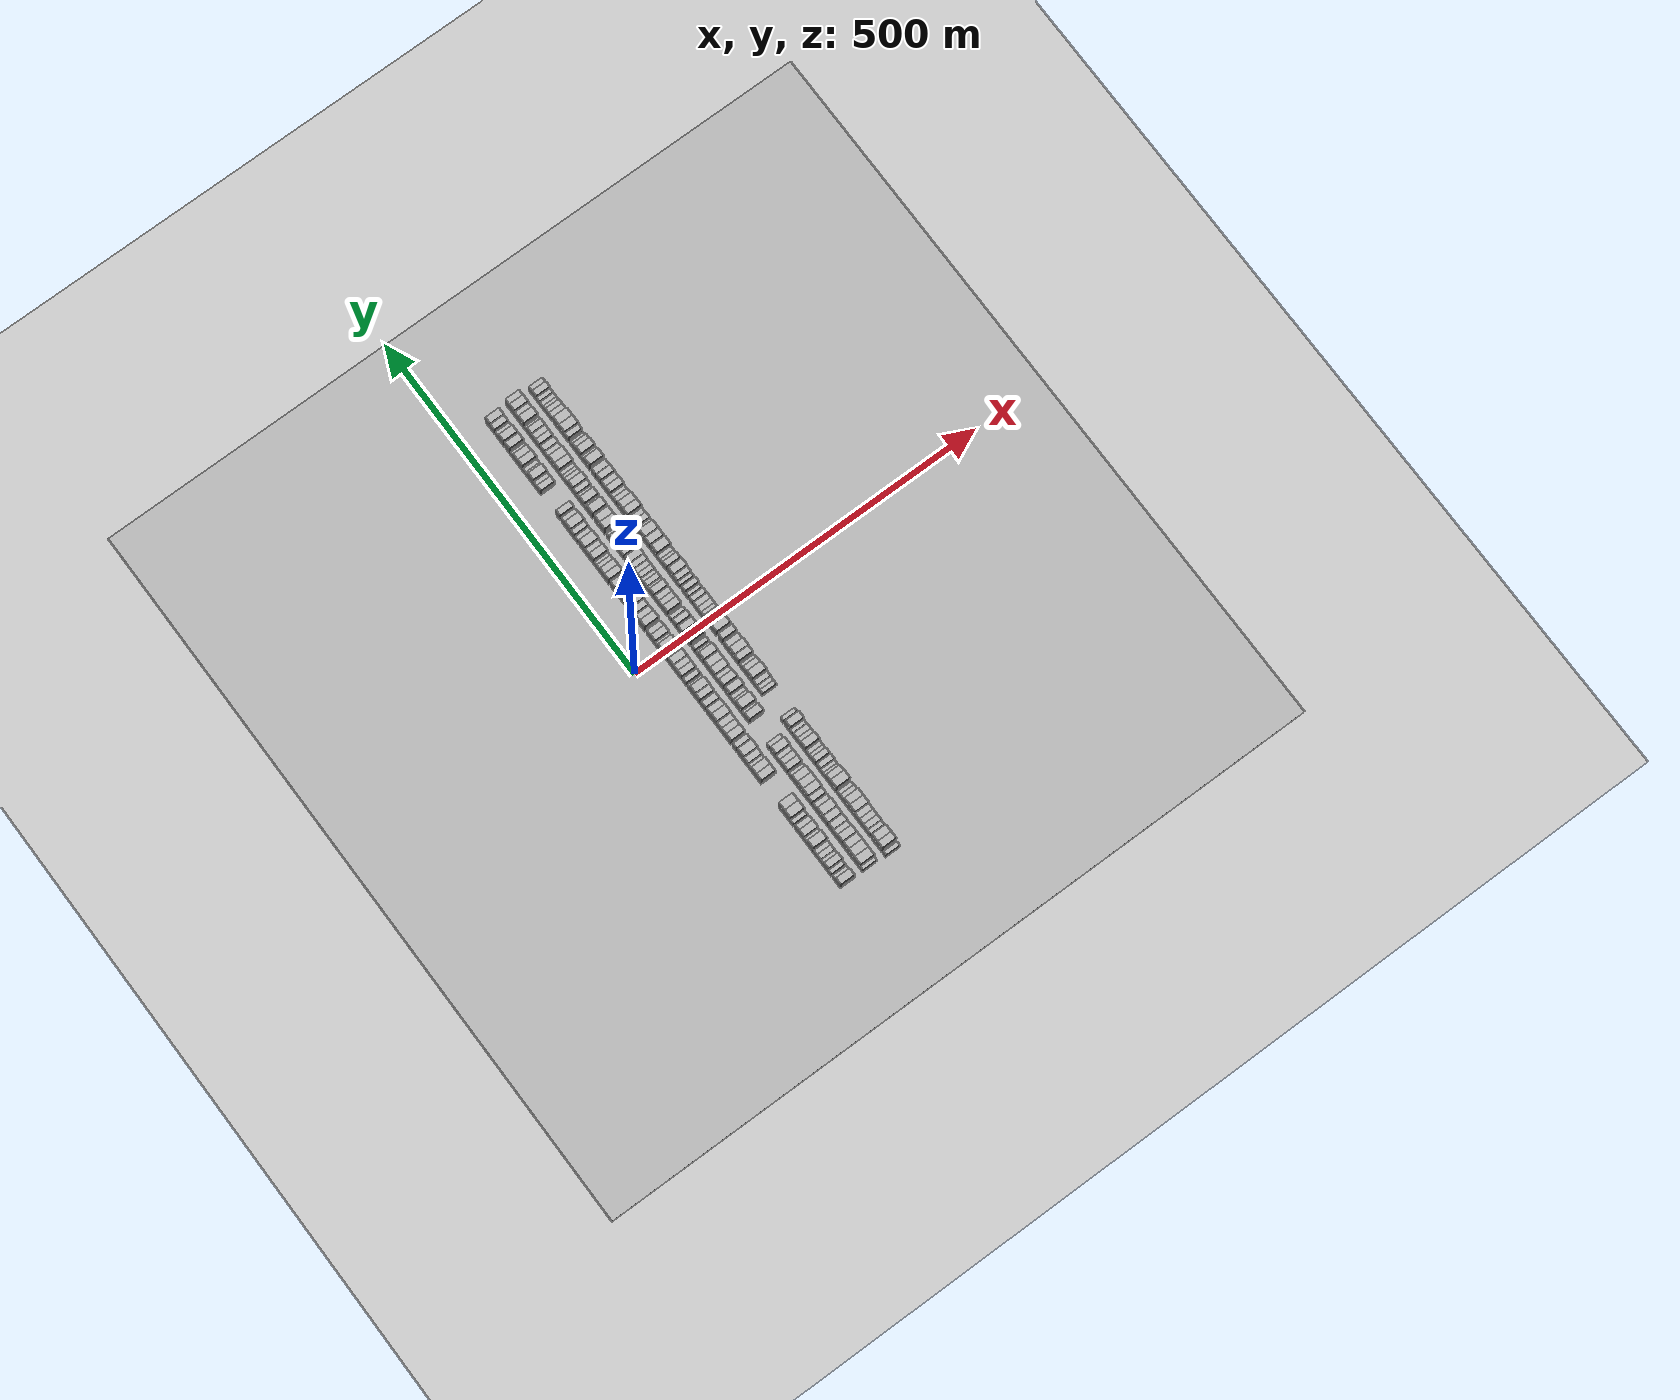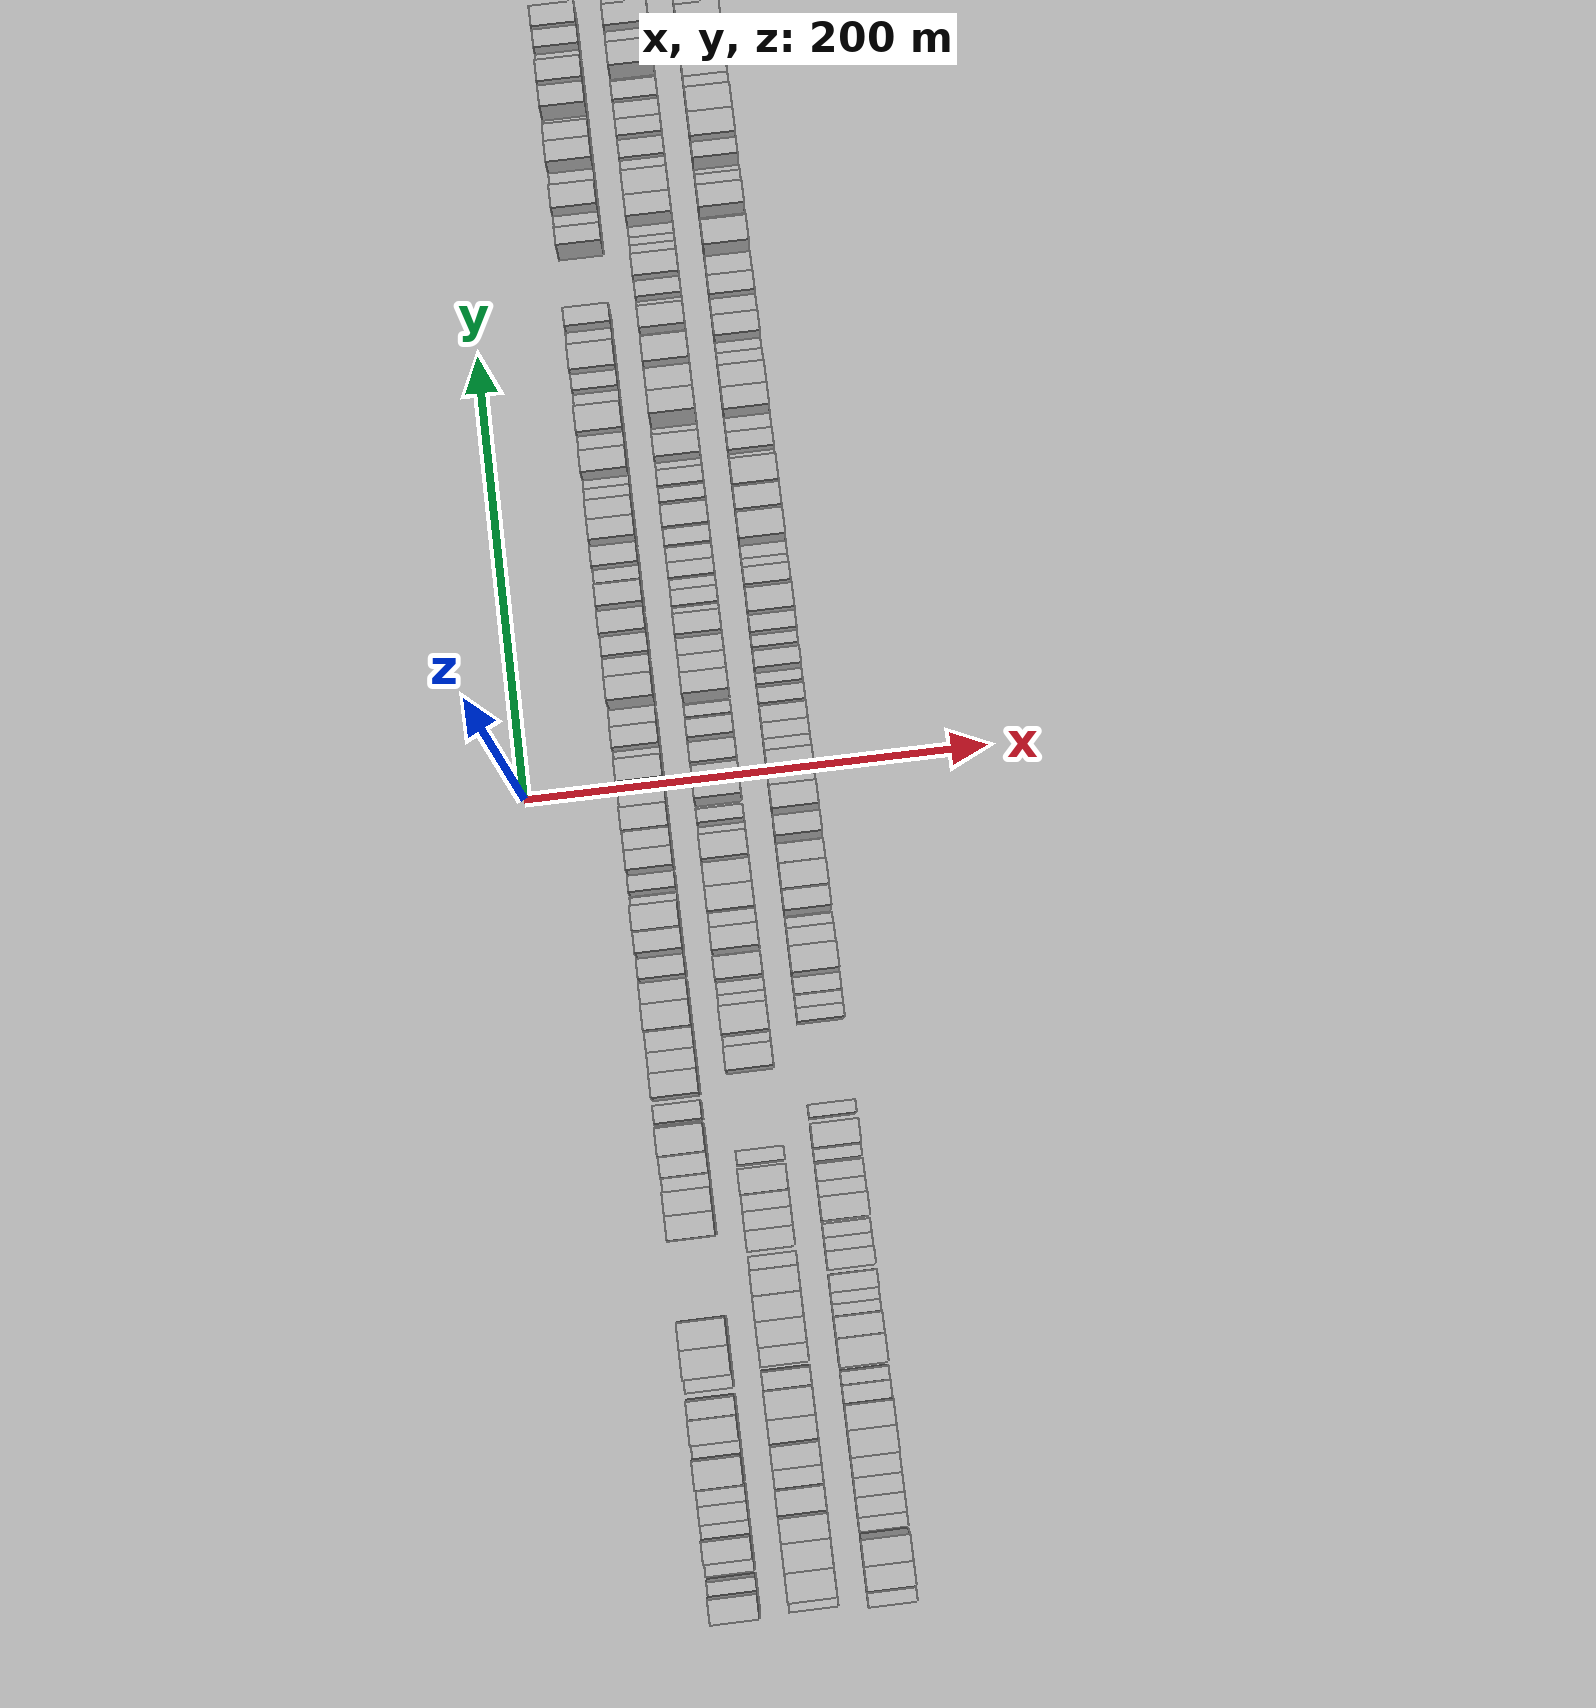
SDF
<?xml version="1.0" encoding="utf-8"?>

<sdf version="1.6">

   <world name="default">

      <gui fullscreen="0">

         <camera name="user_camera">

            <pose>-15 0 4.57585 0 0 0</pose>

            <view_controller>orbit</view_controller>

         </camera>

      </gui>

      <scene>

         <sky>

           <clouds>

             <speed>12</speed>

           </clouds>

         </sky>

         <ambient>0.4 0.4 0.4 1</ambient>

         <background>0.7 0.7 0.7 1</background>

         <shadows>1</shadows>

      </scene>

      <gravity>0 0 -9.8066</gravity>

      <magnetic_field>6e-06 2.3e-05 -4.2e-05</magnetic_field>

      <physics default="0" name="default_physics" type="ode">

         <ode>

            <solver>

               <type>quick</type>

               <iters>10</iters>

               <sor>1.0</sor>

               <use_dynamic_moi_rescaling>0</use_dynamic_moi_rescaling>

            </solver>

            <constraints>

               <cfm>0</cfm>

               <erp>0.2</erp>

               <contact_max_correcting_vel>100</contact_max_correcting_vel>

               <contact_surface_layer>0.001</contact_surface_layer>

            </constraints>

         </ode>

         <max_step_size>0.004</max_step_size>

         <real_time_factor>1</real_time_factor>

         <real_time_update_rate>250</real_time_update_rate>

      </physics>

      <light name="sun" type="directional">

         <cast_shadows>1</cast_shadows>

         <pose>0 0 10 0 0 0</pose>

         <diffuse>0.8 0.8 0.8 1</diffuse>

         <specular>0.2 0.2 0.2 1</specular>

         <attenuation>

            <range>1000</range>

            <constant>0.9</constant>

            <linear>0.01</linear>

            <quadratic>0.001</quadratic>

         </attenuation>

         <direction>-0.5 0.1 -0.9</direction>

      </light>

      <include>

         <name>ground_plane_1</name>

         <uri>model://HANNAS_ground_plane</uri>

         <pose>0 0 0  0 0 0</pose>

      </include>

      <include>

         <name>ground_plane_2</name>

         <uri>model://HANNAS_ground_plane</uri>

         <pose>100 0 0  0 0 0</pose>

      </include>

      <model name="building_1">

         <static>1</static>

         <pose frame="">50.0000 -341.0007 0 0.000000 0.000000 0.000000</pose>

         <link name="link">

            <pose frame="">0 0 10.50 0 0 0</pose>

            <collision name="collision">

               <geometry>

                  <box>

                     <size>20.0000 9.9987 21.0000</size>

                  </box>

               </geometry>

               <max_contacts>10</max_contacts>

               <surface>

                  <contact>

                     <ode/>

                  </contact>

                  <bounce/>

                  <friction>

                     <torsional>

                        <ode/>

                     </torsional>

                     <ode/>

                  </friction>

               </surface>

            </collision>

            <visual name="visual">

               <cast_shadows>0</cast_shadows>

               <geometry>

                  <box>

                     <size>20.0000 9.9987 21.0000</size>

                  </box>

               </geometry>

               <material>

                  <script>

                     <uri>model://HANNAS_wall/materials/scripts</uri>

                     <uri>model://HANNAS_wall/materials/textures</uri>

                     <name>vrc/HANNAS_wall</name>

                  </script>

               </material>

            </visual>

            <self_collide>0</self_collide>

            <enable_wind>0</enable_wind>

            <kinematic>0</kinematic>

         </link>

      </model>

      <model name="building_2">

         <static>1</static>

         <pose frame="">50.0000 -333.1451 0 0.000000 0.000000 0.000000</pose>

         <link name="link">

            <pose frame="">0 0 6.00 0 0 0</pose>

            <collision name="collision">

               <geometry>

                  <box>

                     <size>20.0000 5.7126 12.0000</size>

                  </box>

               </geometry>

               <max_contacts>10</max_contacts>

               <surface>

                  <contact>

                     <ode/>

                  </contact>

                  <bounce/>

                  <friction>

                     <torsional>

                        <ode/>

                     </torsional>

                     <ode/>

                  </friction>

               </surface>

            </collision>

            <visual name="visual">

               <cast_shadows>0</cast_shadows>

               <geometry>

                  <box>

                     <size>20.0000 5.7126 12.0000</size>

                  </box>

               </geometry>

               <material>

                  <script>

                     <uri>model://HANNAS_wall/materials/scripts</uri>

                     <uri>model://HANNAS_wall/materials/textures</uri>

                     <name>vrc/HANNAS_wall</name>

                  </script>

               </material>

            </visual>

            <self_collide>0</self_collide>

            <enable_wind>0</enable_wind>

            <kinematic>0</kinematic>

         </link>

      </model>

      <model name="building_3">

         <static>1</static>

         <pose frame="">50.0000 -325.3495 0 0.000000 0.000000 0.000000</pose>

         <link name="link">

            <pose frame="">0 0 6.00 0 0 0</pose>

            <collision name="collision">

               <geometry>

                  <box>

                     <size>20.0000 5.8786 12.0000</size>

                  </box>

               </geometry>

               <max_contacts>10</max_contacts>

               <surface>

                  <contact>

                     <ode/>

                  </contact>

                  <bounce/>

                  <friction>

                     <torsional>

                        <ode/>

                     </torsional>

                     <ode/>

                  </friction>

               </surface>

            </collision>

            <visual name="visual">

               <cast_shadows>0</cast_shadows>

               <geometry>

                  <box>

                     <size>20.0000 5.8786 12.0000</size>

                  </box>

               </geometry>

               <material>

                  <script>

                     <uri>model://HANNAS_wall/materials/scripts</uri>

                     <uri>model://HANNAS_wall/materials/textures</uri>

                     <name>vrc/HANNAS_wall</name>

                  </script>

               </material>

            </visual>

            <self_collide>0</self_collide>

            <enable_wind>0</enable_wind>

            <kinematic>0</kinematic>

         </link>

      </model>

      <model name="building_4">

         <static>1</static>

         <pose frame="">50.0000 -317.9220 0 0.000000 0.000000 0.000000</pose>

         <link name="link">

            <pose frame="">0 0 10.50 0 0 0</pose>

            <collision name="collision">

               <geometry>

                  <box>

                     <size>20.0000 8.9763 21.0000</size>

                  </box>

               </geometry>

               <max_contacts>10</max_contacts>

               <surface>

                  <contact>

                     <ode/>

                  </contact>

                  <bounce/>

                  <friction>

                     <torsional>

                        <ode/>

                     </torsional>

                     <ode/>

                  </friction>

               </surface>

            </collision>

            <visual name="visual">

               <cast_shadows>0</cast_shadows>

               <geometry>

                  <box>

                     <size>20.0000 8.9763 21.0000</size>

                  </box>

               </geometry>

               <material>

                  <script>

                     <uri>model://HANNAS_wall/materials/scripts</uri>

                     <uri>model://HANNAS_wall/materials/textures</uri>

                     <name>vrc/HANNAS_wall</name>

                  </script>

               </material>

            </visual>

            <self_collide>0</self_collide>

            <enable_wind>0</enable_wind>

            <kinematic>0</kinematic>

         </link>

      </model>

      <model name="building_5">

         <static>1</static>

         <pose frame="">50.0000 -310.5310 0 0.000000 0.000000 0.000000</pose>

         <link name="link">

            <pose frame="">0 0 6.00 0 0 0</pose>

            <collision name="collision">

               <geometry>

                  <box>

                     <size>20.0000 5.8058 12.0000</size>

                  </box>

               </geometry>

               <max_contacts>10</max_contacts>

               <surface>

                  <contact>

                     <ode/>

                  </contact>

                  <bounce/>

                  <friction>

                     <torsional>

                        <ode/>

                     </torsional>

                     <ode/>

                  </friction>

               </surface>

            </collision>

            <visual name="visual">

               <cast_shadows>0</cast_shadows>

               <geometry>

                  <box>

                     <size>20.0000 5.8058 12.0000</size>

                  </box>

               </geometry>

               <material>

                  <script>

                     <uri>model://HANNAS_wall/materials/scripts</uri>

                     <uri>model://HANNAS_wall/materials/textures</uri>

                     <name>vrc/HANNAS_wall</name>

                  </script>

               </material>

            </visual>

            <self_collide>0</self_collide>

            <enable_wind>0</enable_wind>

            <kinematic>0</kinematic>

         </link>

      </model>

      <model name="building_6">

         <static>1</static>

         <pose frame="">50.0000 -303.9072 0 0.000000 0.000000 0.000000</pose>

         <link name="link">

            <pose frame="">0 0 7.50 0 0 0</pose>

            <collision name="collision">

               <geometry>

                  <box>

                     <size>20.0000 7.4418 15.0000</size>

                  </box>

               </geometry>

               <max_contacts>10</max_contacts>

               <surface>

                  <contact>

                     <ode/>

                  </contact>

                  <bounce/>

                  <friction>

                     <torsional>

                        <ode/>

                     </torsional>

                     <ode/>

                  </friction>

               </surface>

            </collision>

            <visual name="visual">

               <cast_shadows>0</cast_shadows>

               <geometry>

                  <box>

                     <size>20.0000 7.4418 15.0000</size>

                  </box>

               </geometry>

               <material>

                  <script>

                     <uri>model://HANNAS_wall/materials/scripts</uri>

                     <uri>model://HANNAS_wall/materials/textures</uri>

                     <name>vrc/HANNAS_wall</name>

                  </script>

               </material>

            </visual>

            <self_collide>0</self_collide>

            <enable_wind>0</enable_wind>

            <kinematic>0</kinematic>

         </link>

      </model>

      <model name="building_7">

         <static>1</static>

         <pose frame="">50.0000 -297.1003 0 0.000000 0.000000 0.000000</pose>

         <link name="link">

            <pose frame="">0 0 7.50 0 0 0</pose>

            <collision name="collision">

               <geometry>

                  <box>

                     <size>20.0000 6.1720 15.0000</size>

                  </box>

               </geometry>

               <max_contacts>10</max_contacts>

               <surface>

                  <contact>

                     <ode/>

                  </contact>

                  <bounce/>

                  <friction>

                     <torsional>

                        <ode/>

                     </torsional>

                     <ode/>

                  </friction>

               </surface>

            </collision>

            <visual name="visual">

               <cast_shadows>0</cast_shadows>

               <geometry>

                  <box>

                     <size>20.0000 6.1720 15.0000</size>

                  </box>

               </geometry>

               <material>

                  <script>

                     <uri>model://HANNAS_wall/materials/scripts</uri>

                     <uri>model://HANNAS_wall/materials/textures</uri>

                     <name>vrc/HANNAS_wall</name>

                  </script>

               </material>

            </visual>

            <self_collide>0</self_collide>

            <enable_wind>0</enable_wind>

            <kinematic>0</kinematic>

         </link>

      </model>

      <model name="building_8">

         <static>1</static>

         <pose frame="">50.0000 -287.2053 0 0.000000 0.000000 0.000000</pose>

         <link name="link">

            <pose frame="">0 0 12.00 0 0 0</pose>

            <collision name="collision">

               <geometry>

                  <box>

                     <size>20.0000 11.6180 24.0000</size>

                  </box>

               </geometry>

               <max_contacts>10</max_contacts>

               <surface>

                  <contact>

                     <ode/>

                  </contact>

                  <bounce/>

                  <friction>

                     <torsional>

                        <ode/>

                     </torsional>

                     <ode/>

                  </friction>

               </surface>

            </collision>

            <visual name="visual">

               <cast_shadows>0</cast_shadows>

               <geometry>

                  <box>

                     <size>20.0000 11.6180 24.0000</size>

                  </box>

               </geometry>

               <material>

                  <script>

                     <uri>model://HANNAS_wall/materials/scripts</uri>

                     <uri>model://HANNAS_wall/materials/textures</uri>

                     <name>vrc/HANNAS_wall</name>

                  </script>

               </material>

            </visual>

            <self_collide>0</self_collide>

            <enable_wind>0</enable_wind>

            <kinematic>0</kinematic>

         </link>

      </model>

      <model name="building_9">

         <static>1</static>

         <pose frame="">50.0000 -278.5174 0 0.000000 0.000000 0.000000</pose>

         <link name="link">

            <pose frame="">0 0 6.00 0 0 0</pose>

            <collision name="collision">

               <geometry>

                  <box>

                     <size>20.0000 5.7579 12.0000</size>

                  </box>

               </geometry>

               <max_contacts>10</max_contacts>

               <surface>

                  <contact>

                     <ode/>

                  </contact>

                  <bounce/>

                  <friction>

                     <torsional>

                        <ode/>

                     </torsional>

                     <ode/>

                  </friction>

               </surface>

            </collision>

            <visual name="visual">

               <cast_shadows>0</cast_shadows>

               <geometry>

                  <box>

                     <size>20.0000 5.7579 12.0000</size>

                  </box>

               </geometry>

               <material>

                  <script>

                     <uri>model://HANNAS_wall/materials/scripts</uri>

                     <uri>model://HANNAS_wall/materials/textures</uri>

                     <name>vrc/HANNAS_wall</name>

                  </script>

               </material>

            </visual>

            <self_collide>0</self_collide>

            <enable_wind>0</enable_wind>

            <kinematic>0</kinematic>

         </link>

      </model>

      <model name="building_10">

         <static>1</static>

         <pose frame="">50.0000 -270.5903 0 0.000000 0.000000 0.000000</pose>

         <link name="link">

            <pose frame="">0 0 10.50 0 0 0</pose>

            <collision name="collision">

               <geometry>

                  <box>

                     <size>20.0000 10.0962 21.0000</size>

                  </box>

               </geometry>

               <max_contacts>10</max_contacts>

               <surface>

                  <contact>

                     <ode/>

                  </contact>

                  <bounce/>

                  <friction>

                     <torsional>

                        <ode/>

                     </torsional>

                     <ode/>

                  </friction>

               </surface>

            </collision>

            <visual name="visual">

               <cast_shadows>0</cast_shadows>

               <geometry>

                  <box>

                     <size>20.0000 10.0962 21.0000</size>

                  </box>

               </geometry>

               <material>

                  <script>

                     <uri>model://HANNAS_wall/materials/scripts</uri>

                     <uri>model://HANNAS_wall/materials/textures</uri>

                     <name>vrc/HANNAS_wall</name>

                  </script>

               </material>

            </visual>

            <self_collide>0</self_collide>

            <enable_wind>0</enable_wind>

            <kinematic>0</kinematic>

         </link>

      </model>

      <model name="building_11">

         <static>1</static>

         <pose frame="">50.0000 -261.7958 0 0.000000 0.000000 0.000000</pose>

         <link name="link">

            <pose frame="">0 0 9.00 0 0 0</pose>

            <collision name="collision">

               <geometry>

                  <box>

                     <size>20.0000 7.4928 18.0000</size>

                  </box>

               </geometry>

               <max_contacts>10</max_contacts>

               <surface>

                  <contact>

                     <ode/>

                  </contact>

                  <bounce/>

                  <friction>

                     <torsional>

                        <ode/>

                     </torsional>

                     <ode/>

                  </friction>

               </surface>

            </collision>

            <visual name="visual">

               <cast_shadows>0</cast_shadows>

               <geometry>

                  <box>

                     <size>20.0000 7.4928 18.0000</size>

                  </box>

               </geometry>

               <material>

                  <script>

                     <uri>model://HANNAS_wall/materials/scripts</uri>

                     <uri>model://HANNAS_wall/materials/textures</uri>

                     <name>vrc/HANNAS_wall</name>

                  </script>

               </material>

            </visual>

            <self_collide>0</self_collide>

            <enable_wind>0</enable_wind>

            <kinematic>0</kinematic>

         </link>

      </model>

      <model name="building_12">

         <static>1</static>

         <pose frame="">50.0000 -252.1209 0 0.000000 0.000000 0.000000</pose>

         <link name="link">

            <pose frame="">0 0 6.00 0 0 0</pose>

            <collision name="collision">

               <geometry>

                  <box>

                     <size>20.0000 5.8571 12.0000</size>

                  </box>

               </geometry>

               <max_contacts>10</max_contacts>

               <surface>

                  <contact>

                     <ode/>

                  </contact>

                  <bounce/>

                  <friction>

                     <torsional>

                        <ode/>

                     </torsional>

                     <ode/>

                  </friction>

               </surface>

            </collision>

            <visual name="visual">

               <cast_shadows>0</cast_shadows>

               <geometry>

                  <box>

                     <size>20.0000 5.8571 12.0000</size>

                  </box>

               </geometry>

               <material>

                  <script>

                     <uri>model://HANNAS_wall/materials/scripts</uri>

                     <uri>model://HANNAS_wall/materials/textures</uri>

                     <name>vrc/HANNAS_wall</name>

                  </script>

               </material>

            </visual>

            <self_collide>0</self_collide>

            <enable_wind>0</enable_wind>

            <kinematic>0</kinematic>

         </link>

      </model>

      <model name="building_13">

         <static>1</static>

         <pose frame="">50.0000 -243.2870 0 0.000000 0.000000 0.000000</pose>

         <link name="link">

            <pose frame="">0 0 12.00 0 0 0</pose>

            <collision name="collision">

               <geometry>

                  <box>

                     <size>20.0000 11.8106 24.0000</size>

                  </box>

               </geometry>

               <max_contacts>10</max_contacts>

               <surface>

                  <contact>

                     <ode/>

                  </contact>

                  <bounce/>

                  <friction>

                     <torsional>

                        <ode/>

                     </torsional>

                     <ode/>

                  </friction>

               </surface>

            </collision>

            <visual name="visual">

               <cast_shadows>0</cast_shadows>

               <geometry>

                  <box>

                     <size>20.0000 11.8106 24.0000</size>

                  </box>

               </geometry>

               <material>

                  <script>

                     <uri>model://HANNAS_wall/materials/scripts</uri>

                     <uri>model://HANNAS_wall/materials/textures</uri>

                     <name>vrc/HANNAS_wall</name>

                  </script>

               </material>

            </visual>

            <self_collide>0</self_collide>

            <enable_wind>0</enable_wind>

            <kinematic>0</kinematic>

         </link>

      </model>

      <model name="building_14">

         <static>1</static>

         <pose frame="">50.0000 -231.7851 0 0.000000 0.000000 0.000000</pose>

         <link name="link">

            <pose frame="">0 0 12.00 0 0 0</pose>

            <collision name="collision">

               <geometry>

                  <box>

                     <size>20.0000 11.1931 24.0000</size>

                  </box>

               </geometry>

               <max_contacts>10</max_contacts>

               <surface>

                  <contact>

                     <ode/>

                  </contact>

                  <bounce/>

                  <friction>

                     <torsional>

                        <ode/>

                     </torsional>

                     <ode/>

                  </friction>

               </surface>

            </collision>

            <visual name="visual">

               <cast_shadows>0</cast_shadows>

               <geometry>

                  <box>

                     <size>20.0000 11.1931 24.0000</size>

                  </box>

               </geometry>

               <material>

                  <script>

                     <uri>model://HANNAS_wall/materials/scripts</uri>

                     <uri>model://HANNAS_wall/materials/textures</uri>

                     <name>vrc/HANNAS_wall</name>

                  </script>

               </material>

            </visual>

            <self_collide>0</self_collide>

            <enable_wind>0</enable_wind>

            <kinematic>0</kinematic>

         </link>

      </model>

      <model name="building_15">

         <static>1</static>

         <pose frame="">50.0000 -188.0272 0 0.000000 0.000000 0.000000</pose>

         <link name="link">

            <pose frame="">0 0 10.50 0 0 0</pose>

            <collision name="collision">

               <geometry>

                  <box>

                     <size>20.0000 10.1076 21.0000</size>

                  </box>

               </geometry>

               <max_contacts>10</max_contacts>

               <surface>

                  <contact>

                     <ode/>

                  </contact>

                  <bounce/>

                  <friction>

                     <torsional>

                        <ode/>

                     </torsional>

                     <ode/>

                  </friction>

               </surface>

            </collision>

            <visual name="visual">

               <cast_shadows>0</cast_shadows>

               <geometry>

                  <box>

                     <size>20.0000 10.1076 21.0000</size>

                  </box>

               </geometry>

               <material>

                  <script>

                     <uri>model://HANNAS_wall/materials/scripts</uri>

                     <uri>model://HANNAS_wall/materials/textures</uri>

                     <name>vrc/HANNAS_wall</name>

                  </script>

               </material>

            </visual>

            <self_collide>0</self_collide>

            <enable_wind>0</enable_wind>

            <kinematic>0</kinematic>

         </link>

      </model>

      <model name="building_16">

         <static>1</static>

         <pose frame="">50.0000 -178.0848 0 0.000000 0.000000 0.000000</pose>

         <link name="link">

            <pose frame="">0 0 10.50 0 0 0</pose>

            <collision name="collision">

               <geometry>

                  <box>

                     <size>20.0000 9.7773 21.0000</size>

                  </box>

               </geometry>

               <max_contacts>10</max_contacts>

               <surface>

                  <contact>

                     <ode/>

                  </contact>

                  <bounce/>

                  <friction>

                     <torsional>

                        <ode/>

                     </torsional>

                     <ode/>

                  </friction>

               </surface>

            </collision>

            <visual name="visual">

               <cast_shadows>0</cast_shadows>

               <geometry>

                  <box>

                     <size>20.0000 9.7773 21.0000</size>

                  </box>

               </geometry>

               <material>

                  <script>

                     <uri>model://HANNAS_wall/materials/scripts</uri>

                     <uri>model://HANNAS_wall/materials/textures</uri>

                     <name>vrc/HANNAS_wall</name>

                  </script>

               </material>

            </visual>

            <self_collide>0</self_collide>

            <enable_wind>0</enable_wind>

            <kinematic>0</kinematic>

         </link>

      </model>

      <model name="building_17">

         <static>1</static>

         <pose frame="">50.0000 -170.2554 0 0.000000 0.000000 0.000000</pose>

         <link name="link">

            <pose frame="">0 0 6.00 0 0 0</pose>

            <collision name="collision">

               <geometry>

                  <box>

                     <size>20.0000 5.8816 12.0000</size>

                  </box>

               </geometry>

               <max_contacts>10</max_contacts>

               <surface>

                  <contact>

                     <ode/>

                  </contact>

                  <bounce/>

                  <friction>

                     <torsional>

                        <ode/>

                     </torsional>

                     <ode/>

                  </friction>

               </surface>

            </collision>

            <visual name="visual">

               <cast_shadows>0</cast_shadows>

               <geometry>

                  <box>

                     <size>20.0000 5.8816 12.0000</size>

                  </box>

               </geometry>

               <material>

                  <script>

                     <uri>model://HANNAS_wall/materials/scripts</uri>

                     <uri>model://HANNAS_wall/materials/textures</uri>

                     <name>vrc/HANNAS_wall</name>

                  </script>

               </material>

            </visual>

            <self_collide>0</self_collide>

            <enable_wind>0</enable_wind>

            <kinematic>0</kinematic>

         </link>

      </model>

      <model name="building_18">

         <static>1</static>

         <pose frame="">50.0000 -163.0106 0 0.000000 0.000000 0.000000</pose>

         <link name="link">

            <pose frame="">0 0 9.00 0 0 0</pose>

            <collision name="collision">

               <geometry>

                  <box>

                     <size>20.0000 8.6079 18.0000</size>

                  </box>

               </geometry>

               <max_contacts>10</max_contacts>

               <surface>

                  <contact>

                     <ode/>

                  </contact>

                  <bounce/>

                  <friction>

                     <torsional>

                        <ode/>

                     </torsional>

                     <ode/>

                  </friction>

               </surface>

            </collision>

            <visual name="visual">

               <cast_shadows>0</cast_shadows>

               <geometry>

                  <box>

                     <size>20.0000 8.6079 18.0000</size>

                  </box>

               </geometry>

               <material>

                  <script>

                     <uri>model://HANNAS_wall/materials/scripts</uri>

                     <uri>model://HANNAS_wall/materials/textures</uri>

                     <name>vrc/HANNAS_wall</name>

                  </script>

               </material>

            </visual>

            <self_collide>0</self_collide>

            <enable_wind>0</enable_wind>

            <kinematic>0</kinematic>

         </link>

      </model>

      <model name="building_19">

         <static>1</static>

         <pose frame="">50.0000 -152.7839 0 0.000000 0.000000 0.000000</pose>

         <link name="link">

            <pose frame="">0 0 12.00 0 0 0</pose>

            <collision name="collision">

               <geometry>

                  <box>

                     <size>20.0000 11.8455 24.0000</size>

                  </box>

               </geometry>

               <max_contacts>10</max_contacts>

               <surface>

                  <contact>

                     <ode/>

                  </contact>

                  <bounce/>

                  <friction>

                     <torsional>

                        <ode/>

                     </torsional>

                     <ode/>

                  </friction>

               </surface>

            </collision>

            <visual name="visual">

               <cast_shadows>0</cast_shadows>

               <geometry>

                  <box>

                     <size>20.0000 11.8455 24.0000</size>

                  </box>

               </geometry>

               <material>

                  <script>

                     <uri>model://HANNAS_wall/materials/scripts</uri>

                     <uri>model://HANNAS_wall/materials/textures</uri>

                     <name>vrc/HANNAS_wall</name>

                  </script>

               </material>

            </visual>

            <self_collide>0</self_collide>

            <enable_wind>0</enable_wind>

            <kinematic>0</kinematic>

         </link>

      </model>

      <model name="building_20">

         <static>1</static>

         <pose frame="">50.0000 -141.0878 0 0.000000 0.000000 0.000000</pose>

         <link name="link">

            <pose frame="">0 0 9.00 0 0 0</pose>

            <collision name="collision">

               <geometry>

                  <box>

                     <size>20.0000 7.5467 18.0000</size>

                  </box>

               </geometry>

               <max_contacts>10</max_contacts>

               <surface>

                  <contact>

                     <ode/>

                  </contact>

                  <bounce/>

                  <friction>

                     <torsional>

                        <ode/>

                     </torsional>

                     <ode/>

                  </friction>

               </surface>

            </collision>

            <visual name="visual">

               <cast_shadows>0</cast_shadows>

               <geometry>

                  <box>

                     <size>20.0000 7.5467 18.0000</size>

                  </box>

               </geometry>

               <material>

                  <script>

                     <uri>model://HANNAS_wall/materials/scripts</uri>

                     <uri>model://HANNAS_wall/materials/textures</uri>

                     <name>vrc/HANNAS_wall</name>

                  </script>

               </material>

            </visual>

            <self_collide>0</self_collide>

            <enable_wind>0</enable_wind>

            <kinematic>0</kinematic>

         </link>

      </model>

      <model name="building_21">

         <static>1</static>

         <pose frame="">50.0000 -129.2175 0 0.000000 0.000000 0.000000</pose>

         <link name="link">

            <pose frame="">0 0 10.50 0 0 0</pose>

            <collision name="collision">

               <geometry>

                  <box>

                     <size>20.0000 10.1940 21.0000</size>

                  </box>

               </geometry>

               <max_contacts>10</max_contacts>

               <surface>

                  <contact>

                     <ode/>

                  </contact>

                  <bounce/>

                  <friction>

                     <torsional>

                        <ode/>

                     </torsional>

                     <ode/>

                  </friction>

               </surface>

            </collision>

            <visual name="visual">

               <cast_shadows>0</cast_shadows>

               <geometry>

                  <box>

                     <size>20.0000 10.1940 21.0000</size>

                  </box>

               </geometry>

               <material>

                  <script>

                     <uri>model://HANNAS_wall/materials/scripts</uri>

                     <uri>model://HANNAS_wall/materials/textures</uri>

                     <name>vrc/HANNAS_wall</name>

                  </script>

               </material>

            </visual>

            <self_collide>0</self_collide>

            <enable_wind>0</enable_wind>

            <kinematic>0</kinematic>

         </link>

      </model>

      <model name="building_22">

         <static>1</static>

         <pose frame="">50.0000 -119.6729 0 0.000000 0.000000 0.000000</pose>

         <link name="link">

            <pose frame="">0 0 9.00 0 0 0</pose>

            <collision name="collision">

               <geometry>

                  <box>

                     <size>20.0000 8.8952 18.0000</size>

                  </box>

               </geometry>

               <max_contacts>10</max_contacts>

               <surface>

                  <contact>

                     <ode/>

                  </contact>

                  <bounce/>

                  <friction>

                     <torsional>

                        <ode/>

                     </torsional>

                     <ode/>

                  </friction>

               </surface>

            </collision>

            <visual name="visual">

               <cast_shadows>0</cast_shadows>

               <geometry>

                  <box>

                     <size>20.0000 8.8952 18.0000</size>

                  </box>

               </geometry>

               <material>

                  <script>

                     <uri>model://HANNAS_wall/materials/scripts</uri>

                     <uri>model://HANNAS_wall/materials/textures</uri>

                     <name>vrc/HANNAS_wall</name>

                  </script>

               </material>

            </visual>

            <self_collide>0</self_collide>

            <enable_wind>0</enable_wind>

            <kinematic>0</kinematic>

         </link>

      </model>

      <model name="building_23">

         <static>1</static>

         <pose frame="">50.0000 -110.8884 0 0.000000 0.000000 0.000000</pose>

         <link name="link">

            <pose frame="">0 0 9.00 0 0 0</pose>

            <collision name="collision">

               <geometry>

                  <box>

                     <size>20.0000 8.6737 18.0000</size>

                  </box>

               </geometry>

               <max_contacts>10</max_contacts>

               <surface>

                  <contact>

                     <ode/>

                  </contact>

                  <bounce/>

                  <friction>

                     <torsional>

                        <ode/>

                     </torsional>

                     <ode/>

                  </friction>

               </surface>

            </collision>

            <visual name="visual">

               <cast_shadows>0</cast_shadows>

               <geometry>

                  <box>

                     <size>20.0000 8.6737 18.0000</size>

                  </box>

               </geometry>

               <material>

                  <script>

                     <uri>model://HANNAS_wall/materials/scripts</uri>

                     <uri>model://HANNAS_wall/materials/textures</uri>

                     <name>vrc/HANNAS_wall</name>

                  </script>

               </material>

            </visual>

            <self_collide>0</self_collide>

            <enable_wind>0</enable_wind>

            <kinematic>0</kinematic>

         </link>

      </model>

      <model name="building_24">

         <static>1</static>

         <pose frame="">50.0000 -101.0242 0 0.000000 0.000000 0.000000</pose>

         <link name="link">

            <pose frame="">0 0 12.00 0 0 0</pose>

            <collision name="collision">

               <geometry>

                  <box>

                     <size>20.0000 11.0546 24.0000</size>

                  </box>

               </geometry>

               <max_contacts>10</max_contacts>

               <surface>

                  <contact>

                     <ode/>

                  </contact>

                  <bounce/>

                  <friction>

                     <torsional>

                        <ode/>

                     </torsional>

                     <ode/>

                  </friction>

               </surface>

            </collision>

            <visual name="visual">

               <cast_shadows>0</cast_shadows>

               <geometry>

                  <box>

                     <size>20.0000 11.0546 24.0000</size>

                  </box>

               </geometry>

               <material>

                  <script>

                     <uri>model://HANNAS_wall/materials/scripts</uri>

                     <uri>model://HANNAS_wall/materials/textures</uri>

                     <name>vrc/HANNAS_wall</name>

                  </script>

               </material>

            </visual>

            <self_collide>0</self_collide>

            <enable_wind>0</enable_wind>

            <kinematic>0</kinematic>

         </link>

      </model>

      <model name="building_25">

         <static>1</static>

         <pose frame="">50.0000 -90.9319 0 0.000000 0.000000 0.000000</pose>

         <link name="link">

            <pose frame="">0 0 10.50 0 0 0</pose>

            <collision name="collision">

               <geometry>

                  <box>

                     <size>20.0000 9.1301 21.0000</size>

                  </box>

               </geometry>

               <max_contacts>10</max_contacts>

               <surface>

                  <contact>

                     <ode/>

                  </contact>

                  <bounce/>

                  <friction>

                     <torsional>

                        <ode/>

                     </torsional>

                     <ode/>

                  </friction>

               </surface>

            </collision>

            <visual name="visual">

               <cast_shadows>0</cast_shadows>

               <geometry>

                  <box>

                     <size>20.0000 9.1301 21.0000</size>

                  </box>

               </geometry>

               <material>

                  <script>

                     <uri>model://HANNAS_wall/materials/scripts</uri>

                     <uri>model://HANNAS_wall/materials/textures</uri>

                     <name>vrc/HANNAS_wall</name>

                  </script>

               </material>

            </visual>

            <self_collide>0</self_collide>

            <enable_wind>0</enable_wind>

            <kinematic>0</kinematic>

         </link>

      </model>

      <model name="building_26">

         <static>1</static>

         <pose frame="">50.0000 -80.0476 0 0.000000 0.000000 0.000000</pose>

         <link name="link">

            <pose frame="">0 0 9.00 0 0 0</pose>

            <collision name="collision">

               <geometry>

                  <box>

                     <size>20.0000 8.6386 18.0000</size>

                  </box>

               </geometry>

               <max_contacts>10</max_contacts>

               <surface>

                  <contact>

                     <ode/>

                  </contact>

                  <bounce/>

                  <friction>

                     <torsional>

                        <ode/>

                     </torsional>

                     <ode/>

                  </friction>

               </surface>

            </collision>

            <visual name="visual">

               <cast_shadows>0</cast_shadows>

               <geometry>

                  <box>

                     <size>20.0000 8.6386 18.0000</size>

                  </box>

               </geometry>

               <material>

                  <script>

                     <uri>model://HANNAS_wall/materials/scripts</uri>

                     <uri>model://HANNAS_wall/materials/textures</uri>

                     <name>vrc/HANNAS_wall</name>

                  </script>

               </material>

            </visual>

            <self_collide>0</self_collide>

            <enable_wind>0</enable_wind>

            <kinematic>0</kinematic>

         </link>

      </model>

      <model name="building_27">

         <static>1</static>

         <pose frame="">50.0000 -69.2819 0 0.000000 0.000000 0.000000</pose>

         <link name="link">

            <pose frame="">0 0 10.50 0 0 0</pose>

            <collision name="collision">

               <geometry>

                  <box>

                     <size>20.0000 8.8927 21.0000</size>

                  </box>

               </geometry>

               <max_contacts>10</max_contacts>

               <surface>

                  <contact>

                     <ode/>

                  </contact>

                  <bounce/>

                  <friction>

                     <torsional>

                        <ode/>

                     </torsional>

                     <ode/>

                  </friction>

               </surface>

            </collision>

            <visual name="visual">

               <cast_shadows>0</cast_shadows>

               <geometry>

                  <box>

                     <size>20.0000 8.8927 21.0000</size>

                  </box>

               </geometry>

               <material>

                  <script>

                     <uri>model://HANNAS_wall/materials/scripts</uri>

                     <uri>model://HANNAS_wall/materials/textures</uri>

                     <name>vrc/HANNAS_wall</name>

                  </script>

               </material>

            </visual>

            <self_collide>0</self_collide>

            <enable_wind>0</enable_wind>

            <kinematic>0</kinematic>

         </link>

      </model>

      <model name="building_28">

         <static>1</static>

         <pose frame="">50.0000 -59.4083 0 0.000000 0.000000 0.000000</pose>

         <link name="link">

            <pose frame="">0 0 12.00 0 0 0</pose>

            <collision name="collision">

               <geometry>

                  <box>

                     <size>20.0000 10.8546 24.0000</size>

                  </box>

               </geometry>

               <max_contacts>10</max_contacts>

               <surface>

                  <contact>

                     <ode/>

                  </contact>

                  <bounce/>

                  <friction>

                     <torsional>

                        <ode/>

                     </torsional>

                     <ode/>

                  </friction>

               </surface>

            </collision>

            <visual name="visual">

               <cast_shadows>0</cast_shadows>

               <geometry>

                  <box>

                     <size>20.0000 10.8546 24.0000</size>

                  </box>

               </geometry>

               <material>

                  <script>

                     <uri>model://HANNAS_wall/materials/scripts</uri>

                     <uri>model://HANNAS_wall/materials/textures</uri>

                     <name>vrc/HANNAS_wall</name>

                  </script>

               </material>

            </visual>

            <self_collide>0</self_collide>

            <enable_wind>0</enable_wind>

            <kinematic>0</kinematic>

         </link>

      </model>

      <model name="building_29">

         <static>1</static>

         <pose frame="">50.0000 -51.4689 0 0.000000 0.000000 0.000000</pose>

         <link name="link">

            <pose frame="">0 0 6.00 0 0 0</pose>

            <collision name="collision">

               <geometry>

                  <box>

                     <size>20.0000 5.0243 12.0000</size>

                  </box>

               </geometry>

               <max_contacts>10</max_contacts>

               <surface>

                  <contact>

                     <ode/>

                  </contact>

                  <bounce/>

                  <friction>

                     <torsional>

                        <ode/>

                     </torsional>

                     <ode/>

                  </friction>

               </surface>

            </collision>

            <visual name="visual">

               <cast_shadows>0</cast_shadows>

               <geometry>

                  <box>

                     <size>20.0000 5.0243 12.0000</size>

                  </box>

               </geometry>

               <material>

                  <script>

                     <uri>model://HANNAS_wall/materials/scripts</uri>

                     <uri>model://HANNAS_wall/materials/textures</uri>

                     <name>vrc/HANNAS_wall</name>

                  </script>

               </material>

            </visual>

            <self_collide>0</self_collide>

            <enable_wind>0</enable_wind>

            <kinematic>0</kinematic>

         </link>

      </model>

      <model name="building_30">

         <static>1</static>

         <pose frame="">50.0000 -43.4374 0 0.000000 0.000000 0.000000</pose>

         <link name="link">

            <pose frame="">0 0 7.50 0 0 0</pose>

            <collision name="collision">

               <geometry>

                  <box>

                     <size>20.0000 7.0387 15.0000</size>

                  </box>

               </geometry>

               <max_contacts>10</max_contacts>

               <surface>

                  <contact>

                     <ode/>

                  </contact>

                  <bounce/>

                  <friction>

                     <torsional>

                        <ode/>

                     </torsional>

                     <ode/>

                  </friction>

               </surface>

            </collision>

            <visual name="visual">

               <cast_shadows>0</cast_shadows>

               <geometry>

                  <box>

                     <size>20.0000 7.0387 15.0000</size>

                  </box>

               </geometry>

               <material>

                  <script>

                     <uri>model://HANNAS_wall/materials/scripts</uri>

                     <uri>model://HANNAS_wall/materials/textures</uri>

                     <name>vrc/HANNAS_wall</name>

                  </script>

               </material>

            </visual>

            <self_collide>0</self_collide>

            <enable_wind>0</enable_wind>

            <kinematic>0</kinematic>

         </link>

      </model>

      <model name="building_31">

         <static>1</static>

         <pose frame="">50.0000 -33.7445 0 0.000000 0.000000 0.000000</pose>

         <link name="link">

            <pose frame="">0 0 9.00 0 0 0</pose>

            <collision name="collision">

               <geometry>

                  <box>

                     <size>20.0000 8.3470 18.0000</size>

                  </box>

               </geometry>

               <max_contacts>10</max_contacts>

               <surface>

                  <contact>

                     <ode/>

                  </contact>

                  <bounce/>

                  <friction>

                     <torsional>

                        <ode/>

                     </torsional>

                     <ode/>

                  </friction>

               </surface>

            </collision>

            <visual name="visual">

               <cast_shadows>0</cast_shadows>

               <geometry>

                  <box>

                     <size>20.0000 8.3470 18.0000</size>

                  </box>

               </geometry>

               <material>

                  <script>

                     <uri>model://HANNAS_wall/materials/scripts</uri>

                     <uri>model://HANNAS_wall/materials/textures</uri>

                     <name>vrc/HANNAS_wall</name>

                  </script>

               </material>

            </visual>

            <self_collide>0</self_collide>

            <enable_wind>0</enable_wind>

            <kinematic>0</kinematic>

         </link>

      </model>

      <model name="building_32">

         <static>1</static>

         <pose frame="">50.0000 -25.5704 0 0.000000 0.000000 0.000000</pose>

         <link name="link">

            <pose frame="">0 0 9.00 0 0 0</pose>

            <collision name="collision">

               <geometry>

                  <box>

                     <size>20.0000 8.0010 18.0000</size>

                  </box>

               </geometry>

               <max_contacts>10</max_contacts>

               <surface>

                  <contact>

                     <ode/>

                  </contact>

                  <bounce/>

                  <friction>

                     <torsional>

                        <ode/>

                     </torsional>

                     <ode/>

                  </friction>

               </surface>

            </collision>

            <visual name="visual">

               <cast_shadows>0</cast_shadows>

               <geometry>

                  <box>

                     <size>20.0000 8.0010 18.0000</size>

                  </box>

               </geometry>

               <material>

                  <script>

                     <uri>model://HANNAS_wall/materials/scripts</uri>

                     <uri>model://HANNAS_wall/materials/textures</uri>

                     <name>vrc/HANNAS_wall</name>

                  </script>

               </material>

            </visual>

            <self_collide>0</self_collide>

            <enable_wind>0</enable_wind>

            <kinematic>0</kinematic>

         </link>

      </model>

      <model name="building_33">

         <static>1</static>

         <pose frame="">50.0000 -16.5483 0 0.000000 0.000000 0.000000</pose>

         <link name="link">

            <pose frame="">0 0 10.50 0 0 0</pose>

            <collision name="collision">

               <geometry>

                  <box>

                     <size>20.0000 10.0432 21.0000</size>

                  </box>

               </geometry>

               <max_contacts>10</max_contacts>

               <surface>

                  <contact>

                     <ode/>

                  </contact>

                  <bounce/>

                  <friction>

                     <torsional>

                        <ode/>

                     </torsional>

                     <ode/>

                  </friction>

               </surface>

            </collision>

            <visual name="visual">

               <cast_shadows>0</cast_shadows>

               <geometry>

                  <box>

                     <size>20.0000 10.0432 21.0000</size>

                  </box>

               </geometry>

               <material>

                  <script>

                     <uri>model://HANNAS_wall/materials/scripts</uri>

                     <uri>model://HANNAS_wall/materials/textures</uri>

                     <name>vrc/HANNAS_wall</name>

                  </script>

               </material>

            </visual>

            <self_collide>0</self_collide>

            <enable_wind>0</enable_wind>

            <kinematic>0</kinematic>

         </link>

      </model>

      <model name="building_34">

         <static>1</static>

         <pose frame="">50.0000 -6.9915 0 0.000000 0.000000 0.000000</pose>

         <link name="link">

            <pose frame="">0 0 7.50 0 0 0</pose>

            <collision name="collision">

               <geometry>

                  <box>

                     <size>20.0000 7.0704 15.0000</size>

                  </box>

               </geometry>

               <max_contacts>10</max_contacts>

               <surface>

                  <contact>

                     <ode/>

                  </contact>

                  <bounce/>

                  <friction>

                     <torsional>

                        <ode/>

                     </torsional>

                     <ode/>

                  </friction>

               </surface>

            </collision>

            <visual name="visual">

               <cast_shadows>0</cast_shadows>

               <geometry>

                  <box>

                     <size>20.0000 7.0704 15.0000</size>

                  </box>

               </geometry>

               <material>

                  <script>

                     <uri>model://HANNAS_wall/materials/scripts</uri>

                     <uri>model://HANNAS_wall/materials/textures</uri>

                     <name>vrc/HANNAS_wall</name>

                  </script>

               </material>

            </visual>

            <self_collide>0</self_collide>

            <enable_wind>0</enable_wind>

            <kinematic>0</kinematic>

         </link>

      </model>

      <model name="building_35">

         <static>1</static>

         <pose frame="">50.0000 4.4406 0 0.000000 0.000000 0.000000</pose>

         <link name="link">

            <pose frame="">0 0 10.50 0 0 0</pose>

            <collision name="collision">

               <geometry>

                  <box>

                     <size>20.0000 9.7938 21.0000</size>

                  </box>

               </geometry>

               <max_contacts>10</max_contacts>

               <surface>

                  <contact>

                     <ode/>

                  </contact>

                  <bounce/>

                  <friction>

                     <torsional>

                        <ode/>

                     </torsional>

                     <ode/>

                  </friction>

               </surface>

            </collision>

            <visual name="visual">

               <cast_shadows>0</cast_shadows>

               <geometry>

                  <box>

                     <size>20.0000 9.7938 21.0000</size>

                  </box>

               </geometry>

               <material>

                  <script>

                     <uri>model://HANNAS_wall/materials/scripts</uri>

                     <uri>model://HANNAS_wall/materials/textures</uri>

                     <name>vrc/HANNAS_wall</name>

                  </script>

               </material>

            </visual>

            <self_collide>0</self_collide>

            <enable_wind>0</enable_wind>

            <kinematic>0</kinematic>

         </link>

      </model>

      <model name="building_36">

         <static>1</static>

         <pose frame="">50.0000 11.7586 0 0.000000 0.000000 0.000000</pose>

         <link name="link">

            <pose frame="">0 0 6.00 0 0 0</pose>

            <collision name="collision">

               <geometry>

                  <box>

                     <size>20.0000 4.8423 12.0000</size>

                  </box>

               </geometry>

               <max_contacts>10</max_contacts>

               <surface>

                  <contact>

                     <ode/>

                  </contact>

                  <bounce/>

                  <friction>

                     <torsional>

                        <ode/>

                     </torsional>

                     <ode/>

                  </friction>

               </surface>

            </collision>

            <visual name="visual">

               <cast_shadows>0</cast_shadows>

               <geometry>

                  <box>

                     <size>20.0000 4.8423 12.0000</size>

                  </box>

               </geometry>

               <material>

                  <script>

                     <uri>model://HANNAS_wall/materials/scripts</uri>

                     <uri>model://HANNAS_wall/materials/textures</uri>

                     <name>vrc/HANNAS_wall</name>

                  </script>

               </material>

            </visual>

            <self_collide>0</self_collide>

            <enable_wind>0</enable_wind>

            <kinematic>0</kinematic>

         </link>

      </model>

      <model name="building_37">

         <static>1</static>

         <pose frame="">50.0000 18.6964 0 0.000000 0.000000 0.000000</pose>

         <link name="link">

            <pose frame="">0 0 10.50 0 0 0</pose>

            <collision name="collision">

               <geometry>

                  <box>

                     <size>20.0000 9.0333 21.0000</size>

                  </box>

               </geometry>

               <max_contacts>10</max_contacts>

               <surface>

                  <contact>

                     <ode/>

                  </contact>

                  <bounce/>

                  <friction>

                     <torsional>

                        <ode/>

                     </torsional>

                     <ode/>

                  </friction>

               </surface>

            </collision>

            <visual name="visual">

               <cast_shadows>0</cast_shadows>

               <geometry>

                  <box>

                     <size>20.0000 9.0333 21.0000</size>

                  </box>

               </geometry>

               <material>

                  <script>

                     <uri>model://HANNAS_wall/materials/scripts</uri>

                     <uri>model://HANNAS_wall/materials/textures</uri>

                     <name>vrc/HANNAS_wall</name>

                  </script>

               </material>

            </visual>

            <self_collide>0</self_collide>

            <enable_wind>0</enable_wind>

            <kinematic>0</kinematic>

         </link>

      </model>

      <model name="building_38">

         <static>1</static>

         <pose frame="">50.0000 27.1432 0 0.000000 0.000000 0.000000</pose>

         <link name="link">

            <pose frame="">0 0 9.00 0 0 0</pose>

            <collision name="collision">

               <geometry>

                  <box>

                     <size>20.0000 7.8603 18.0000</size>

                  </box>

               </geometry>

               <max_contacts>10</max_contacts>

               <surface>

                  <contact>

                     <ode/>

                  </contact>

                  <bounce/>

                  <friction>

                     <torsional>

                        <ode/>

                     </torsional>

                     <ode/>

                  </friction>

               </surface>

            </collision>

            <visual name="visual">

               <cast_shadows>0</cast_shadows>

               <geometry>

                  <box>

                     <size>20.0000 7.8603 18.0000</size>

                  </box>

               </geometry>

               <material>

                  <script>

                     <uri>model://HANNAS_wall/materials/scripts</uri>

                     <uri>model://HANNAS_wall/materials/textures</uri>

                     <name>vrc/HANNAS_wall</name>

                  </script>

               </material>

            </visual>

            <self_collide>0</self_collide>

            <enable_wind>0</enable_wind>

            <kinematic>0</kinematic>

         </link>

      </model>

      <model name="building_39">

         <static>1</static>

         <pose frame="">50.0000 39.2020 0 0.000000 0.000000 0.000000</pose>

         <link name="link">

            <pose frame="">0 0 12.00 0 0 0</pose>

            <collision name="collision">

               <geometry>

                  <box>

                     <size>20.0000 10.2574 24.0000</size>

                  </box>

               </geometry>

               <max_contacts>10</max_contacts>

               <surface>

                  <contact>

                     <ode/>

                  </contact>

                  <bounce/>

                  <friction>

                     <torsional>

                        <ode/>

                     </torsional>

                     <ode/>

                  </friction>

               </surface>

            </collision>

            <visual name="visual">

               <cast_shadows>0</cast_shadows>

               <geometry>

                  <box>

                     <size>20.0000 10.2574 24.0000</size>

                  </box>

               </geometry>

               <material>

                  <script>

                     <uri>model://HANNAS_wall/materials/scripts</uri>

                     <uri>model://HANNAS_wall/materials/textures</uri>

                     <name>vrc/HANNAS_wall</name>

                  </script>

               </material>

            </visual>

            <self_collide>0</self_collide>

            <enable_wind>0</enable_wind>

            <kinematic>0</kinematic>

         </link>

      </model>

      <model name="building_40">

         <static>1</static>

         <pose frame="">50.0000 48.5770 0 0.000000 0.000000 0.000000</pose>

         <link name="link">

            <pose frame="">0 0 10.50 0 0 0</pose>

            <collision name="collision">

               <geometry>

                  <box>

                     <size>20.0000 8.4925 21.0000</size>

                  </box>

               </geometry>

               <max_contacts>10</max_contacts>

               <surface>

                  <contact>

                     <ode/>

                  </contact>

                  <bounce/>

                  <friction>

                     <torsional>

                        <ode/>

                     </torsional>

                     <ode/>

                  </friction>

               </surface>

            </collision>

            <visual name="visual">

               <cast_shadows>0</cast_shadows>

               <geometry>

                  <box>

                     <size>20.0000 8.4925 21.0000</size>

                  </box>

               </geometry>

               <material>

                  <script>

                     <uri>model://HANNAS_wall/materials/scripts</uri>

                     <uri>model://HANNAS_wall/materials/textures</uri>

                     <name>vrc/HANNAS_wall</name>

                  </script>

               </material>

            </visual>

            <self_collide>0</self_collide>

            <enable_wind>0</enable_wind>

            <kinematic>0</kinematic>

         </link>

      </model>

      <model name="building_41">

         <static>1</static>

         <pose frame="">50.0000 59.0320 0 0.000000 0.000000 0.000000</pose>

         <link name="link">

            <pose frame="">0 0 9.00 0 0 0</pose>

            <collision name="collision">

               <geometry>

                  <box>

                     <size>20.0000 8.4174 18.0000</size>

                  </box>

               </geometry>

               <max_contacts>10</max_contacts>

               <surface>

                  <contact>

                     <ode/>

                  </contact>

                  <bounce/>

                  <friction>

                     <torsional>

                        <ode/>

                     </torsional>

                     <ode/>

                  </friction>

               </surface>

            </collision>

            <visual name="visual">

               <cast_shadows>0</cast_shadows>

               <geometry>

                  <box>

                     <size>20.0000 8.4174 18.0000</size>

                  </box>

               </geometry>

               <material>

                  <script>

                     <uri>model://HANNAS_wall/materials/scripts</uri>

                     <uri>model://HANNAS_wall/materials/textures</uri>

                     <name>vrc/HANNAS_wall</name>

                  </script>

               </material>

            </visual>

            <self_collide>0</self_collide>

            <enable_wind>0</enable_wind>

            <kinematic>0</kinematic>

         </link>

      </model>

      <model name="building_42">

         <static>1</static>

         <pose frame="">50.0000 68.1837 0 0.000000 0.000000 0.000000</pose>

         <link name="link">

            <pose frame="">0 0 12.00 0 0 0</pose>

            <collision name="collision">

               <geometry>

                  <box>

                     <size>20.0000 9.8862 24.0000</size>

                  </box>

               </geometry>

               <max_contacts>10</max_contacts>

               <surface>

                  <contact>

                     <ode/>

                  </contact>

                  <bounce/>

                  <friction>

                     <torsional>

                        <ode/>

                     </torsional>

                     <ode/>

                  </friction>

               </surface>

            </collision>

            <visual name="visual">

               <cast_shadows>0</cast_shadows>

               <geometry>

                  <box>

                     <size>20.0000 9.8862 24.0000</size>

                  </box>

               </geometry>

               <material>

                  <script>

                     <uri>model://HANNAS_wall/materials/scripts</uri>

                     <uri>model://HANNAS_wall/materials/textures</uri>

                     <name>vrc/HANNAS_wall</name>

                  </script>

               </material>

            </visual>

            <self_collide>0</self_collide>

            <enable_wind>0</enable_wind>

            <kinematic>0</kinematic>

         </link>

      </model>

      <model name="building_43">

         <static>1</static>

         <pose frame="">50.0000 80.8835 0 0.000000 0.000000 0.000000</pose>

         <link name="link">

            <pose frame="">0 0 10.50 0 0 0</pose>

            <collision name="collision">

               <geometry>

                  <box>

                     <size>20.0000 9.5133 21.0000</size>

                  </box>

               </geometry>

               <max_contacts>10</max_contacts>

               <surface>

                  <contact>

                     <ode/>

                  </contact>

                  <bounce/>

                  <friction>

                     <torsional>

                        <ode/>

                     </torsional>

                     <ode/>

                  </friction>

               </surface>

            </collision>

            <visual name="visual">

               <cast_shadows>0</cast_shadows>

               <geometry>

                  <box>

                     <size>20.0000 9.5133 21.0000</size>

                  </box>

               </geometry>

               <material>

                  <script>

                     <uri>model://HANNAS_wall/materials/scripts</uri>

                     <uri>model://HANNAS_wall/materials/textures</uri>

                     <name>vrc/HANNAS_wall</name>

                  </script>

               </material>

            </visual>

            <self_collide>0</self_collide>

            <enable_wind>0</enable_wind>

            <kinematic>0</kinematic>

         </link>

      </model>

      <model name="building_44">

         <static>1</static>

         <pose frame="">50.0000 90.6628 0 0.000000 0.000000 0.000000</pose>

         <link name="link">

            <pose frame="">0 0 7.50 0 0 0</pose>

            <collision name="collision">

               <geometry>

                  <box>

                     <size>20.0000 6.0455 15.0000</size>

                  </box>

               </geometry>

               <max_contacts>10</max_contacts>

               <surface>

                  <contact>

                     <ode/>

                  </contact>

                  <bounce/>

                  <friction>

                     <torsional>

                        <ode/>

                     </torsional>

                     <ode/>

                  </friction>

               </surface>

            </collision>

            <visual name="visual">

               <cast_shadows>0</cast_shadows>

               <geometry>

                  <box>

                     <size>20.0000 6.0455 15.0000</size>

                  </box>

               </geometry>

               <material>

                  <script>

                     <uri>model://HANNAS_wall/materials/scripts</uri>

                     <uri>model://HANNAS_wall/materials/textures</uri>

                     <name>vrc/HANNAS_wall</name>

                  </script>

               </material>

            </visual>

            <self_collide>0</self_collide>

            <enable_wind>0</enable_wind>

            <kinematic>0</kinematic>

         </link>

      </model>

      <model name="building_45">

         <static>1</static>

         <pose frame="">50.0000 98.0947 0 0.000000 0.000000 0.000000</pose>

         <link name="link">

            <pose frame="">0 0 10.50 0 0 0</pose>

            <collision name="collision">

               <geometry>

                  <box>

                     <size>20.0000 8.8181 21.0000</size>

                  </box>

               </geometry>

               <max_contacts>10</max_contacts>

               <surface>

                  <contact>

                     <ode/>

                  </contact>

                  <bounce/>

                  <friction>

                     <torsional>

                        <ode/>

                     </torsional>

                     <ode/>

                  </friction>

               </surface>

            </collision>

            <visual name="visual">

               <cast_shadows>0</cast_shadows>

               <geometry>

                  <box>

                     <size>20.0000 8.8181 21.0000</size>

                  </box>

               </geometry>

               <material>

                  <script>

                     <uri>model://HANNAS_wall/materials/scripts</uri>

                     <uri>model://HANNAS_wall/materials/textures</uri>

                     <name>vrc/HANNAS_wall</name>

                  </script>

               </material>

            </visual>

            <self_collide>0</self_collide>

            <enable_wind>0</enable_wind>

            <kinematic>0</kinematic>

         </link>

      </model>

      <model name="building_46">

         <static>1</static>

         <pose frame="">50.0000 110.0140 0 0.000000 0.000000 0.000000</pose>

         <link name="link">

            <pose frame="">0 0 10.50 0 0 0</pose>

            <collision name="collision">

               <geometry>

                  <box>

                     <size>20.0000 9.0205 21.0000</size>

                  </box>

               </geometry>

               <max_contacts>10</max_contacts>

               <surface>

                  <contact>

                     <ode/>

                  </contact>

                  <bounce/>

                  <friction>

                     <torsional>

                        <ode/>

                     </torsional>

                     <ode/>

                  </friction>

               </surface>

            </collision>

            <visual name="visual">

               <cast_shadows>0</cast_shadows>

               <geometry>

                  <box>

                     <size>20.0000 9.0205 21.0000</size>

                  </box>

               </geometry>

               <material>

                  <script>

                     <uri>model://HANNAS_wall/materials/scripts</uri>

                     <uri>model://HANNAS_wall/materials/textures</uri>

                     <name>vrc/HANNAS_wall</name>

                  </script>

               </material>

            </visual>

            <self_collide>0</self_collide>

            <enable_wind>0</enable_wind>

            <kinematic>0</kinematic>

         </link>

      </model>

      <model name="building_47">

         <static>1</static>

         <pose frame="">50.0000 118.8597 0 0.000000 0.000000 0.000000</pose>

         <link name="link">

            <pose frame="">0 0 10.50 0 0 0</pose>

            <collision name="collision">

               <geometry>

                  <box>

                     <size>20.0000 8.6710 21.0000</size>

                  </box>

               </geometry>

               <max_contacts>10</max_contacts>

               <surface>

                  <contact>

                     <ode/>

                  </contact>

                  <bounce/>

                  <friction>

                     <torsional>

                        <ode/>

                     </torsional>

                     <ode/>

                  </friction>

               </surface>

            </collision>

            <visual name="visual">

               <cast_shadows>0</cast_shadows>

               <geometry>

                  <box>

                     <size>20.0000 8.6710 21.0000</size>

                  </box>

               </geometry>

               <material>

                  <script>

                     <uri>model://HANNAS_wall/materials/scripts</uri>

                     <uri>model://HANNAS_wall/materials/textures</uri>

                     <name>vrc/HANNAS_wall</name>

                  </script>

               </material>

            </visual>

            <self_collide>0</self_collide>

            <enable_wind>0</enable_wind>

            <kinematic>0</kinematic>

         </link>

      </model>

      <model name="building_48">

         <static>1</static>

         <pose frame="">50.0000 126.5667 0 0.000000 0.000000 0.000000</pose>

         <link name="link">

            <pose frame="">0 0 7.50 0 0 0</pose>

            <collision name="collision">

               <geometry>

                  <box>

                     <size>20.0000 6.7429 15.0000</size>

                  </box>

               </geometry>

               <max_contacts>10</max_contacts>

               <surface>

                  <contact>

                     <ode/>

                  </contact>

                  <bounce/>

                  <friction>

                     <torsional>

                        <ode/>

                     </torsional>

                     <ode/>

                  </friction>

               </surface>

            </collision>

            <visual name="visual">

               <cast_shadows>0</cast_shadows>

               <geometry>

                  <box>

                     <size>20.0000 6.7429 15.0000</size>

                  </box>

               </geometry>

               <material>

                  <script>

                     <uri>model://HANNAS_wall/materials/scripts</uri>

                     <uri>model://HANNAS_wall/materials/textures</uri>

                     <name>vrc/HANNAS_wall</name>

                  </script>

               </material>

            </visual>

            <self_collide>0</self_collide>

            <enable_wind>0</enable_wind>

            <kinematic>0</kinematic>

         </link>

      </model>

      <model name="building_49">

         <static>1</static>

         <pose frame="">50.0000 132.3467 0 0.000000 0.000000 0.000000</pose>

         <link name="link">

            <pose frame="">0 0 6.00 0 0 0</pose>

            <collision name="collision">

               <geometry>

                  <box>

                     <size>20.0000 4.8172 12.0000</size>

                  </box>

               </geometry>

               <max_contacts>10</max_contacts>

               <surface>

                  <contact>

                     <ode/>

                  </contact>

                  <bounce/>

                  <friction>

                     <torsional>

                        <ode/>

                     </torsional>

                     <ode/>

                  </friction>

               </surface>

            </collision>

            <visual name="visual">

               <cast_shadows>0</cast_shadows>

               <geometry>

                  <box>

                     <size>20.0000 4.8172 12.0000</size>

                  </box>

               </geometry>

               <material>

                  <script>

                     <uri>model://HANNAS_wall/materials/scripts</uri>

                     <uri>model://HANNAS_wall/materials/textures</uri>

                     <name>vrc/HANNAS_wall</name>

                  </script>

               </material>

            </visual>

            <self_collide>0</self_collide>

            <enable_wind>0</enable_wind>

            <kinematic>0</kinematic>

         </link>

      </model>

      <model name="building_50">

         <static>1</static>

         <pose frame="">50.0000 139.6357 0 0.000000 0.000000 0.000000</pose>

         <link name="link">

            <pose frame="">0 0 12.00 0 0 0</pose>

            <collision name="collision">

               <geometry>

                  <box>

                     <size>20.0000 9.7607 24.0000</size>

                  </box>

               </geometry>

               <max_contacts>10</max_contacts>

               <surface>

                  <contact>

                     <ode/>

                  </contact>

                  <bounce/>

                  <friction>

                     <torsional>

                        <ode/>

                     </torsional>

                     <ode/>

                  </friction>

               </surface>

            </collision>

            <visual name="visual">

               <cast_shadows>0</cast_shadows>

               <geometry>

                  <box>

                     <size>20.0000 9.7607 24.0000</size>

                  </box>

               </geometry>

               <material>

                  <script>

                     <uri>model://HANNAS_wall/materials/scripts</uri>

                     <uri>model://HANNAS_wall/materials/textures</uri>

                     <name>vrc/HANNAS_wall</name>

                  </script>

               </material>

            </visual>

            <self_collide>0</self_collide>

            <enable_wind>0</enable_wind>

            <kinematic>0</kinematic>

         </link>

      </model>

      <model name="building_51">

         <static>1</static>

         <pose frame="">50.0000 148.6075 0 0.000000 0.000000 0.000000</pose>

         <link name="link">

            <pose frame="">0 0 9.00 0 0 0</pose>

            <collision name="collision">

               <geometry>

                  <box>

                     <size>20.0000 8.1829 18.0000</size>

                  </box>

               </geometry>

               <max_contacts>10</max_contacts>

               <surface>

                  <contact>

                     <ode/>

                  </contact>

                  <bounce/>

                  <friction>

                     <torsional>

                        <ode/>

                     </torsional>

                     <ode/>

                  </friction>

               </surface>

            </collision>

            <visual name="visual">

               <cast_shadows>0</cast_shadows>

               <geometry>

                  <box>

                     <size>20.0000 8.1829 18.0000</size>

                  </box>

               </geometry>

               <material>

                  <script>

                     <uri>model://HANNAS_wall/materials/scripts</uri>

                     <uri>model://HANNAS_wall/materials/textures</uri>

                     <name>vrc/HANNAS_wall</name>

                  </script>

               </material>

            </visual>

            <self_collide>0</self_collide>

            <enable_wind>0</enable_wind>

            <kinematic>0</kinematic>

         </link>

      </model>

      <model name="building_52">

         <static>1</static>

         <pose frame="">50.0000 158.6310 0 0.000000 0.000000 0.000000</pose>

         <link name="link">

            <pose frame="">0 0 12.00 0 0 0</pose>

            <collision name="collision">

               <geometry>

                  <box>

                     <size>20.0000 11.8640 24.0000</size>

                  </box>

               </geometry>

               <max_contacts>10</max_contacts>

               <surface>

                  <contact>

                     <ode/>

                  </contact>

                  <bounce/>

                  <friction>

                     <torsional>

                        <ode/>

                     </torsional>

                     <ode/>

                  </friction>

               </surface>

            </collision>

            <visual name="visual">

               <cast_shadows>0</cast_shadows>

               <geometry>

                  <box>

                     <size>20.0000 11.8640 24.0000</size>

                  </box>

               </geometry>

               <material>

                  <script>

                     <uri>model://HANNAS_wall/materials/scripts</uri>

                     <uri>model://HANNAS_wall/materials/textures</uri>

                     <name>vrc/HANNAS_wall</name>

                  </script>

               </material>

            </visual>

            <self_collide>0</self_collide>

            <enable_wind>0</enable_wind>

            <kinematic>0</kinematic>

         </link>

      </model>

      <model name="building_53">

         <static>1</static>

         <pose frame="">50.0000 169.6212 0 0.000000 0.000000 0.000000</pose>

         <link name="link">

            <pose frame="">0 0 7.50 0 0 0</pose>

            <collision name="collision">

               <geometry>

                  <box>

                     <size>20.0000 6.1164 15.0000</size>

                  </box>

               </geometry>

               <max_contacts>10</max_contacts>

               <surface>

                  <contact>

                     <ode/>

                  </contact>

                  <bounce/>

                  <friction>

                     <torsional>

                        <ode/>

                     </torsional>

                     <ode/>

                  </friction>

               </surface>

            </collision>

            <visual name="visual">

               <cast_shadows>0</cast_shadows>

               <geometry>

                  <box>

                     <size>20.0000 6.1164 15.0000</size>

                  </box>

               </geometry>

               <material>

                  <script>

                     <uri>model://HANNAS_wall/materials/scripts</uri>

                     <uri>model://HANNAS_wall/materials/textures</uri>

                     <name>vrc/HANNAS_wall</name>

                  </script>

               </material>

            </visual>

            <self_collide>0</self_collide>

            <enable_wind>0</enable_wind>

            <kinematic>0</kinematic>

         </link>

      </model>

      <model name="building_54">

         <static>1</static>

         <pose frame="">50.0000 177.3063 0 0.000000 0.000000 0.000000</pose>

         <link name="link">

            <pose frame="">0 0 9.00 0 0 0</pose>

            <collision name="collision">

               <geometry>

                  <box>

                     <size>20.0000 7.2539 18.0000</size>

                  </box>

               </geometry>

               <max_contacts>10</max_contacts>

               <surface>

                  <contact>

                     <ode/>

                  </contact>

                  <bounce/>

                  <friction>

                     <torsional>

                        <ode/>

                     </torsional>

                     <ode/>

                  </friction>

               </surface>

            </collision>

            <visual name="visual">

               <cast_shadows>0</cast_shadows>

               <geometry>

                  <box>

                     <size>20.0000 7.2539 18.0000</size>

                  </box>

               </geometry>

               <material>

                  <script>

                     <uri>model://HANNAS_wall/materials/scripts</uri>

                     <uri>model://HANNAS_wall/materials/textures</uri>

                     <name>vrc/HANNAS_wall</name>

                  </script>

               </material>

            </visual>

            <self_collide>0</self_collide>

            <enable_wind>0</enable_wind>

            <kinematic>0</kinematic>

         </link>

      </model>

      <model name="building_55">

         <static>1</static>

         <pose frame="">50.0000 186.7278 0 0.000000 0.000000 0.000000</pose>

         <link name="link">

            <pose frame="">0 0 12.00 0 0 0</pose>

            <collision name="collision">

               <geometry>

                  <box>

                     <size>20.0000 11.5892 24.0000</size>

                  </box>

               </geometry>

               <max_contacts>10</max_contacts>

               <surface>

                  <contact>

                     <ode/>

                  </contact>

                  <bounce/>

                  <friction>

                     <torsional>

                        <ode/>

                     </torsional>

                     <ode/>

                  </friction>

               </surface>

            </collision>

            <visual name="visual">

               <cast_shadows>0</cast_shadows>

               <geometry>

                  <box>

                     <size>20.0000 11.5892 24.0000</size>

                  </box>

               </geometry>

               <material>

                  <script>

                     <uri>model://HANNAS_wall/materials/scripts</uri>

                     <uri>model://HANNAS_wall/materials/textures</uri>

                     <name>vrc/HANNAS_wall</name>

                  </script>

               </material>

            </visual>

            <self_collide>0</self_collide>

            <enable_wind>0</enable_wind>

            <kinematic>0</kinematic>

         </link>

      </model>

      <model name="building_56">

         <static>1</static>

         <pose frame="">50.0000 196.2250 0 0.000000 0.000000 0.000000</pose>

         <link name="link">

            <pose frame="">0 0 9.00 0 0 0</pose>

            <collision name="collision">

               <geometry>

                  <box>

                     <size>20.0000 7.4051 18.0000</size>

                  </box>

               </geometry>

               <max_contacts>10</max_contacts>

               <surface>

                  <contact>

                     <ode/>

                  </contact>

                  <bounce/>

                  <friction>

                     <torsional>

                        <ode/>

                     </torsional>

                     <ode/>

                  </friction>

               </surface>

            </collision>

            <visual name="visual">

               <cast_shadows>0</cast_shadows>

               <geometry>

                  <box>

                     <size>20.0000 7.4051 18.0000</size>

                  </box>

               </geometry>

               <material>

                  <script>

                     <uri>model://HANNAS_wall/materials/scripts</uri>

                     <uri>model://HANNAS_wall/materials/textures</uri>

                     <name>vrc/HANNAS_wall</name>

                  </script>

               </material>

            </visual>

            <self_collide>0</self_collide>

            <enable_wind>0</enable_wind>

            <kinematic>0</kinematic>

         </link>

      </model>

      <model name="building_57">

         <static>1</static>

         <pose frame="">50.0000 206.1404 0 0.000000 0.000000 0.000000</pose>

         <link name="link">

            <pose frame="">0 0 10.50 0 0 0</pose>

            <collision name="collision">

               <geometry>

                  <box>

                     <size>20.0000 8.4257 21.0000</size>

                  </box>

               </geometry>

               <max_contacts>10</max_contacts>

               <surface>

                  <contact>

                     <ode/>

                  </contact>

                  <bounce/>

                  <friction>

                     <torsional>

                        <ode/>

                     </torsional>

                     <ode/>

                  </friction>

               </surface>

            </collision>

            <visual name="visual">

               <cast_shadows>0</cast_shadows>

               <geometry>

                  <box>

                     <size>20.0000 8.4257 21.0000</size>

                  </box>

               </geometry>

               <material>

                  <script>

                     <uri>model://HANNAS_wall/materials/scripts</uri>

                     <uri>model://HANNAS_wall/materials/textures</uri>

                     <name>vrc/HANNAS_wall</name>

                  </script>

               </material>

            </visual>

            <self_collide>0</self_collide>

            <enable_wind>0</enable_wind>

            <kinematic>0</kinematic>

         </link>

      </model>

      <model name="building_58">

         <static>1</static>

         <pose frame="">50.0000 244.6145 0 0.000000 0.000000 0.000000</pose>

         <link name="link">

            <pose frame="">0 0 9.00 0 0 0</pose>

            <collision name="collision">

               <geometry>

                  <box>

                     <size>20.0000 8.1742 18.0000</size>

                  </box>

               </geometry>

               <max_contacts>10</max_contacts>

               <surface>

                  <contact>

                     <ode/>

                  </contact>

                  <bounce/>

                  <friction>

                     <torsional>

                        <ode/>

                     </torsional>

                     <ode/>

                  </friction>

               </surface>

            </collision>

            <visual name="visual">

               <cast_shadows>0</cast_shadows>

               <geometry>

                  <box>

                     <size>20.0000 8.1742 18.0000</size>

                  </box>

               </geometry>

               <material>

                  <script>

                     <uri>model://HANNAS_wall/materials/scripts</uri>

                     <uri>model://HANNAS_wall/materials/textures</uri>

                     <name>vrc/HANNAS_wall</name>

                  </script>

               </material>

            </visual>

            <self_collide>0</self_collide>

            <enable_wind>0</enable_wind>

            <kinematic>0</kinematic>

         </link>

      </model>

      <model name="building_59">

         <static>1</static>

         <pose frame="">50.0000 251.8516 0 0.000000 0.000000 0.000000</pose>

         <link name="link">

            <pose frame="">0 0 7.50 0 0 0</pose>

            <collision name="collision">

               <geometry>

                  <box>

                     <size>20.0000 6.3000 15.0000</size>

                  </box>

               </geometry>

               <max_contacts>10</max_contacts>

               <surface>

                  <contact>

                     <ode/>

                  </contact>

                  <bounce/>

                  <friction>

                     <torsional>

                        <ode/>

                     </torsional>

                     <ode/>

                  </friction>

               </surface>

            </collision>

            <visual name="visual">

               <cast_shadows>0</cast_shadows>

               <geometry>

                  <box>

                     <size>20.0000 6.3000 15.0000</size>

                  </box>

               </geometry>

               <material>

                  <script>

                     <uri>model://HANNAS_wall/materials/scripts</uri>

                     <uri>model://HANNAS_wall/materials/textures</uri>

                     <name>vrc/HANNAS_wall</name>

                  </script>

               </material>

            </visual>

            <self_collide>0</self_collide>

            <enable_wind>0</enable_wind>

            <kinematic>0</kinematic>

         </link>

      </model>

      <model name="building_60">

         <static>1</static>

         <pose frame="">50.0000 260.4303 0 0.000000 0.000000 0.000000</pose>

         <link name="link">

            <pose frame="">0 0 12.00 0 0 0</pose>

            <collision name="collision">

               <geometry>

                  <box>

                     <size>20.0000 10.8573 24.0000</size>

                  </box>

               </geometry>

               <max_contacts>10</max_contacts>

               <surface>

                  <contact>

                     <ode/>

                  </contact>

                  <bounce/>

                  <friction>

                     <torsional>

                        <ode/>

                     </torsional>

                     <ode/>

                  </friction>

               </surface>

            </collision>

            <visual name="visual">

               <cast_shadows>0</cast_shadows>

               <geometry>

                  <box>

                     <size>20.0000 10.8573 24.0000</size>

                  </box>

               </geometry>

               <material>

                  <script>

                     <uri>model://HANNAS_wall/materials/scripts</uri>

                     <uri>model://HANNAS_wall/materials/textures</uri>

                     <name>vrc/HANNAS_wall</name>

                  </script>

               </material>

            </visual>

            <self_collide>0</self_collide>

            <enable_wind>0</enable_wind>

            <kinematic>0</kinematic>

         </link>

      </model>

      <model name="building_61">

         <static>1</static>

         <pose frame="">50.0000 268.4709 0 0.000000 0.000000 0.000000</pose>

         <link name="link">

            <pose frame="">0 0 6.00 0 0 0</pose>

            <collision name="collision">

               <geometry>

                  <box>

                     <size>20.0000 5.2240 12.0000</size>

                  </box>

               </geometry>

               <max_contacts>10</max_contacts>

               <surface>

                  <contact>

                     <ode/>

                  </contact>

                  <bounce/>

                  <friction>

                     <torsional>

                        <ode/>

                     </torsional>

                     <ode/>

                  </friction>

               </surface>

            </collision>

            <visual name="visual">

               <cast_shadows>0</cast_shadows>

               <geometry>

                  <box>

                     <size>20.0000 5.2240 12.0000</size>

                  </box>

               </geometry>

               <material>

                  <script>

                     <uri>model://HANNAS_wall/materials/scripts</uri>

                     <uri>model://HANNAS_wall/materials/textures</uri>

                     <name>vrc/HANNAS_wall</name>

                  </script>

               </material>

            </visual>

            <self_collide>0</self_collide>

            <enable_wind>0</enable_wind>

            <kinematic>0</kinematic>

         </link>

      </model>

      <model name="building_62">

         <static>1</static>

         <pose frame="">50.0000 273.7795 0 0.000000 0.000000 0.000000</pose>

         <link name="link">

            <pose frame="">0 0 6.00 0 0 0</pose>

            <collision name="collision">

               <geometry>

                  <box>

                     <size>20.0000 5.3933 12.0000</size>

                  </box>

               </geometry>

               <max_contacts>10</max_contacts>

               <surface>

                  <contact>

                     <ode/>

                  </contact>

                  <bounce/>

                  <friction>

                     <torsional>

                        <ode/>

                     </torsional>

                     <ode/>

                  </friction>

               </surface>

            </collision>

            <visual name="visual">

               <cast_shadows>0</cast_shadows>

               <geometry>

                  <box>

                     <size>20.0000 5.3933 12.0000</size>

                  </box>

               </geometry>

               <material>

                  <script>

                     <uri>model://HANNAS_wall/materials/scripts</uri>

                     <uri>model://HANNAS_wall/materials/textures</uri>

                     <name>vrc/HANNAS_wall</name>

                  </script>

               </material>

            </visual>

            <self_collide>0</self_collide>

            <enable_wind>0</enable_wind>

            <kinematic>0</kinematic>

         </link>

      </model>

      <model name="building_63">

         <static>1</static>

         <pose frame="">50.0000 281.3746 0 0.000000 0.000000 0.000000</pose>

         <link name="link">

            <pose frame="">0 0 12.00 0 0 0</pose>

            <collision name="collision">

               <geometry>

                  <box>

                     <size>20.0000 9.7968 24.0000</size>

                  </box>

               </geometry>

               <max_contacts>10</max_contacts>

               <surface>

                  <contact>

                     <ode/>

                  </contact>

                  <bounce/>

                  <friction>

                     <torsional>

                        <ode/>

                     </torsional>

                     <ode/>

                  </friction>

               </surface>

            </collision>

            <visual name="visual">

               <cast_shadows>0</cast_shadows>

               <geometry>

                  <box>

                     <size>20.0000 9.7968 24.0000</size>

                  </box>

               </geometry>

               <material>

                  <script>

                     <uri>model://HANNAS_wall/materials/scripts</uri>

                     <uri>model://HANNAS_wall/materials/textures</uri>

                     <name>vrc/HANNAS_wall</name>

                  </script>

               </material>

            </visual>

            <self_collide>0</self_collide>

            <enable_wind>0</enable_wind>

            <kinematic>0</kinematic>

         </link>

      </model>

      <model name="building_64">

         <static>1</static>

         <pose frame="">50.0000 291.0005 0 0.000000 0.000000 0.000000</pose>

         <link name="link">

            <pose frame="">0 0 10.50 0 0 0</pose>

            <collision name="collision">

               <geometry>

                  <box>

                     <size>20.0000 9.4550 21.0000</size>

                  </box>

               </geometry>

               <max_contacts>10</max_contacts>

               <surface>

                  <contact>

                     <ode/>

                  </contact>

                  <bounce/>

                  <friction>

                     <torsional>

                        <ode/>

                     </torsional>

                     <ode/>

                  </friction>

               </surface>

            </collision>

            <visual name="visual">

               <cast_shadows>0</cast_shadows>

               <geometry>

                  <box>

                     <size>20.0000 9.4550 21.0000</size>

                  </box>

               </geometry>

               <material>

                  <script>

                     <uri>model://HANNAS_wall/materials/scripts</uri>

                     <uri>model://HANNAS_wall/materials/textures</uri>

                     <name>vrc/HANNAS_wall</name>

                  </script>

               </material>

            </visual>

            <self_collide>0</self_collide>

            <enable_wind>0</enable_wind>

            <kinematic>0</kinematic>

         </link>

      </model>

      <model name="building_65">

         <static>1</static>

         <pose frame="">50.0000 298.5631 0 0.000000 0.000000 0.000000</pose>

         <link name="link">

            <pose frame="">0 0 6.00 0 0 0</pose>

            <collision name="collision">

               <geometry>

                  <box>

                     <size>20.0000 5.6702 12.0000</size>

                  </box>

               </geometry>

               <max_contacts>10</max_contacts>

               <surface>

                  <contact>

                     <ode/>

                  </contact>

                  <bounce/>

                  <friction>

                     <torsional>

                        <ode/>

                     </torsional>

                     <ode/>

                  </friction>

               </surface>

            </collision>

            <visual name="visual">

               <cast_shadows>0</cast_shadows>

               <geometry>

                  <box>

                     <size>20.0000 5.6702 12.0000</size>

                  </box>

               </geometry>

               <material>

                  <script>

                     <uri>model://HANNAS_wall/materials/scripts</uri>

                     <uri>model://HANNAS_wall/materials/textures</uri>

                     <name>vrc/HANNAS_wall</name>

                  </script>

               </material>

            </visual>

            <self_collide>0</self_collide>

            <enable_wind>0</enable_wind>

            <kinematic>0</kinematic>

         </link>

      </model>

      <model name="building_66">

         <static>1</static>

         <pose frame="">50.0000 307.3275 0 0.000000 0.000000 0.000000</pose>

         <link name="link">

            <pose frame="">0 0 12.00 0 0 0</pose>

            <collision name="collision">

               <geometry>

                  <box>

                     <size>20.0000 9.8586 24.0000</size>

                  </box>

               </geometry>

               <max_contacts>10</max_contacts>

               <surface>

                  <contact>

                     <ode/>

                  </contact>

                  <bounce/>

                  <friction>

                     <torsional>

                        <ode/>

                     </torsional>

                     <ode/>

                  </friction>

               </surface>

            </collision>

            <visual name="visual">

               <cast_shadows>0</cast_shadows>

               <geometry>

                  <box>

                     <size>20.0000 9.8586 24.0000</size>

                  </box>

               </geometry>

               <material>

                  <script>

                     <uri>model://HANNAS_wall/materials/scripts</uri>

                     <uri>model://HANNAS_wall/materials/textures</uri>

                     <name>vrc/HANNAS_wall</name>

                  </script>

               </material>

            </visual>

            <self_collide>0</self_collide>

            <enable_wind>0</enable_wind>

            <kinematic>0</kinematic>

         </link>

      </model>

      <model name="building_67">

         <static>1</static>

         <pose frame="">50.0000 319.3282 0 0.000000 0.000000 0.000000</pose>

         <link name="link">

            <pose frame="">0 0 12.00 0 0 0</pose>

            <collision name="collision">

               <geometry>

                  <box>

                     <size>20.0000 10.1428 24.0000</size>

                  </box>

               </geometry>

               <max_contacts>10</max_contacts>

               <surface>

                  <contact>

                     <ode/>

                  </contact>

                  <bounce/>

                  <friction>

                     <torsional>

                        <ode/>

                     </torsional>

                     <ode/>

                  </friction>

               </surface>

            </collision>

            <visual name="visual">

               <cast_shadows>0</cast_shadows>

               <geometry>

                  <box>

                     <size>20.0000 10.1428 24.0000</size>

                  </box>

               </geometry>

               <material>

                  <script>

                     <uri>model://HANNAS_wall/materials/scripts</uri>

                     <uri>model://HANNAS_wall/materials/textures</uri>

                     <name>vrc/HANNAS_wall</name>

                  </script>

               </material>

            </visual>

            <self_collide>0</self_collide>

            <enable_wind>0</enable_wind>

            <kinematic>0</kinematic>

         </link>

      </model>

      <model name="building_68">

         <static>1</static>

         <pose frame="">50.0000 327.8639 0 0.000000 0.000000 0.000000</pose>

         <link name="link">

            <pose frame="">0 0 7.50 0 0 0</pose>

            <collision name="collision">

               <geometry>

                  <box>

                     <size>20.0000 6.9286 15.0000</size>

                  </box>

               </geometry>

               <max_contacts>10</max_contacts>

               <surface>

                  <contact>

                     <ode/>

                  </contact>

                  <bounce/>

                  <friction>

                     <torsional>

                        <ode/>

                     </torsional>

                     <ode/>

                  </friction>

               </surface>

            </collision>

            <visual name="visual">

               <cast_shadows>0</cast_shadows>

               <geometry>

                  <box>

                     <size>20.0000 6.9286 15.0000</size>

                  </box>

               </geometry>

               <material>

                  <script>

                     <uri>model://HANNAS_wall/materials/scripts</uri>

                     <uri>model://HANNAS_wall/materials/textures</uri>

                     <name>vrc/HANNAS_wall</name>

                  </script>

               </material>

            </visual>

            <self_collide>0</self_collide>

            <enable_wind>0</enable_wind>

            <kinematic>0</kinematic>

         </link>

      </model>

      <model name="building_69">

         <static>1</static>

         <pose frame="">50.0000 337.5561 0 0.000000 0.000000 0.000000</pose>

         <link name="link">

            <pose frame="">0 0 9.00 0 0 0</pose>

            <collision name="collision">

               <geometry>

                  <box>

                     <size>20.0000 8.4558 18.0000</size>

                  </box>

               </geometry>

               <max_contacts>10</max_contacts>

               <surface>

                  <contact>

                     <ode/>

                  </contact>

                  <bounce/>

                  <friction>

                     <torsional>

                        <ode/>

                     </torsional>

                     <ode/>

                  </friction>

               </surface>

            </collision>

            <visual name="visual">

               <cast_shadows>0</cast_shadows>

               <geometry>

                  <box>

                     <size>20.0000 8.4558 18.0000</size>

                  </box>

               </geometry>

               <material>

                  <script>

                     <uri>model://HANNAS_wall/materials/scripts</uri>

                     <uri>model://HANNAS_wall/materials/textures</uri>

                     <name>vrc/HANNAS_wall</name>

                  </script>

               </material>

            </visual>

            <self_collide>0</self_collide>

            <enable_wind>0</enable_wind>

            <kinematic>0</kinematic>

         </link>

      </model>

      <model name="building_70">

         <static>1</static>

         <pose frame="">50.0000 346.6746 0 0.000000 0.000000 0.000000</pose>

         <link name="link">

            <pose frame="">0 0 10.50 0 0 0</pose>

            <collision name="collision">

               <geometry>

                  <box>

                     <size>20.0000 9.7811 21.0000</size>

                  </box>

               </geometry>

               <max_contacts>10</max_contacts>

               <surface>

                  <contact>

                     <ode/>

                  </contact>

                  <bounce/>

                  <friction>

                     <torsional>

                        <ode/>

                     </torsional>

                     <ode/>

                  </friction>

               </surface>

            </collision>

            <visual name="visual">

               <cast_shadows>0</cast_shadows>

               <geometry>

                  <box>

                     <size>20.0000 9.7811 21.0000</size>

                  </box>

               </geometry>

               <material>

                  <script>

                     <uri>model://HANNAS_wall/materials/scripts</uri>

                     <uri>model://HANNAS_wall/materials/textures</uri>

                     <name>vrc/HANNAS_wall</name>

                  </script>

               </material>

            </visual>

            <self_collide>0</self_collide>

            <enable_wind>0</enable_wind>

            <kinematic>0</kinematic>

         </link>

      </model>

      <model name="building_71">

         <static>1</static>

         <pose frame="">82.0000 -343.4914 0 0.000000 0.000000 0.000000</pose>

         <link name="link">

            <pose frame="">0 0 6.00 0 0 0</pose>

            <collision name="collision">

               <geometry>

                  <box>

                     <size>20.0000 5.0171 12.0000</size>

                  </box>

               </geometry>

               <max_contacts>10</max_contacts>

               <surface>

                  <contact>

                     <ode/>

                  </contact>

                  <bounce/>

                  <friction>

                     <torsional>

                        <ode/>

                     </torsional>

                     <ode/>

                  </friction>

               </surface>

            </collision>

            <visual name="visual">

               <cast_shadows>0</cast_shadows>

               <geometry>

                  <box>

                     <size>20.0000 5.0171 12.0000</size>

                  </box>

               </geometry>

               <material>

                  <script>

                     <uri>model://HANNAS_wall/materials/scripts</uri>

                     <uri>model://HANNAS_wall/materials/textures</uri>

                     <name>vrc/HANNAS_wall</name>

                  </script>

               </material>

            </visual>

            <self_collide>0</self_collide>

            <enable_wind>0</enable_wind>

            <kinematic>0</kinematic>

         </link>

      </model>

      <model name="building_72">

         <static>1</static>

         <pose frame="">82.0000 -335.1401 0 0.000000 0.000000 0.000000</pose>

         <link name="link">

            <pose frame="">0 0 12.00 0 0 0</pose>

            <collision name="collision">

               <geometry>

                  <box>

                     <size>20.0000 11.6856 24.0000</size>

                  </box>

               </geometry>

               <max_contacts>10</max_contacts>

               <surface>

                  <contact>

                     <ode/>

                  </contact>

                  <bounce/>

                  <friction>

                     <torsional>

                        <ode/>

                     </torsional>

                     <ode/>

                  </friction>

               </surface>

            </collision>

            <visual name="visual">

               <cast_shadows>0</cast_shadows>

               <geometry>

                  <box>

                     <size>20.0000 11.6856 24.0000</size>

                  </box>

               </geometry>

               <material>

                  <script>

                     <uri>model://HANNAS_wall/materials/scripts</uri>

                     <uri>model://HANNAS_wall/materials/textures</uri>

                     <name>vrc/HANNAS_wall</name>

                  </script>

               </material>

            </visual>

            <self_collide>0</self_collide>

            <enable_wind>0</enable_wind>

            <kinematic>0</kinematic>

         </link>

      </model>

      <model name="building_73">

         <static>1</static>

         <pose frame="">82.0000 -323.5394 0 0.000000 0.000000 0.000000</pose>

         <link name="link">

            <pose frame="">0 0 12.00 0 0 0</pose>

            <collision name="collision">

               <geometry>

                  <box>

                     <size>20.0000 11.5159 24.0000</size>

                  </box>

               </geometry>

               <max_contacts>10</max_contacts>

               <surface>

                  <contact>

                     <ode/>

                  </contact>

                  <bounce/>

                  <friction>

                     <torsional>

                        <ode/>

                     </torsional>

                     <ode/>

                  </friction>

               </surface>

            </collision>

            <visual name="visual">

               <cast_shadows>0</cast_shadows>

               <geometry>

                  <box>

                     <size>20.0000 11.5159 24.0000</size>

                  </box>

               </geometry>

               <material>

                  <script>

                     <uri>model://HANNAS_wall/materials/scripts</uri>

                     <uri>model://HANNAS_wall/materials/textures</uri>

                     <name>vrc/HANNAS_wall</name>

                  </script>

               </material>

            </visual>

            <self_collide>0</self_collide>

            <enable_wind>0</enable_wind>

            <kinematic>0</kinematic>

         </link>

      </model>

      <model name="building_74">

         <static>1</static>

         <pose frame="">82.0000 -312.8279 0 0.000000 0.000000 0.000000</pose>

         <link name="link">

            <pose frame="">0 0 12.00 0 0 0</pose>

            <collision name="collision">

               <geometry>

                  <box>

                     <size>20.0000 9.9071 24.0000</size>

                  </box>

               </geometry>

               <max_contacts>10</max_contacts>

               <surface>

                  <contact>

                     <ode/>

                  </contact>

                  <bounce/>

                  <friction>

                     <torsional>

                        <ode/>

                     </torsional>

                     <ode/>

                  </friction>

               </surface>

            </collision>

            <visual name="visual">

               <cast_shadows>0</cast_shadows>

               <geometry>

                  <box>

                     <size>20.0000 9.9071 24.0000</size>

                  </box>

               </geometry>

               <material>

                  <script>

                     <uri>model://HANNAS_wall/materials/scripts</uri>

                     <uri>model://HANNAS_wall/materials/textures</uri>

                     <name>vrc/HANNAS_wall</name>

                  </script>

               </material>

            </visual>

            <self_collide>0</self_collide>

            <enable_wind>0</enable_wind>

            <kinematic>0</kinematic>

         </link>

      </model>

      <model name="building_75">

         <static>1</static>

         <pose frame="">82.0000 -301.8781 0 0.000000 0.000000 0.000000</pose>

         <link name="link">

            <pose frame="">0 0 12.00 0 0 0</pose>

            <collision name="collision">

               <geometry>

                  <box>

                     <size>20.0000 9.9926 24.0000</size>

                  </box>

               </geometry>

               <max_contacts>10</max_contacts>

               <surface>

                  <contact>

                     <ode/>

                  </contact>

                  <bounce/>

                  <friction>

                     <torsional>

                        <ode/>

                     </torsional>

                     <ode/>

                  </friction>

               </surface>

            </collision>

            <visual name="visual">

               <cast_shadows>0</cast_shadows>

               <geometry>

                  <box>

                     <size>20.0000 9.9926 24.0000</size>

                  </box>

               </geometry>

               <material>

                  <script>

                     <uri>model://HANNAS_wall/materials/scripts</uri>

                     <uri>model://HANNAS_wall/materials/textures</uri>

                     <name>vrc/HANNAS_wall</name>

                  </script>

               </material>

            </visual>

            <self_collide>0</self_collide>

            <enable_wind>0</enable_wind>

            <kinematic>0</kinematic>

         </link>

      </model>

      <model name="building_76">

         <static>1</static>

         <pose frame="">82.0000 -292.9610 0 0.000000 0.000000 0.000000</pose>

         <link name="link">

            <pose frame="">0 0 9.00 0 0 0</pose>

            <collision name="collision">

               <geometry>

                  <box>

                     <size>20.0000 7.8414 18.0000</size>

                  </box>

               </geometry>

               <max_contacts>10</max_contacts>

               <surface>

                  <contact>

                     <ode/>

                  </contact>

                  <bounce/>

                  <friction>

                     <torsional>

                        <ode/>

                     </torsional>

                     <ode/>

                  </friction>

               </surface>

            </collision>

            <visual name="visual">

               <cast_shadows>0</cast_shadows>

               <geometry>

                  <box>

                     <size>20.0000 7.8414 18.0000</size>

                  </box>

               </geometry>

               <material>

                  <script>

                     <uri>model://HANNAS_wall/materials/scripts</uri>

                     <uri>model://HANNAS_wall/materials/textures</uri>

                     <name>vrc/HANNAS_wall</name>

                  </script>

               </material>

            </visual>

            <self_collide>0</self_collide>

            <enable_wind>0</enable_wind>

            <kinematic>0</kinematic>

         </link>

      </model>

      <model name="building_77">

         <static>1</static>

         <pose frame="">82.0000 -284.4175 0 0.000000 0.000000 0.000000</pose>

         <link name="link">

            <pose frame="">0 0 10.50 0 0 0</pose>

            <collision name="collision">

               <geometry>

                  <box>

                     <size>20.0000 9.2457 21.0000</size>

                  </box>

               </geometry>

               <max_contacts>10</max_contacts>

               <surface>

                  <contact>

                     <ode/>

                  </contact>

                  <bounce/>

                  <friction>

                     <torsional>

                        <ode/>

                     </torsional>

                     <ode/>

                  </friction>

               </surface>

            </collision>

            <visual name="visual">

               <cast_shadows>0</cast_shadows>

               <geometry>

                  <box>

                     <size>20.0000 9.2457 21.0000</size>

                  </box>

               </geometry>

               <material>

                  <script>

                     <uri>model://HANNAS_wall/materials/scripts</uri>

                     <uri>model://HANNAS_wall/materials/textures</uri>

                     <name>vrc/HANNAS_wall</name>

                  </script>

               </material>

            </visual>

            <self_collide>0</self_collide>

            <enable_wind>0</enable_wind>

            <kinematic>0</kinematic>

         </link>

      </model>

      <model name="building_78">

         <static>1</static>

         <pose frame="">82.0000 -273.8890 0 0.000000 0.000000 0.000000</pose>

         <link name="link">

            <pose frame="">0 0 10.50 0 0 0</pose>

            <collision name="collision">

               <geometry>

                  <box>

                     <size>20.0000 9.8111 21.0000</size>

                  </box>

               </geometry>

               <max_contacts>10</max_contacts>

               <surface>

                  <contact>

                     <ode/>

                  </contact>

                  <bounce/>

                  <friction>

                     <torsional>

                        <ode/>

                     </torsional>

                     <ode/>

                  </friction>

               </surface>

            </collision>

            <visual name="visual">

               <cast_shadows>0</cast_shadows>

               <geometry>

                  <box>

                     <size>20.0000 9.8111 21.0000</size>

                  </box>

               </geometry>

               <material>

                  <script>

                     <uri>model://HANNAS_wall/materials/scripts</uri>

                     <uri>model://HANNAS_wall/materials/textures</uri>

                     <name>vrc/HANNAS_wall</name>

                  </script>

               </material>

            </visual>

            <self_collide>0</self_collide>

            <enable_wind>0</enable_wind>

            <kinematic>0</kinematic>

         </link>

      </model>

      <model name="building_79">

         <static>1</static>

         <pose frame="">82.0000 -263.2456 0 0.000000 0.000000 0.000000</pose>

         <link name="link">

            <pose frame="">0 0 12.00 0 0 0</pose>

            <collision name="collision">

               <geometry>

                  <box>

                     <size>20.0000 11.4757 24.0000</size>

                  </box>

               </geometry>

               <max_contacts>10</max_contacts>

               <surface>

                  <contact>

                     <ode/>

                  </contact>

                  <bounce/>

                  <friction>

                     <torsional>

                        <ode/>

                     </torsional>

                     <ode/>

                  </friction>

               </surface>

            </collision>

            <visual name="visual">

               <cast_shadows>0</cast_shadows>

               <geometry>

                  <box>

                     <size>20.0000 11.4757 24.0000</size>

                  </box>

               </geometry>

               <material>

                  <script>

                     <uri>model://HANNAS_wall/materials/scripts</uri>

                     <uri>model://HANNAS_wall/materials/textures</uri>

                     <name>vrc/HANNAS_wall</name>

                  </script>

               </material>

            </visual>

            <self_collide>0</self_collide>

            <enable_wind>0</enable_wind>

            <kinematic>0</kinematic>

         </link>

      </model>

      <model name="building_80">

         <static>1</static>

         <pose frame="">82.0000 -253.7809 0 0.000000 0.000000 0.000000</pose>

         <link name="link">

            <pose frame="">0 0 9.00 0 0 0</pose>

            <collision name="collision">

               <geometry>

                  <box>

                     <size>20.0000 7.4538 18.0000</size>

                  </box>

               </geometry>

               <max_contacts>10</max_contacts>

               <surface>

                  <contact>

                     <ode/>

                  </contact>

                  <bounce/>

                  <friction>

                     <torsional>

                        <ode/>

                     </torsional>

                     <ode/>

                  </friction>

               </surface>

            </collision>

            <visual name="visual">

               <cast_shadows>0</cast_shadows>

               <geometry>

                  <box>

                     <size>20.0000 7.4538 18.0000</size>

                  </box>

               </geometry>

               <material>

                  <script>

                     <uri>model://HANNAS_wall/materials/scripts</uri>

                     <uri>model://HANNAS_wall/materials/textures</uri>

                     <name>vrc/HANNAS_wall</name>

                  </script>

               </material>

            </visual>

            <self_collide>0</self_collide>

            <enable_wind>0</enable_wind>

            <kinematic>0</kinematic>

         </link>

      </model>

      <model name="building_81">

         <static>1</static>

         <pose frame="">82.0000 -244.0854 0 0.000000 0.000000 0.000000</pose>

         <link name="link">

            <pose frame="">0 0 9.00 0 0 0</pose>

            <collision name="collision">

               <geometry>

                  <box>

                     <size>20.0000 7.9372 18.0000</size>

                  </box>

               </geometry>

               <max_contacts>10</max_contacts>

               <surface>

                  <contact>

                     <ode/>

                  </contact>

                  <bounce/>

                  <friction>

                     <torsional>

                        <ode/>

                     </torsional>

                     <ode/>

                  </friction>

               </surface>

            </collision>

            <visual name="visual">

               <cast_shadows>0</cast_shadows>

               <geometry>

                  <box>

                     <size>20.0000 7.9372 18.0000</size>

                  </box>

               </geometry>

               <material>

                  <script>

                     <uri>model://HANNAS_wall/materials/scripts</uri>

                     <uri>model://HANNAS_wall/materials/textures</uri>

                     <name>vrc/HANNAS_wall</name>

                  </script>

               </material>

            </visual>

            <self_collide>0</self_collide>

            <enable_wind>0</enable_wind>

            <kinematic>0</kinematic>

         </link>

      </model>

      <model name="building_82">

         <static>1</static>

         <pose frame="">82.0000 -234.8951 0 0.000000 0.000000 0.000000</pose>

         <link name="link">

            <pose frame="">0 0 12.00 0 0 0</pose>

            <collision name="collision">

               <geometry>

                  <box>

                     <size>20.0000 10.4434 24.0000</size>

                  </box>

               </geometry>

               <max_contacts>10</max_contacts>

               <surface>

                  <contact>

                     <ode/>

                  </contact>

                  <bounce/>

                  <friction>

                     <torsional>

                        <ode/>

                     </torsional>

                     <ode/>

                  </friction>

               </surface>

            </collision>

            <visual name="visual">

               <cast_shadows>0</cast_shadows>

               <geometry>

                  <box>

                     <size>20.0000 10.4434 24.0000</size>

                  </box>

               </geometry>

               <material>

                  <script>

                     <uri>model://HANNAS_wall/materials/scripts</uri>

                     <uri>model://HANNAS_wall/materials/textures</uri>

                     <name>vrc/HANNAS_wall</name>

                  </script>

               </material>

            </visual>

            <self_collide>0</self_collide>

            <enable_wind>0</enable_wind>

            <kinematic>0</kinematic>

         </link>

      </model>

      <model name="building_83">

         <static>1</static>

         <pose frame="">82.0000 -224.5434 0 0.000000 0.000000 0.000000</pose>

         <link name="link">

            <pose frame="">0 0 12.00 0 0 0</pose>

            <collision name="collision">

               <geometry>

                  <box>

                     <size>20.0000 10.2600 24.0000</size>

                  </box>

               </geometry>

               <max_contacts>10</max_contacts>

               <surface>

                  <contact>

                     <ode/>

                  </contact>

                  <bounce/>

                  <friction>

                     <torsional>

                        <ode/>

                     </torsional>

                     <ode/>

                  </friction>

               </surface>

            </collision>

            <visual name="visual">

               <cast_shadows>0</cast_shadows>

               <geometry>

                  <box>

                     <size>20.0000 10.2600 24.0000</size>

                  </box>

               </geometry>

               <material>

                  <script>

                     <uri>model://HANNAS_wall/materials/scripts</uri>

                     <uri>model://HANNAS_wall/materials/textures</uri>

                     <name>vrc/HANNAS_wall</name>

                  </script>

               </material>

            </visual>

            <self_collide>0</self_collide>

            <enable_wind>0</enable_wind>

            <kinematic>0</kinematic>

         </link>

      </model>

      <model name="building_84">

         <static>1</static>

         <pose frame="">82.0000 -214.1697 0 0.000000 0.000000 0.000000</pose>

         <link name="link">

            <pose frame="">0 0 10.50 0 0 0</pose>

            <collision name="collision">

               <geometry>

                  <box>

                     <size>20.0000 10.4873 21.0000</size>

                  </box>

               </geometry>

               <max_contacts>10</max_contacts>

               <surface>

                  <contact>

                     <ode/>

                  </contact>

                  <bounce/>

                  <friction>

                     <torsional>

                        <ode/>

                     </torsional>

                     <ode/>

                  </friction>

               </surface>

            </collision>

            <visual name="visual">

               <cast_shadows>0</cast_shadows>

               <geometry>

                  <box>

                     <size>20.0000 10.4873 21.0000</size>

                  </box>

               </geometry>

               <material>

                  <script>

                     <uri>model://HANNAS_wall/materials/scripts</uri>

                     <uri>model://HANNAS_wall/materials/textures</uri>

                     <name>vrc/HANNAS_wall</name>

                  </script>

               </material>

            </visual>

            <self_collide>0</self_collide>

            <enable_wind>0</enable_wind>

            <kinematic>0</kinematic>

         </link>

      </model>

      <model name="building_85">

         <static>1</static>

         <pose frame="">82.0000 -206.1153 0 0.000000 0.000000 0.000000</pose>

         <link name="link">

            <pose frame="">0 0 6.00 0 0 0</pose>

            <collision name="collision">

               <geometry>

                  <box>

                     <size>20.0000 5.6216 12.0000</size>

                  </box>

               </geometry>

               <max_contacts>10</max_contacts>

               <surface>

                  <contact>

                     <ode/>

                  </contact>

                  <bounce/>

                  <friction>

                     <torsional>

                        <ode/>

                     </torsional>

                     <ode/>

                  </friction>

               </surface>

            </collision>

            <visual name="visual">

               <cast_shadows>0</cast_shadows>

               <geometry>

                  <box>

                     <size>20.0000 5.6216 12.0000</size>

                  </box>

               </geometry>

               <material>

                  <script>

                     <uri>model://HANNAS_wall/materials/scripts</uri>

                     <uri>model://HANNAS_wall/materials/textures</uri>

                     <name>vrc/HANNAS_wall</name>

                  </script>

               </material>

            </visual>

            <self_collide>0</self_collide>

            <enable_wind>0</enable_wind>

            <kinematic>0</kinematic>

         </link>

      </model>

      <model name="building_86">

         <static>1</static>

         <pose frame="">82.0000 -197.0459 0 0.000000 0.000000 0.000000</pose>

         <link name="link">

            <pose frame="">0 0 9.00 0 0 0</pose>

            <collision name="collision">

               <geometry>

                  <box>

                     <size>20.0000 8.5171 18.0000</size>

                  </box>

               </geometry>

               <max_contacts>10</max_contacts>

               <surface>

                  <contact>

                     <ode/>

                  </contact>

                  <bounce/>

                  <friction>

                     <torsional>

                        <ode/>

                     </torsional>

                     <ode/>

                  </friction>

               </surface>

            </collision>

            <visual name="visual">

               <cast_shadows>0</cast_shadows>

               <geometry>

                  <box>

                     <size>20.0000 8.5171 18.0000</size>

                  </box>

               </geometry>

               <material>

                  <script>

                     <uri>model://HANNAS_wall/materials/scripts</uri>

                     <uri>model://HANNAS_wall/materials/textures</uri>

                     <name>vrc/HANNAS_wall</name>

                  </script>

               </material>

            </visual>

            <self_collide>0</self_collide>

            <enable_wind>0</enable_wind>

            <kinematic>0</kinematic>

         </link>

      </model>

      <model name="building_87">

         <static>1</static>

         <pose frame="">82.0000 -188.8808 0 0.000000 0.000000 0.000000</pose>

         <link name="link">

            <pose frame="">0 0 9.00 0 0 0</pose>

            <collision name="collision">

               <geometry>

                  <box>

                     <size>20.0000 7.8130 18.0000</size>

                  </box>

               </geometry>

               <max_contacts>10</max_contacts>

               <surface>

                  <contact>

                     <ode/>

                  </contact>

                  <bounce/>

                  <friction>

                     <torsional>

                        <ode/>

                     </torsional>

                     <ode/>

                  </friction>

               </surface>

            </collision>

            <visual name="visual">

               <cast_shadows>0</cast_shadows>

               <geometry>

                  <box>

                     <size>20.0000 7.8130 18.0000</size>

                  </box>

               </geometry>

               <material>

                  <script>

                     <uri>model://HANNAS_wall/materials/scripts</uri>

                     <uri>model://HANNAS_wall/materials/textures</uri>

                     <name>vrc/HANNAS_wall</name>

                  </script>

               </material>

            </visual>

            <self_collide>0</self_collide>

            <enable_wind>0</enable_wind>

            <kinematic>0</kinematic>

         </link>

      </model>

      <model name="building_88">

         <static>1</static>

         <pose frame="">82.0000 -181.5605 0 0.000000 0.000000 0.000000</pose>

         <link name="link">

            <pose frame="">0 0 7.50 0 0 0</pose>

            <collision name="collision">

               <geometry>

                  <box>

                     <size>20.0000 6.8278 15.0000</size>

                  </box>

               </geometry>

               <max_contacts>10</max_contacts>

               <surface>

                  <contact>

                     <ode/>

                  </contact>

                  <bounce/>

                  <friction>

                     <torsional>

                        <ode/>

                     </torsional>

                     <ode/>

                  </friction>

               </surface>

            </collision>

            <visual name="visual">

               <cast_shadows>0</cast_shadows>

               <geometry>

                  <box>

                     <size>20.0000 6.8278 15.0000</size>

                  </box>

               </geometry>

               <material>

                  <script>

                     <uri>model://HANNAS_wall/materials/scripts</uri>

                     <uri>model://HANNAS_wall/materials/textures</uri>

                     <name>vrc/HANNAS_wall</name>

                  </script>

               </material>

            </visual>

            <self_collide>0</self_collide>

            <enable_wind>0</enable_wind>

            <kinematic>0</kinematic>

         </link>

      </model>

      <model name="building_89">

         <static>1</static>

         <pose frame="">82.0000 -172.8819 0 0.000000 0.000000 0.000000</pose>

         <link name="link">

            <pose frame="">0 0 12.00 0 0 0</pose>

            <collision name="collision">

               <geometry>

                  <box>

                     <size>20.0000 10.5293 24.0000</size>

                  </box>

               </geometry>

               <max_contacts>10</max_contacts>

               <surface>

                  <contact>

                     <ode/>

                  </contact>

                  <bounce/>

                  <friction>

                     <torsional>

                        <ode/>

                     </torsional>

                     <ode/>

                  </friction>

               </surface>

            </collision>

            <visual name="visual">

               <cast_shadows>0</cast_shadows>

               <geometry>

                  <box>

                     <size>20.0000 10.5293 24.0000</size>

                  </box>

               </geometry>

               <material>

                  <script>

                     <uri>model://HANNAS_wall/materials/scripts</uri>

                     <uri>model://HANNAS_wall/materials/textures</uri>

                     <name>vrc/HANNAS_wall</name>

                  </script>

               </material>

            </visual>

            <self_collide>0</self_collide>

            <enable_wind>0</enable_wind>

            <kinematic>0</kinematic>

         </link>

      </model>

      <model name="building_90">

         <static>1</static>

         <pose frame="">82.0000 -162.6752 0 0.000000 0.000000 0.000000</pose>

         <link name="link">

            <pose frame="">0 0 6.00 0 0 0</pose>

            <collision name="collision">

               <geometry>

                  <box>

                     <size>20.0000 5.8842 12.0000</size>

                  </box>

               </geometry>

               <max_contacts>10</max_contacts>

               <surface>

                  <contact>

                     <ode/>

                  </contact>

                  <bounce/>

                  <friction>

                     <torsional>

                        <ode/>

                     </torsional>

                     <ode/>

                  </friction>

               </surface>

            </collision>

            <visual name="visual">

               <cast_shadows>0</cast_shadows>

               <geometry>

                  <box>

                     <size>20.0000 5.8842 12.0000</size>

                  </box>

               </geometry>

               <material>

                  <script>

                     <uri>model://HANNAS_wall/materials/scripts</uri>

                     <uri>model://HANNAS_wall/materials/textures</uri>

                     <name>vrc/HANNAS_wall</name>

                  </script>

               </material>

            </visual>

            <self_collide>0</self_collide>

            <enable_wind>0</enable_wind>

            <kinematic>0</kinematic>

         </link>

      </model>

      <model name="building_91">

         <static>1</static>

         <pose frame="">82.0000 -121.8020 0 0.000000 0.000000 0.000000</pose>

         <link name="link">

            <pose frame="">0 0 10.50 0 0 0</pose>

            <collision name="collision">

               <geometry>

                  <box>

                     <size>20.0000 9.9540 21.0000</size>

                  </box>

               </geometry>

               <max_contacts>10</max_contacts>

               <surface>

                  <contact>

                     <ode/>

                  </contact>

                  <bounce/>

                  <friction>

                     <torsional>

                        <ode/>

                     </torsional>

                     <ode/>

                  </friction>

               </surface>

            </collision>

            <visual name="visual">

               <cast_shadows>0</cast_shadows>

               <geometry>

                  <box>

                     <size>20.0000 9.9540 21.0000</size>

                  </box>

               </geometry>

               <material>

                  <script>

                     <uri>model://HANNAS_wall/materials/scripts</uri>

                     <uri>model://HANNAS_wall/materials/textures</uri>

                     <name>vrc/HANNAS_wall</name>

                  </script>

               </material>

            </visual>

            <self_collide>0</self_collide>

            <enable_wind>0</enable_wind>

            <kinematic>0</kinematic>

         </link>

      </model>

      <model name="building_92">

         <static>1</static>

         <pose frame="">82.0000 -114.3907 0 0.000000 0.000000 0.000000</pose>

         <link name="link">

            <pose frame="">0 0 6.00 0 0 0</pose>

            <collision name="collision">

               <geometry>

                  <box>

                     <size>20.0000 4.8687 12.0000</size>

                  </box>

               </geometry>

               <max_contacts>10</max_contacts>

               <surface>

                  <contact>

                     <ode/>

                  </contact>

                  <bounce/>

                  <friction>

                     <torsional>

                        <ode/>

                     </torsional>

                     <ode/>

                  </friction>

               </surface>

            </collision>

            <visual name="visual">

               <cast_shadows>0</cast_shadows>

               <geometry>

                  <box>

                     <size>20.0000 4.8687 12.0000</size>

                  </box>

               </geometry>

               <material>

                  <script>

                     <uri>model://HANNAS_wall/materials/scripts</uri>

                     <uri>model://HANNAS_wall/materials/textures</uri>

                     <name>vrc/HANNAS_wall</name>

                  </script>

               </material>

            </visual>

            <self_collide>0</self_collide>

            <enable_wind>0</enable_wind>

            <kinematic>0</kinematic>

         </link>

      </model>

      <model name="building_93">

         <static>1</static>

         <pose frame="">82.0000 -106.0069 0 0.000000 0.000000 0.000000</pose>

         <link name="link">

            <pose frame="">0 0 12.00 0 0 0</pose>

            <collision name="collision">

               <geometry>

                  <box>

                     <size>20.0000 11.8988 24.0000</size>

                  </box>

               </geometry>

               <max_contacts>10</max_contacts>

               <surface>

                  <contact>

                     <ode/>

                  </contact>

                  <bounce/>

                  <friction>

                     <torsional>

                        <ode/>

                     </torsional>

                     <ode/>

                  </friction>

               </surface>

            </collision>

            <visual name="visual">

               <cast_shadows>0</cast_shadows>

               <geometry>

                  <box>

                     <size>20.0000 11.8988 24.0000</size>

                  </box>

               </geometry>

               <material>

                  <script>

                     <uri>model://HANNAS_wall/materials/scripts</uri>

                     <uri>model://HANNAS_wall/materials/textures</uri>

                     <name>vrc/HANNAS_wall</name>

                  </script>

               </material>

            </visual>

            <self_collide>0</self_collide>

            <enable_wind>0</enable_wind>

            <kinematic>0</kinematic>

         </link>

      </model>

      <model name="building_94">

         <static>1</static>

         <pose frame="">82.0000 -97.2137 0 0.000000 0.000000 0.000000</pose>

         <link name="link">

            <pose frame="">0 0 6.00 0 0 0</pose>

            <collision name="collision">

               <geometry>

                  <box>

                     <size>20.0000 5.6877 12.0000</size>

                  </box>

               </geometry>

               <max_contacts>10</max_contacts>

               <surface>

                  <contact>

                     <ode/>

                  </contact>

                  <bounce/>

                  <friction>

                     <torsional>

                        <ode/>

                     </torsional>

                     <ode/>

                  </friction>

               </surface>

            </collision>

            <visual name="visual">

               <cast_shadows>0</cast_shadows>

               <geometry>

                  <box>

                     <size>20.0000 5.6877 12.0000</size>

                  </box>

               </geometry>

               <material>

                  <script>

                     <uri>model://HANNAS_wall/materials/scripts</uri>

                     <uri>model://HANNAS_wall/materials/textures</uri>

                     <name>vrc/HANNAS_wall</name>

                  </script>

               </material>

            </visual>

            <self_collide>0</self_collide>

            <enable_wind>0</enable_wind>

            <kinematic>0</kinematic>

         </link>

      </model>

      <model name="building_95">

         <static>1</static>

         <pose frame="">82.0000 -91.6978 0 0.000000 0.000000 0.000000</pose>

         <link name="link">

            <pose frame="">0 0 6.00 0 0 0</pose>

            <collision name="collision">

               <geometry>

                  <box>

                     <size>20.0000 5.3440 12.0000</size>

                  </box>

               </geometry>

               <max_contacts>10</max_contacts>

               <surface>

                  <contact>

                     <ode/>

                  </contact>

                  <bounce/>

                  <friction>

                     <torsional>

                        <ode/>

                     </torsional>

                     <ode/>

                  </friction>

               </surface>

            </collision>

            <visual name="visual">

               <cast_shadows>0</cast_shadows>

               <geometry>

                  <box>

                     <size>20.0000 5.3440 12.0000</size>

                  </box>

               </geometry>

               <material>

                  <script>

                     <uri>model://HANNAS_wall/materials/scripts</uri>

                     <uri>model://HANNAS_wall/materials/textures</uri>

                     <name>vrc/HANNAS_wall</name>

                  </script>

               </material>

            </visual>

            <self_collide>0</self_collide>

            <enable_wind>0</enable_wind>

            <kinematic>0</kinematic>

         </link>

      </model>

      <model name="building_96">

         <static>1</static>

         <pose frame="">82.0000 -84.1527 0 0.000000 0.000000 0.000000</pose>

         <link name="link">

            <pose frame="">0 0 12.00 0 0 0</pose>

            <collision name="collision">

               <geometry>

                  <box>

                     <size>20.0000 9.7463 24.0000</size>

                  </box>

               </geometry>

               <max_contacts>10</max_contacts>

               <surface>

                  <contact>

                     <ode/>

                  </contact>

                  <bounce/>

                  <friction>

                     <torsional>

                        <ode/>

                     </torsional>

                     <ode/>

                  </friction>

               </surface>

            </collision>

            <visual name="visual">

               <cast_shadows>0</cast_shadows>

               <geometry>

                  <box>

                     <size>20.0000 9.7463 24.0000</size>

                  </box>

               </geometry>

               <material>

                  <script>

                     <uri>model://HANNAS_wall/materials/scripts</uri>

                     <uri>model://HANNAS_wall/materials/textures</uri>

                     <name>vrc/HANNAS_wall</name>

                  </script>

               </material>

            </visual>

            <self_collide>0</self_collide>

            <enable_wind>0</enable_wind>

            <kinematic>0</kinematic>

         </link>

      </model>

      <model name="building_97">

         <static>1</static>

         <pose frame="">82.0000 -71.4663 0 0.000000 0.000000 0.000000</pose>

         <link name="link">

            <pose frame="">0 0 10.50 0 0 0</pose>

            <collision name="collision">

               <geometry>

                  <box>

                     <size>20.0000 9.6265 21.0000</size>

                  </box>

               </geometry>

               <max_contacts>10</max_contacts>

               <surface>

                  <contact>

                     <ode/>

                  </contact>

                  <bounce/>

                  <friction>

                     <torsional>

                        <ode/>

                     </torsional>

                     <ode/>

                  </friction>

               </surface>

            </collision>

            <visual name="visual">

               <cast_shadows>0</cast_shadows>

               <geometry>

                  <box>

                     <size>20.0000 9.6265 21.0000</size>

                  </box>

               </geometry>

               <material>

                  <script>

                     <uri>model://HANNAS_wall/materials/scripts</uri>

                     <uri>model://HANNAS_wall/materials/textures</uri>

                     <name>vrc/HANNAS_wall</name>

                  </script>

               </material>

            </visual>

            <self_collide>0</self_collide>

            <enable_wind>0</enable_wind>

            <kinematic>0</kinematic>

         </link>

      </model>

      <model name="building_98">

         <static>1</static>

         <pose frame="">82.0000 -63.2266 0 0.000000 0.000000 0.000000</pose>

         <link name="link">

            <pose frame="">0 0 7.50 0 0 0</pose>

            <collision name="collision">

               <geometry>

                  <box>

                     <size>20.0000 6.8529 15.0000</size>

                  </box>

               </geometry>

               <max_contacts>10</max_contacts>

               <surface>

                  <contact>

                     <ode/>

                  </contact>

                  <bounce/>

                  <friction>

                     <torsional>

                        <ode/>

                     </torsional>

                     <ode/>

                  </friction>

               </surface>

            </collision>

            <visual name="visual">

               <cast_shadows>0</cast_shadows>

               <geometry>

                  <box>

                     <size>20.0000 6.8529 15.0000</size>

                  </box>

               </geometry>

               <material>

                  <script>

                     <uri>model://HANNAS_wall/materials/scripts</uri>

                     <uri>model://HANNAS_wall/materials/textures</uri>

                     <name>vrc/HANNAS_wall</name>

                  </script>

               </material>

            </visual>

            <self_collide>0</self_collide>

            <enable_wind>0</enable_wind>

            <kinematic>0</kinematic>

         </link>

      </model>

      <model name="building_99">

         <static>1</static>

         <pose frame="">82.0000 -54.5525 0 0.000000 0.000000 0.000000</pose>

         <link name="link">

            <pose frame="">0 0 10.50 0 0 0</pose>

            <collision name="collision">

               <geometry>

                  <box>

                     <size>20.0000 10.4952 21.0000</size>

                  </box>

               </geometry>

               <max_contacts>10</max_contacts>

               <surface>

                  <contact>

                     <ode/>

                  </contact>

                  <bounce/>

                  <friction>

                     <torsional>

                        <ode/>

                     </torsional>

                     <ode/>

                  </friction>

               </surface>

            </collision>

            <visual name="visual">

               <cast_shadows>0</cast_shadows>

               <geometry>

                  <box>

                     <size>20.0000 10.4952 21.0000</size>

                  </box>

               </geometry>

               <material>

                  <script>

                     <uri>model://HANNAS_wall/materials/scripts</uri>

                     <uri>model://HANNAS_wall/materials/textures</uri>

                     <name>vrc/HANNAS_wall</name>

                  </script>

               </material>

            </visual>

            <self_collide>0</self_collide>

            <enable_wind>0</enable_wind>

            <kinematic>0</kinematic>

         </link>

      </model>

      <model name="building_100">

         <static>1</static>

         <pose frame="">82.0000 -44.2091 0 0.000000 0.000000 0.000000</pose>

         <link name="link">

            <pose frame="">0 0 10.50 0 0 0</pose>

            <collision name="collision">

               <geometry>

                  <box>

                     <size>20.0000 10.1915 21.0000</size>

                  </box>

               </geometry>

               <max_contacts>10</max_contacts>

               <surface>

                  <contact>

                     <ode/>

                  </contact>

                  <bounce/>

                  <friction>

                     <torsional>

                        <ode/>

                     </torsional>

                     <ode/>

                  </friction>

               </surface>

            </collision>

            <visual name="visual">

               <cast_shadows>0</cast_shadows>

               <geometry>

                  <box>

                     <size>20.0000 10.1915 21.0000</size>

                  </box>

               </geometry>

               <material>

                  <script>

                     <uri>model://HANNAS_wall/materials/scripts</uri>

                     <uri>model://HANNAS_wall/materials/textures</uri>

                     <name>vrc/HANNAS_wall</name>

                  </script>

               </material>

            </visual>

            <self_collide>0</self_collide>

            <enable_wind>0</enable_wind>

            <kinematic>0</kinematic>

         </link>

      </model>

      <model name="building_101">

         <static>1</static>

         <pose frame="">82.0000 -32.7987 0 0.000000 0.000000 0.000000</pose>

         <link name="link">

            <pose frame="">0 0 12.00 0 0 0</pose>

            <collision name="collision">

               <geometry>

                  <box>

                     <size>20.0000 10.6295 24.0000</size>

                  </box>

               </geometry>

               <max_contacts>10</max_contacts>

               <surface>

                  <contact>

                     <ode/>

                  </contact>

                  <bounce/>

                  <friction>

                     <torsional>

                        <ode/>

                     </torsional>

                     <ode/>

                  </friction>

               </surface>

            </collision>

            <visual name="visual">

               <cast_shadows>0</cast_shadows>

               <geometry>

                  <box>

                     <size>20.0000 10.6295 24.0000</size>

                  </box>

               </geometry>

               <material>

                  <script>

                     <uri>model://HANNAS_wall/materials/scripts</uri>

                     <uri>model://HANNAS_wall/materials/textures</uri>

                     <name>vrc/HANNAS_wall</name>

                  </script>

               </material>

            </visual>

            <self_collide>0</self_collide>

            <enable_wind>0</enable_wind>

            <kinematic>0</kinematic>

         </link>

      </model>

      <model name="building_102">

         <static>1</static>

         <pose frame="">82.0000 -24.9941 0 0.000000 0.000000 0.000000</pose>

         <link name="link">

            <pose frame="">0 0 6.00 0 0 0</pose>

            <collision name="collision">

               <geometry>

                  <box>

                     <size>20.0000 4.9796 12.0000</size>

                  </box>

               </geometry>

               <max_contacts>10</max_contacts>

               <surface>

                  <contact>

                     <ode/>

                  </contact>

                  <bounce/>

                  <friction>

                     <torsional>

                        <ode/>

                     </torsional>

                     <ode/>

                  </friction>

               </surface>

            </collision>

            <visual name="visual">

               <cast_shadows>0</cast_shadows>

               <geometry>

                  <box>

                     <size>20.0000 4.9796 12.0000</size>

                  </box>

               </geometry>

               <material>

                  <script>

                     <uri>model://HANNAS_wall/materials/scripts</uri>

                     <uri>model://HANNAS_wall/materials/textures</uri>

                     <name>vrc/HANNAS_wall</name>

                  </script>

               </material>

            </visual>

            <self_collide>0</self_collide>

            <enable_wind>0</enable_wind>

            <kinematic>0</kinematic>

         </link>

      </model>

      <model name="building_103">

         <static>1</static>

         <pose frame="">82.0000 -17.5115 0 0.000000 0.000000 0.000000</pose>

         <link name="link">

            <pose frame="">0 0 6.00 0 0 0</pose>

            <collision name="collision">

               <geometry>

                  <box>

                     <size>20.0000 5.9856 12.0000</size>

                  </box>

               </geometry>

               <max_contacts>10</max_contacts>

               <surface>

                  <contact>

                     <ode/>

                  </contact>

                  <bounce/>

                  <friction>

                     <torsional>

                        <ode/>

                     </torsional>

                     <ode/>

                  </friction>

               </surface>

            </collision>

            <visual name="visual">

               <cast_shadows>0</cast_shadows>

               <geometry>

                  <box>

                     <size>20.0000 5.9856 12.0000</size>

                  </box>

               </geometry>

               <material>

                  <script>

                     <uri>model://HANNAS_wall/materials/scripts</uri>

                     <uri>model://HANNAS_wall/materials/textures</uri>

                     <name>vrc/HANNAS_wall</name>

                  </script>

               </material>

            </visual>

            <self_collide>0</self_collide>

            <enable_wind>0</enable_wind>

            <kinematic>0</kinematic>

         </link>

      </model>

      <model name="building_104">

         <static>1</static>

         <pose frame="">82.0000 -7.1306 0 0.000000 0.000000 0.000000</pose>

         <link name="link">

            <pose frame="">0 0 10.50 0 0 0</pose>

            <collision name="collision">

               <geometry>

                  <box>

                     <size>20.0000 8.7762 21.0000</size>

                  </box>

               </geometry>

               <max_contacts>10</max_contacts>

               <surface>

                  <contact>

                     <ode/>

                  </contact>

                  <bounce/>

                  <friction>

                     <torsional>

                        <ode/>

                     </torsional>

                     <ode/>

                  </friction>

               </surface>

            </collision>

            <visual name="visual">

               <cast_shadows>0</cast_shadows>

               <geometry>

                  <box>

                     <size>20.0000 8.7762 21.0000</size>

                  </box>

               </geometry>

               <material>

                  <script>

                     <uri>model://HANNAS_wall/materials/scripts</uri>

                     <uri>model://HANNAS_wall/materials/textures</uri>

                     <name>vrc/HANNAS_wall</name>

                  </script>

               </material>

            </visual>

            <self_collide>0</self_collide>

            <enable_wind>0</enable_wind>

            <kinematic>0</kinematic>

         </link>

      </model>

      <model name="building_105">

         <static>1</static>

         <pose frame="">82.0000 1.8688 0 0.000000 0.000000 0.000000</pose>

         <link name="link">

            <pose frame="">0 0 6.00 0 0 0</pose>

            <collision name="collision">

               <geometry>

                  <box>

                     <size>20.0000 5.2227 12.0000</size>

                  </box>

               </geometry>

               <max_contacts>10</max_contacts>

               <surface>

                  <contact>

                     <ode/>

                  </contact>

                  <bounce/>

                  <friction>

                     <torsional>

                        <ode/>

                     </torsional>

                     <ode/>

                  </friction>

               </surface>

            </collision>

            <visual name="visual">

               <cast_shadows>0</cast_shadows>

               <geometry>

                  <box>

                     <size>20.0000 5.2227 12.0000</size>

                  </box>

               </geometry>

               <material>

                  <script>

                     <uri>model://HANNAS_wall/materials/scripts</uri>

                     <uri>model://HANNAS_wall/materials/textures</uri>

                     <name>vrc/HANNAS_wall</name>

                  </script>

               </material>

            </visual>

            <self_collide>0</self_collide>

            <enable_wind>0</enable_wind>

            <kinematic>0</kinematic>

         </link>

      </model>

      <model name="building_106">

         <static>1</static>

         <pose frame="">82.0000 8.9298 0 0.000000 0.000000 0.000000</pose>

         <link name="link">

            <pose frame="">0 0 9.00 0 0 0</pose>

            <collision name="collision">

               <geometry>

                  <box>

                     <size>20.0000 8.8992 18.0000</size>

                  </box>

               </geometry>

               <max_contacts>10</max_contacts>

               <surface>

                  <contact>

                     <ode/>

                  </contact>

                  <bounce/>

                  <friction>

                     <torsional>

                        <ode/>

                     </torsional>

                     <ode/>

                  </friction>

               </surface>

            </collision>

            <visual name="visual">

               <cast_shadows>0</cast_shadows>

               <geometry>

                  <box>

                     <size>20.0000 8.8992 18.0000</size>

                  </box>

               </geometry>

               <material>

                  <script>

                     <uri>model://HANNAS_wall/materials/scripts</uri>

                     <uri>model://HANNAS_wall/materials/textures</uri>

                     <name>vrc/HANNAS_wall</name>

                  </script>

               </material>

            </visual>

            <self_collide>0</self_collide>

            <enable_wind>0</enable_wind>

            <kinematic>0</kinematic>

         </link>

      </model>

      <model name="building_107">

         <static>1</static>

         <pose frame="">82.0000 19.3540 0 0.000000 0.000000 0.000000</pose>

         <link name="link">

            <pose frame="">0 0 9.00 0 0 0</pose>

            <collision name="collision">

               <geometry>

                  <box>

                     <size>20.0000 7.9492 18.0000</size>

                  </box>

               </geometry>

               <max_contacts>10</max_contacts>

               <surface>

                  <contact>

                     <ode/>

                  </contact>

                  <bounce/>

                  <friction>

                     <torsional>

                        <ode/>

                     </torsional>

                     <ode/>

                  </friction>

               </surface>

            </collision>

            <visual name="visual">

               <cast_shadows>0</cast_shadows>

               <geometry>

                  <box>

                     <size>20.0000 7.9492 18.0000</size>

                  </box>

               </geometry>

               <material>

                  <script>

                     <uri>model://HANNAS_wall/materials/scripts</uri>

                     <uri>model://HANNAS_wall/materials/textures</uri>

                     <name>vrc/HANNAS_wall</name>

                  </script>

               </material>

            </visual>

            <self_collide>0</self_collide>

            <enable_wind>0</enable_wind>

            <kinematic>0</kinematic>

         </link>

      </model>

      <model name="building_108">

         <static>1</static>

         <pose frame="">82.0000 28.0753 0 0.000000 0.000000 0.000000</pose>

         <link name="link">

            <pose frame="">0 0 6.00 0 0 0</pose>

            <collision name="collision">

               <geometry>

                  <box>

                     <size>20.0000 5.4935 12.0000</size>

                  </box>

               </geometry>

               <max_contacts>10</max_contacts>

               <surface>

                  <contact>

                     <ode/>

                  </contact>

                  <bounce/>

                  <friction>

                     <torsional>

                        <ode/>

                     </torsional>

                     <ode/>

                  </friction>

               </surface>

            </collision>

            <visual name="visual">

               <cast_shadows>0</cast_shadows>

               <geometry>

                  <box>

                     <size>20.0000 5.4935 12.0000</size>

                  </box>

               </geometry>

               <material>

                  <script>

                     <uri>model://HANNAS_wall/materials/scripts</uri>

                     <uri>model://HANNAS_wall/materials/textures</uri>

                     <name>vrc/HANNAS_wall</name>

                  </script>

               </material>

            </visual>

            <self_collide>0</self_collide>

            <enable_wind>0</enable_wind>

            <kinematic>0</kinematic>

         </link>

      </model>

      <model name="building_109">

         <static>1</static>

         <pose frame="">82.0000 38.4294 0 0.000000 0.000000 0.000000</pose>

         <link name="link">

            <pose frame="">0 0 10.50 0 0 0</pose>

            <collision name="collision">

               <geometry>

                  <box>

                     <size>20.0000 9.2146 21.0000</size>

                  </box>

               </geometry>

               <max_contacts>10</max_contacts>

               <surface>

                  <contact>

                     <ode/>

                  </contact>

                  <bounce/>

                  <friction>

                     <torsional>

                        <ode/>

                     </torsional>

                     <ode/>

                  </friction>

               </surface>

            </collision>

            <visual name="visual">

               <cast_shadows>0</cast_shadows>

               <geometry>

                  <box>

                     <size>20.0000 9.2146 21.0000</size>

                  </box>

               </geometry>

               <material>

                  <script>

                     <uri>model://HANNAS_wall/materials/scripts</uri>

                     <uri>model://HANNAS_wall/materials/textures</uri>

                     <name>vrc/HANNAS_wall</name>

                  </script>

               </material>

            </visual>

            <self_collide>0</self_collide>

            <enable_wind>0</enable_wind>

            <kinematic>0</kinematic>

         </link>

      </model>

      <model name="building_110">

         <static>1</static>

         <pose frame="">82.0000 47.1405 0 0.000000 0.000000 0.000000</pose>

         <link name="link">

            <pose frame="">0 0 9.00 0 0 0</pose>

            <collision name="collision">

               <geometry>

                  <box>

                     <size>20.0000 8.2077 18.0000</size>

                  </box>

               </geometry>

               <max_contacts>10</max_contacts>

               <surface>

                  <contact>

                     <ode/>

                  </contact>

                  <bounce/>

                  <friction>

                     <torsional>

                        <ode/>

                     </torsional>

                     <ode/>

                  </friction>

               </surface>

            </collision>

            <visual name="visual">

               <cast_shadows>0</cast_shadows>

               <geometry>

                  <box>

                     <size>20.0000 8.2077 18.0000</size>

                  </box>

               </geometry>

               <material>

                  <script>

                     <uri>model://HANNAS_wall/materials/scripts</uri>

                     <uri>model://HANNAS_wall/materials/textures</uri>

                     <name>vrc/HANNAS_wall</name>

                  </script>

               </material>

            </visual>

            <self_collide>0</self_collide>

            <enable_wind>0</enable_wind>

            <kinematic>0</kinematic>

         </link>

      </model>

      <model name="building_111">

         <static>1</static>

         <pose frame="">82.0000 54.9694 0 0.000000 0.000000 0.000000</pose>

         <link name="link">

            <pose frame="">0 0 9.00 0 0 0</pose>

            <collision name="collision">

               <geometry>

                  <box>

                     <size>20.0000 7.4501 18.0000</size>

                  </box>

               </geometry>

               <max_contacts>10</max_contacts>

               <surface>

                  <contact>

                     <ode/>

                  </contact>

                  <bounce/>

                  <friction>

                     <torsional>

                        <ode/>

                     </torsional>

                     <ode/>

                  </friction>

               </surface>

            </collision>

            <visual name="visual">

               <cast_shadows>0</cast_shadows>

               <geometry>

                  <box>

                     <size>20.0000 7.4501 18.0000</size>

                  </box>

               </geometry>

               <material>

                  <script>

                     <uri>model://HANNAS_wall/materials/scripts</uri>

                     <uri>model://HANNAS_wall/materials/textures</uri>

                     <name>vrc/HANNAS_wall</name>

                  </script>

               </material>

            </visual>

            <self_collide>0</self_collide>

            <enable_wind>0</enable_wind>

            <kinematic>0</kinematic>

         </link>

      </model>

      <model name="building_112">

         <static>1</static>

         <pose frame="">82.0000 64.2688 0 0.000000 0.000000 0.000000</pose>

         <link name="link">

            <pose frame="">0 0 10.50 0 0 0</pose>

            <collision name="collision">

               <geometry>

                  <box>

                     <size>20.0000 9.1488 21.0000</size>

                  </box>

               </geometry>

               <max_contacts>10</max_contacts>

               <surface>

                  <contact>

                     <ode/>

                  </contact>

                  <bounce/>

                  <friction>

                     <torsional>

                        <ode/>

                     </torsional>

                     <ode/>

                  </friction>

               </surface>

            </collision>

            <visual name="visual">

               <cast_shadows>0</cast_shadows>

               <geometry>

                  <box>

                     <size>20.0000 9.1488 21.0000</size>

                  </box>

               </geometry>

               <material>

                  <script>

                     <uri>model://HANNAS_wall/materials/scripts</uri>

                     <uri>model://HANNAS_wall/materials/textures</uri>

                     <name>vrc/HANNAS_wall</name>

                  </script>

               </material>

            </visual>

            <self_collide>0</self_collide>

            <enable_wind>0</enable_wind>

            <kinematic>0</kinematic>

         </link>

      </model>

      <model name="building_113">

         <static>1</static>

         <pose frame="">82.0000 71.2736 0 0.000000 0.000000 0.000000</pose>

         <link name="link">

            <pose frame="">0 0 6.00 0 0 0</pose>

            <collision name="collision">

               <geometry>

                  <box>

                     <size>20.0000 4.8607 12.0000</size>

                  </box>

               </geometry>

               <max_contacts>10</max_contacts>

               <surface>

                  <contact>

                     <ode/>

                  </contact>

                  <bounce/>

                  <friction>

                     <torsional>

                        <ode/>

                     </torsional>

                     <ode/>

                  </friction>

               </surface>

            </collision>

            <visual name="visual">

               <cast_shadows>0</cast_shadows>

               <geometry>

                  <box>

                     <size>20.0000 4.8607 12.0000</size>

                  </box>

               </geometry>

               <material>

                  <script>

                     <uri>model://HANNAS_wall/materials/scripts</uri>

                     <uri>model://HANNAS_wall/materials/textures</uri>

                     <name>vrc/HANNAS_wall</name>

                  </script>

               </material>

            </visual>

            <self_collide>0</self_collide>

            <enable_wind>0</enable_wind>

            <kinematic>0</kinematic>

         </link>

      </model>

      <model name="building_114">

         <static>1</static>

         <pose frame="">82.0000 77.2960 0 0.000000 0.000000 0.000000</pose>

         <link name="link">

            <pose frame="">0 0 7.50 0 0 0</pose>

            <collision name="collision">

               <geometry>

                  <box>

                     <size>20.0000 7.1841 15.0000</size>

                  </box>

               </geometry>

               <max_contacts>10</max_contacts>

               <surface>

                  <contact>

                     <ode/>

                  </contact>

                  <bounce/>

                  <friction>

                     <torsional>

                        <ode/>

                     </torsional>

                     <ode/>

                  </friction>

               </surface>

            </collision>

            <visual name="visual">

               <cast_shadows>0</cast_shadows>

               <geometry>

                  <box>

                     <size>20.0000 7.1841 15.0000</size>

                  </box>

               </geometry>

               <material>

                  <script>

                     <uri>model://HANNAS_wall/materials/scripts</uri>

                     <uri>model://HANNAS_wall/materials/textures</uri>

                     <name>vrc/HANNAS_wall</name>

                  </script>

               </material>

            </visual>

            <self_collide>0</self_collide>

            <enable_wind>0</enable_wind>

            <kinematic>0</kinematic>

         </link>

      </model>

      <model name="building_115">

         <static>1</static>

         <pose frame="">82.0000 83.5635 0 0.000000 0.000000 0.000000</pose>

         <link name="link">

            <pose frame="">0 0 6.00 0 0 0</pose>

            <collision name="collision">

               <geometry>

                  <box>

                     <size>20.0000 5.3509 12.0000</size>

                  </box>

               </geometry>

               <max_contacts>10</max_contacts>

               <surface>

                  <contact>

                     <ode/>

                  </contact>

                  <bounce/>

                  <friction>

                     <torsional>

                        <ode/>

                     </torsional>

                     <ode/>

                  </friction>

               </surface>

            </collision>

            <visual name="visual">

               <cast_shadows>0</cast_shadows>

               <geometry>

                  <box>

                     <size>20.0000 5.3509 12.0000</size>

                  </box>

               </geometry>

               <material>

                  <script>

                     <uri>model://HANNAS_wall/materials/scripts</uri>

                     <uri>model://HANNAS_wall/materials/textures</uri>

                     <name>vrc/HANNAS_wall</name>

                  </script>

               </material>

            </visual>

            <self_collide>0</self_collide>

            <enable_wind>0</enable_wind>

            <kinematic>0</kinematic>

         </link>

      </model>

      <model name="building_116">

         <static>1</static>

         <pose frame="">82.0000 89.6961 0 0.000000 0.000000 0.000000</pose>

         <link name="link">

            <pose frame="">0 0 7.50 0 0 0</pose>

            <collision name="collision">

               <geometry>

                  <box>

                     <size>20.0000 6.9144 15.0000</size>

                  </box>

               </geometry>

               <max_contacts>10</max_contacts>

               <surface>

                  <contact>

                     <ode/>

                  </contact>

                  <bounce/>

                  <friction>

                     <torsional>

                        <ode/>

                     </torsional>

                     <ode/>

                  </friction>

               </surface>

            </collision>

            <visual name="visual">

               <cast_shadows>0</cast_shadows>

               <geometry>

                  <box>

                     <size>20.0000 6.9144 15.0000</size>

                  </box>

               </geometry>

               <material>

                  <script>

                     <uri>model://HANNAS_wall/materials/scripts</uri>

                     <uri>model://HANNAS_wall/materials/textures</uri>

                     <name>vrc/HANNAS_wall</name>

                  </script>

               </material>

            </visual>

            <self_collide>0</self_collide>

            <enable_wind>0</enable_wind>

            <kinematic>0</kinematic>

         </link>

      </model>

      <model name="building_117">

         <static>1</static>

         <pose frame="">82.0000 96.4461 0 0.000000 0.000000 0.000000</pose>

         <link name="link">

            <pose frame="">0 0 7.50 0 0 0</pose>

            <collision name="collision">

               <geometry>

                  <box>

                     <size>20.0000 6.5855 15.0000</size>

                  </box>

               </geometry>

               <max_contacts>10</max_contacts>

               <surface>

                  <contact>

                     <ode/>

                  </contact>

                  <bounce/>

                  <friction>

                     <torsional>

                        <ode/>

                     </torsional>

                     <ode/>

                  </friction>

               </surface>

            </collision>

            <visual name="visual">

               <cast_shadows>0</cast_shadows>

               <geometry>

                  <box>

                     <size>20.0000 6.5855 15.0000</size>

                  </box>

               </geometry>

               <material>

                  <script>

                     <uri>model://HANNAS_wall/materials/scripts</uri>

                     <uri>model://HANNAS_wall/materials/textures</uri>

                     <name>vrc/HANNAS_wall</name>

                  </script>

               </material>

            </visual>

            <self_collide>0</self_collide>

            <enable_wind>0</enable_wind>

            <kinematic>0</kinematic>

         </link>

      </model>

      <model name="building_118">

         <static>1</static>

         <pose frame="">82.0000 103.5116 0 0.000000 0.000000 0.000000</pose>

         <link name="link">

            <pose frame="">0 0 9.00 0 0 0</pose>

            <collision name="collision">

               <geometry>

                  <box>

                     <size>20.0000 7.5455 18.0000</size>

                  </box>

               </geometry>

               <max_contacts>10</max_contacts>

               <surface>

                  <contact>

                     <ode/>

                  </contact>

                  <bounce/>

                  <friction>

                     <torsional>

                        <ode/>

                     </torsional>

                     <ode/>

                  </friction>

               </surface>

            </collision>

            <visual name="visual">

               <cast_shadows>0</cast_shadows>

               <geometry>

                  <box>

                     <size>20.0000 7.5455 18.0000</size>

                  </box>

               </geometry>

               <material>

                  <script>

                     <uri>model://HANNAS_wall/materials/scripts</uri>

                     <uri>model://HANNAS_wall/materials/textures</uri>

                     <name>vrc/HANNAS_wall</name>

                  </script>

               </material>

            </visual>

            <self_collide>0</self_collide>

            <enable_wind>0</enable_wind>

            <kinematic>0</kinematic>

         </link>

      </model>

      <model name="building_119">

         <static>1</static>

         <pose frame="">82.0000 112.2184 0 0.000000 0.000000 0.000000</pose>

         <link name="link">

            <pose frame="">0 0 10.50 0 0 0</pose>

            <collision name="collision">

               <geometry>

                  <box>

                     <size>20.0000 9.8681 21.0000</size>

                  </box>

               </geometry>

               <max_contacts>10</max_contacts>

               <surface>

                  <contact>

                     <ode/>

                  </contact>

                  <bounce/>

                  <friction>

                     <torsional>

                        <ode/>

                     </torsional>

                     <ode/>

                  </friction>

               </surface>

            </collision>

            <visual name="visual">

               <cast_shadows>0</cast_shadows>

               <geometry>

                  <box>

                     <size>20.0000 9.8681 21.0000</size>

                  </box>

               </geometry>

               <material>

                  <script>

                     <uri>model://HANNAS_wall/materials/scripts</uri>

                     <uri>model://HANNAS_wall/materials/textures</uri>

                     <name>vrc/HANNAS_wall</name>

                  </script>

               </material>

            </visual>

            <self_collide>0</self_collide>

            <enable_wind>0</enable_wind>

            <kinematic>0</kinematic>

         </link>

      </model>

      <model name="building_120">

         <static>1</static>

         <pose frame="">82.0000 123.3333 0 0.000000 0.000000 0.000000</pose>

         <link name="link">

            <pose frame="">0 0 7.50 0 0 0</pose>

            <collision name="collision">

               <geometry>

                  <box>

                     <size>20.0000 6.3617 15.0000</size>

                  </box>

               </geometry>

               <max_contacts>10</max_contacts>

               <surface>

                  <contact>

                     <ode/>

                  </contact>

                  <bounce/>

                  <friction>

                     <torsional>

                        <ode/>

                     </torsional>

                     <ode/>

                  </friction>

               </surface>

            </collision>

            <visual name="visual">

               <cast_shadows>0</cast_shadows>

               <geometry>

                  <box>

                     <size>20.0000 6.3617 15.0000</size>

                  </box>

               </geometry>

               <material>

                  <script>

                     <uri>model://HANNAS_wall/materials/scripts</uri>

                     <uri>model://HANNAS_wall/materials/textures</uri>

                     <name>vrc/HANNAS_wall</name>

                  </script>

               </material>

            </visual>

            <self_collide>0</self_collide>

            <enable_wind>0</enable_wind>

            <kinematic>0</kinematic>

         </link>

      </model>

      <model name="building_121">

         <static>1</static>

         <pose frame="">82.0000 130.1361 0 0.000000 0.000000 0.000000</pose>

         <link name="link">

            <pose frame="">0 0 9.00 0 0 0</pose>

            <collision name="collision">

               <geometry>

                  <box>

                     <size>20.0000 7.2439 18.0000</size>

                  </box>

               </geometry>

               <max_contacts>10</max_contacts>

               <surface>

                  <contact>

                     <ode/>

                  </contact>

                  <bounce/>

                  <friction>

                     <torsional>

                        <ode/>

                     </torsional>

                     <ode/>

                  </friction>

               </surface>

            </collision>

            <visual name="visual">

               <cast_shadows>0</cast_shadows>

               <geometry>

                  <box>

                     <size>20.0000 7.2439 18.0000</size>

                  </box>

               </geometry>

               <material>

                  <script>

                     <uri>model://HANNAS_wall/materials/scripts</uri>

                     <uri>model://HANNAS_wall/materials/textures</uri>

                     <name>vrc/HANNAS_wall</name>

                  </script>

               </material>

            </visual>

            <self_collide>0</self_collide>

            <enable_wind>0</enable_wind>

            <kinematic>0</kinematic>

         </link>

      </model>

      <model name="building_122">

         <static>1</static>

         <pose frame="">82.0000 136.2627 0 0.000000 0.000000 0.000000</pose>

         <link name="link">

            <pose frame="">0 0 6.00 0 0 0</pose>

            <collision name="collision">

               <geometry>

                  <box>

                     <size>20.0000 5.0094 12.0000</size>

                  </box>

               </geometry>

               <max_contacts>10</max_contacts>

               <surface>

                  <contact>

                     <ode/>

                  </contact>

                  <bounce/>

                  <friction>

                     <torsional>

                        <ode/>

                     </torsional>

                     <ode/>

                  </friction>

               </surface>

            </collision>

            <visual name="visual">

               <cast_shadows>0</cast_shadows>

               <geometry>

                  <box>

                     <size>20.0000 5.0094 12.0000</size>

                  </box>

               </geometry>

               <material>

                  <script>

                     <uri>model://HANNAS_wall/materials/scripts</uri>

                     <uri>model://HANNAS_wall/materials/textures</uri>

                     <name>vrc/HANNAS_wall</name>

                  </script>

               </material>

            </visual>

            <self_collide>0</self_collide>

            <enable_wind>0</enable_wind>

            <kinematic>0</kinematic>

         </link>

      </model>

      <model name="building_123">

         <static>1</static>

         <pose frame="">82.0000 143.7475 0 0.000000 0.000000 0.000000</pose>

         <link name="link">

            <pose frame="">0 0 10.50 0 0 0</pose>

            <collision name="collision">

               <geometry>

                  <box>

                     <size>20.0000 9.9603 21.0000</size>

                  </box>

               </geometry>

               <max_contacts>10</max_contacts>

               <surface>

                  <contact>

                     <ode/>

                  </contact>

                  <bounce/>

                  <friction>

                     <torsional>

                        <ode/>

                     </torsional>

                     <ode/>

                  </friction>

               </surface>

            </collision>

            <visual name="visual">

               <cast_shadows>0</cast_shadows>

               <geometry>

                  <box>

                     <size>20.0000 9.9603 21.0000</size>

                  </box>

               </geometry>

               <material>

                  <script>

                     <uri>model://HANNAS_wall/materials/scripts</uri>

                     <uri>model://HANNAS_wall/materials/textures</uri>

                     <name>vrc/HANNAS_wall</name>

                  </script>

               </material>

            </visual>

            <self_collide>0</self_collide>

            <enable_wind>0</enable_wind>

            <kinematic>0</kinematic>

         </link>

      </model>

      <model name="building_124">

         <static>1</static>

         <pose frame="">82.0000 151.4983 0 0.000000 0.000000 0.000000</pose>

         <link name="link">

            <pose frame="">0 0 6.00 0 0 0</pose>

            <collision name="collision">

               <geometry>

                  <box>

                     <size>20.0000 5.5413 12.0000</size>

                  </box>

               </geometry>

               <max_contacts>10</max_contacts>

               <surface>

                  <contact>

                     <ode/>

                  </contact>

                  <bounce/>

                  <friction>

                     <torsional>

                        <ode/>

                     </torsional>

                     <ode/>

                  </friction>

               </surface>

            </collision>

            <visual name="visual">

               <cast_shadows>0</cast_shadows>

               <geometry>

                  <box>

                     <size>20.0000 5.5413 12.0000</size>

                  </box>

               </geometry>

               <material>

                  <script>

                     <uri>model://HANNAS_wall/materials/scripts</uri>

                     <uri>model://HANNAS_wall/materials/textures</uri>

                     <name>vrc/HANNAS_wall</name>

                  </script>

               </material>

            </visual>

            <self_collide>0</self_collide>

            <enable_wind>0</enable_wind>

            <kinematic>0</kinematic>

         </link>

      </model>

      <model name="building_125">

         <static>1</static>

         <pose frame="">82.0000 162.4654 0 0.000000 0.000000 0.000000</pose>

         <link name="link">

            <pose frame="">0 0 12.00 0 0 0</pose>

            <collision name="collision">

               <geometry>

                  <box>

                     <size>20.0000 10.3928 24.0000</size>

                  </box>

               </geometry>

               <max_contacts>10</max_contacts>

               <surface>

                  <contact>

                     <ode/>

                  </contact>

                  <bounce/>

                  <friction>

                     <torsional>

                        <ode/>

                     </torsional>

                     <ode/>

                  </friction>

               </surface>

            </collision>

            <visual name="visual">

               <cast_shadows>0</cast_shadows>

               <geometry>

                  <box>

                     <size>20.0000 10.3928 24.0000</size>

                  </box>

               </geometry>

               <material>

                  <script>

                     <uri>model://HANNAS_wall/materials/scripts</uri>

                     <uri>model://HANNAS_wall/materials/textures</uri>

                     <name>vrc/HANNAS_wall</name>

                  </script>

               </material>

            </visual>

            <self_collide>0</self_collide>

            <enable_wind>0</enable_wind>

            <kinematic>0</kinematic>

         </link>

      </model>

      <model name="building_126">

         <static>1</static>

         <pose frame="">82.0000 172.7138 0 0.000000 0.000000 0.000000</pose>

         <link name="link">

            <pose frame="">0 0 12.00 0 0 0</pose>

            <collision name="collision">

               <geometry>

                  <box>

                     <size>20.0000 10.1041 24.0000</size>

                  </box>

               </geometry>

               <max_contacts>10</max_contacts>

               <surface>

                  <contact>

                     <ode/>

                  </contact>

                  <bounce/>

                  <friction>

                     <torsional>

                        <ode/>

                     </torsional>

                     <ode/>

                  </friction>

               </surface>

            </collision>

            <visual name="visual">

               <cast_shadows>0</cast_shadows>

               <geometry>

                  <box>

                     <size>20.0000 10.1041 24.0000</size>

                  </box>

               </geometry>

               <material>

                  <script>

                     <uri>model://HANNAS_wall/materials/scripts</uri>

                     <uri>model://HANNAS_wall/materials/textures</uri>

                     <name>vrc/HANNAS_wall</name>

                  </script>

               </material>

            </visual>

            <self_collide>0</self_collide>

            <enable_wind>0</enable_wind>

            <kinematic>0</kinematic>

         </link>

      </model>

      <model name="building_127">

         <static>1</static>

         <pose frame="">82.0000 186.5587 0 0.000000 0.000000 0.000000</pose>

         <link name="link">

            <pose frame="">0 0 12.00 0 0 0</pose>

            <collision name="collision">

               <geometry>

                  <box>

                     <size>20.0000 11.5856 24.0000</size>

                  </box>

               </geometry>

               <max_contacts>10</max_contacts>

               <surface>

                  <contact>

                     <ode/>

                  </contact>

                  <bounce/>

                  <friction>

                     <torsional>

                        <ode/>

                     </torsional>

                     <ode/>

                  </friction>

               </surface>

            </collision>

            <visual name="visual">

               <cast_shadows>0</cast_shadows>

               <geometry>

                  <box>

                     <size>20.0000 11.5856 24.0000</size>

                  </box>

               </geometry>

               <material>

                  <script>

                     <uri>model://HANNAS_wall/materials/scripts</uri>

                     <uri>model://HANNAS_wall/materials/textures</uri>

                     <name>vrc/HANNAS_wall</name>

                  </script>

               </material>

            </visual>

            <self_collide>0</self_collide>

            <enable_wind>0</enable_wind>

            <kinematic>0</kinematic>

         </link>

      </model>

      <model name="building_128">

         <static>1</static>

         <pose frame="">82.0000 194.8091 0 0.000000 0.000000 0.000000</pose>

         <link name="link">

            <pose frame="">0 0 6.00 0 0 0</pose>

            <collision name="collision">

               <geometry>

                  <box>

                     <size>20.0000 4.9152 12.0000</size>

                  </box>

               </geometry>

               <max_contacts>10</max_contacts>

               <surface>

                  <contact>

                     <ode/>

                  </contact>

                  <bounce/>

                  <friction>

                     <torsional>

                        <ode/>

                     </torsional>

                     <ode/>

                  </friction>

               </surface>

            </collision>

            <visual name="visual">

               <cast_shadows>0</cast_shadows>

               <geometry>

                  <box>

                     <size>20.0000 4.9152 12.0000</size>

                  </box>

               </geometry>

               <material>

                  <script>

                     <uri>model://HANNAS_wall/materials/scripts</uri>

                     <uri>model://HANNAS_wall/materials/textures</uri>

                     <name>vrc/HANNAS_wall</name>

                  </script>

               </material>

            </visual>

            <self_collide>0</self_collide>

            <enable_wind>0</enable_wind>

            <kinematic>0</kinematic>

         </link>

      </model>

      <model name="building_129">

         <static>1</static>

         <pose frame="">82.0000 202.3026 0 0.000000 0.000000 0.000000</pose>

         <link name="link">

            <pose frame="">0 0 10.50 0 0 0</pose>

            <collision name="collision">

               <geometry>

                  <box>

                     <size>20.0000 10.0717 21.0000</size>

                  </box>

               </geometry>

               <max_contacts>10</max_contacts>

               <surface>

                  <contact>

                     <ode/>

                  </contact>

                  <bounce/>

                  <friction>

                     <torsional>

                        <ode/>

                     </torsional>

                     <ode/>

                  </friction>

               </surface>

            </collision>

            <visual name="visual">

               <cast_shadows>0</cast_shadows>

               <geometry>

                  <box>

                     <size>20.0000 10.0717 21.0000</size>

                  </box>

               </geometry>

               <material>

                  <script>

                     <uri>model://HANNAS_wall/materials/scripts</uri>

                     <uri>model://HANNAS_wall/materials/textures</uri>

                     <name>vrc/HANNAS_wall</name>

                  </script>

               </material>

            </visual>

            <self_collide>0</self_collide>

            <enable_wind>0</enable_wind>

            <kinematic>0</kinematic>

         </link>

      </model>

      <model name="building_130">

         <static>1</static>

         <pose frame="">82.0000 210.0031 0 0.000000 0.000000 0.000000</pose>

         <link name="link">

            <pose frame="">0 0 6.00 0 0 0</pose>

            <collision name="collision">

               <geometry>

                  <box>

                     <size>20.0000 5.3293 12.0000</size>

                  </box>

               </geometry>

               <max_contacts>10</max_contacts>

               <surface>

                  <contact>

                     <ode/>

                  </contact>

                  <bounce/>

                  <friction>

                     <torsional>

                        <ode/>

                     </torsional>

                     <ode/>

                  </friction>

               </surface>

            </collision>

            <visual name="visual">

               <cast_shadows>0</cast_shadows>

               <geometry>

                  <box>

                     <size>20.0000 5.3293 12.0000</size>

                  </box>

               </geometry>

               <material>

                  <script>

                     <uri>model://HANNAS_wall/materials/scripts</uri>

                     <uri>model://HANNAS_wall/materials/textures</uri>

                     <name>vrc/HANNAS_wall</name>

                  </script>

               </material>

            </visual>

            <self_collide>0</self_collide>

            <enable_wind>0</enable_wind>

            <kinematic>0</kinematic>

         </link>

      </model>

      <model name="building_131">

         <static>1</static>

         <pose frame="">82.0000 216.3197 0 0.000000 0.000000 0.000000</pose>

         <link name="link">

            <pose frame="">0 0 9.00 0 0 0</pose>

            <collision name="collision">

               <geometry>

                  <box>

                     <size>20.0000 7.3040 18.0000</size>

                  </box>

               </geometry>

               <max_contacts>10</max_contacts>

               <surface>

                  <contact>

                     <ode/>

                  </contact>

                  <bounce/>

                  <friction>

                     <torsional>

                        <ode/>

                     </torsional>

                     <ode/>

                  </friction>

               </surface>

            </collision>

            <visual name="visual">

               <cast_shadows>0</cast_shadows>

               <geometry>

                  <box>

                     <size>20.0000 7.3040 18.0000</size>

                  </box>

               </geometry>

               <material>

                  <script>

                     <uri>model://HANNAS_wall/materials/scripts</uri>

                     <uri>model://HANNAS_wall/materials/textures</uri>

                     <name>vrc/HANNAS_wall</name>

                  </script>

               </material>

            </visual>

            <self_collide>0</self_collide>

            <enable_wind>0</enable_wind>

            <kinematic>0</kinematic>

         </link>

      </model>

      <model name="building_132">

         <static>1</static>

         <pose frame="">82.0000 225.0099 0 0.000000 0.000000 0.000000</pose>

         <link name="link">

            <pose frame="">0 0 12.00 0 0 0</pose>

            <collision name="collision">

               <geometry>

                  <box>

                     <size>20.0000 10.0763 24.0000</size>

                  </box>

               </geometry>

               <max_contacts>10</max_contacts>

               <surface>

                  <contact>

                     <ode/>

                  </contact>

                  <bounce/>

                  <friction>

                     <torsional>

                        <ode/>

                     </torsional>

                     <ode/>

                  </friction>

               </surface>

            </collision>

            <visual name="visual">

               <cast_shadows>0</cast_shadows>

               <geometry>

                  <box>

                     <size>20.0000 10.0763 24.0000</size>

                  </box>

               </geometry>

               <material>

                  <script>

                     <uri>model://HANNAS_wall/materials/scripts</uri>

                     <uri>model://HANNAS_wall/materials/textures</uri>

                     <name>vrc/HANNAS_wall</name>

                  </script>

               </material>

            </visual>

            <self_collide>0</self_collide>

            <enable_wind>0</enable_wind>

            <kinematic>0</kinematic>

         </link>

      </model>

      <model name="building_133">

         <static>1</static>

         <pose frame="">82.0000 234.3269 0 0.000000 0.000000 0.000000</pose>

         <link name="link">

            <pose frame="">0 0 7.50 0 0 0</pose>

            <collision name="collision">

               <geometry>

                  <box>

                     <size>20.0000 6.5578 15.0000</size>

                  </box>

               </geometry>

               <max_contacts>10</max_contacts>

               <surface>

                  <contact>

                     <ode/>

                  </contact>

                  <bounce/>

                  <friction>

                     <torsional>

                        <ode/>

                     </torsional>

                     <ode/>

                  </friction>

               </surface>

            </collision>

            <visual name="visual">

               <cast_shadows>0</cast_shadows>

               <geometry>

                  <box>

                     <size>20.0000 6.5578 15.0000</size>

                  </box>

               </geometry>

               <material>

                  <script>

                     <uri>model://HANNAS_wall/materials/scripts</uri>

                     <uri>model://HANNAS_wall/materials/textures</uri>

                     <name>vrc/HANNAS_wall</name>

                  </script>

               </material>

            </visual>

            <self_collide>0</self_collide>

            <enable_wind>0</enable_wind>

            <kinematic>0</kinematic>

         </link>

      </model>

      <model name="building_134">

         <static>1</static>

         <pose frame="">82.0000 240.0708 0 0.000000 0.000000 0.000000</pose>

         <link name="link">

            <pose frame="">0 0 6.00 0 0 0</pose>

            <collision name="collision">

               <geometry>

                  <box>

                     <size>20.0000 4.9299 12.0000</size>

                  </box>

               </geometry>

               <max_contacts>10</max_contacts>

               <surface>

                  <contact>

                     <ode/>

                  </contact>

                  <bounce/>

                  <friction>

                     <torsional>

                        <ode/>

                     </torsional>

                     <ode/>

                  </friction>

               </surface>

            </collision>

            <visual name="visual">

               <cast_shadows>0</cast_shadows>

               <geometry>

                  <box>

                     <size>20.0000 4.9299 12.0000</size>

                  </box>

               </geometry>

               <material>

                  <script>

                     <uri>model://HANNAS_wall/materials/scripts</uri>

                     <uri>model://HANNAS_wall/materials/textures</uri>

                     <name>vrc/HANNAS_wall</name>

                  </script>

               </material>

            </visual>

            <self_collide>0</self_collide>

            <enable_wind>0</enable_wind>

            <kinematic>0</kinematic>

         </link>

      </model>

      <model name="building_135">

         <static>1</static>

         <pose frame="">82.0000 244.9905 0 0.000000 0.000000 0.000000</pose>

         <link name="link">

            <pose frame="">0 0 6.00 0 0 0</pose>

            <collision name="collision">

               <geometry>

                  <box>

                     <size>20.0000 4.9096 12.0000</size>

                  </box>

               </geometry>

               <max_contacts>10</max_contacts>

               <surface>

                  <contact>

                     <ode/>

                  </contact>

                  <bounce/>

                  <friction>

                     <torsional>

                        <ode/>

                     </torsional>

                     <ode/>

                  </friction>

               </surface>

            </collision>

            <visual name="visual">

               <cast_shadows>0</cast_shadows>

               <geometry>

                  <box>

                     <size>20.0000 4.9096 12.0000</size>

                  </box>

               </geometry>

               <material>

                  <script>

                     <uri>model://HANNAS_wall/materials/scripts</uri>

                     <uri>model://HANNAS_wall/materials/textures</uri>

                     <name>vrc/HANNAS_wall</name>

                  </script>

               </material>

            </visual>

            <self_collide>0</self_collide>

            <enable_wind>0</enable_wind>

            <kinematic>0</kinematic>

         </link>

      </model>

      <model name="building_136">

         <static>1</static>

         <pose frame="">82.0000 252.3844 0 0.000000 0.000000 0.000000</pose>

         <link name="link">

            <pose frame="">0 0 12.00 0 0 0</pose>

            <collision name="collision">

               <geometry>

                  <box>

                     <size>20.0000 9.8783 24.0000</size>

                  </box>

               </geometry>

               <max_contacts>10</max_contacts>

               <surface>

                  <contact>

                     <ode/>

                  </contact>

                  <bounce/>

                  <friction>

                     <torsional>

                        <ode/>

                     </torsional>

                     <ode/>

                  </friction>

               </surface>

            </collision>

            <visual name="visual">

               <cast_shadows>0</cast_shadows>

               <geometry>

                  <box>

                     <size>20.0000 9.8783 24.0000</size>

                  </box>

               </geometry>

               <material>

                  <script>

                     <uri>model://HANNAS_wall/materials/scripts</uri>

                     <uri>model://HANNAS_wall/materials/textures</uri>

                     <name>vrc/HANNAS_wall</name>

                  </script>

               </material>

            </visual>

            <self_collide>0</self_collide>

            <enable_wind>0</enable_wind>

            <kinematic>0</kinematic>

         </link>

      </model>

      <model name="building_137">

         <static>1</static>

         <pose frame="">82.0000 263.0053 0 0.000000 0.000000 0.000000</pose>

         <link name="link">

            <pose frame="">0 0 12.00 0 0 0</pose>

            <collision name="collision">

               <geometry>

                  <box>

                     <size>20.0000 11.3634 24.0000</size>

                  </box>

               </geometry>

               <max_contacts>10</max_contacts>

               <surface>

                  <contact>

                     <ode/>

                  </contact>

                  <bounce/>

                  <friction>

                     <torsional>

                        <ode/>

                     </torsional>

                     <ode/>

                  </friction>

               </surface>

            </collision>

            <visual name="visual">

               <cast_shadows>0</cast_shadows>

               <geometry>

                  <box>

                     <size>20.0000 11.3634 24.0000</size>

                  </box>

               </geometry>

               <material>

                  <script>

                     <uri>model://HANNAS_wall/materials/scripts</uri>

                     <uri>model://HANNAS_wall/materials/textures</uri>

                     <name>vrc/HANNAS_wall</name>

                  </script>

               </material>

            </visual>

            <self_collide>0</self_collide>

            <enable_wind>0</enable_wind>

            <kinematic>0</kinematic>

         </link>

      </model>

      <model name="building_138">

         <static>1</static>

         <pose frame="">82.0000 273.4248 0 0.000000 0.000000 0.000000</pose>

         <link name="link">

            <pose frame="">0 0 7.50 0 0 0</pose>

            <collision name="collision">

               <geometry>

                  <box>

                     <size>20.0000 7.4757 15.0000</size>

                  </box>

               </geometry>

               <max_contacts>10</max_contacts>

               <surface>

                  <contact>

                     <ode/>

                  </contact>

                  <bounce/>

                  <friction>

                     <torsional>

                        <ode/>

                     </torsional>

                     <ode/>

                  </friction>

               </surface>

            </collision>

            <visual name="visual">

               <cast_shadows>0</cast_shadows>

               <geometry>

                  <box>

                     <size>20.0000 7.4757 15.0000</size>

                  </box>

               </geometry>

               <material>

                  <script>

                     <uri>model://HANNAS_wall/materials/scripts</uri>

                     <uri>model://HANNAS_wall/materials/textures</uri>

                     <name>vrc/HANNAS_wall</name>

                  </script>

               </material>

            </visual>

            <self_collide>0</self_collide>

            <enable_wind>0</enable_wind>

            <kinematic>0</kinematic>

         </link>

      </model>

      <model name="building_139">

         <static>1</static>

         <pose frame="">82.0000 281.4074 0 0.000000 0.000000 0.000000</pose>

         <link name="link">

            <pose frame="">0 0 9.00 0 0 0</pose>

            <collision name="collision">

               <geometry>

                  <box>

                     <size>20.0000 8.4895 18.0000</size>

                  </box>

               </geometry>

               <max_contacts>10</max_contacts>

               <surface>

                  <contact>

                     <ode/>

                  </contact>

                  <bounce/>

                  <friction>

                     <torsional>

                        <ode/>

                     </torsional>

                     <ode/>

                  </friction>

               </surface>

            </collision>

            <visual name="visual">

               <cast_shadows>0</cast_shadows>

               <geometry>

                  <box>

                     <size>20.0000 8.4895 18.0000</size>

                  </box>

               </geometry>

               <material>

                  <script>

                     <uri>model://HANNAS_wall/materials/scripts</uri>

                     <uri>model://HANNAS_wall/materials/textures</uri>

                     <name>vrc/HANNAS_wall</name>

                  </script>

               </material>

            </visual>

            <self_collide>0</self_collide>

            <enable_wind>0</enable_wind>

            <kinematic>0</kinematic>

         </link>

      </model>

      <model name="building_140">

         <static>1</static>

         <pose frame="">82.0000 291.5903 0 0.000000 0.000000 0.000000</pose>

         <link name="link">

            <pose frame="">0 0 9.00 0 0 0</pose>

            <collision name="collision">

               <geometry>

                  <box>

                     <size>20.0000 7.8763 18.0000</size>

                  </box>

               </geometry>

               <max_contacts>10</max_contacts>

               <surface>

                  <contact>

                     <ode/>

                  </contact>

                  <bounce/>

                  <friction>

                     <torsional>

                        <ode/>

                     </torsional>

                     <ode/>

                  </friction>

               </surface>

            </collision>

            <visual name="visual">

               <cast_shadows>0</cast_shadows>

               <geometry>

                  <box>

                     <size>20.0000 7.8763 18.0000</size>

                  </box>

               </geometry>

               <material>

                  <script>

                     <uri>model://HANNAS_wall/materials/scripts</uri>

                     <uri>model://HANNAS_wall/materials/textures</uri>

                     <name>vrc/HANNAS_wall</name>

                  </script>

               </material>

            </visual>

            <self_collide>0</self_collide>

            <enable_wind>0</enable_wind>

            <kinematic>0</kinematic>

         </link>

      </model>

      <model name="building_141">

         <static>1</static>

         <pose frame="">82.0000 299.3403 0 0.000000 0.000000 0.000000</pose>

         <link name="link">

            <pose frame="">0 0 9.00 0 0 0</pose>

            <collision name="collision">

               <geometry>

                  <box>

                     <size>20.0000 7.6237 18.0000</size>

                  </box>

               </geometry>

               <max_contacts>10</max_contacts>

               <surface>

                  <contact>

                     <ode/>

                  </contact>

                  <bounce/>

                  <friction>

                     <torsional>

                        <ode/>

                     </torsional>

                     <ode/>

                  </friction>

               </surface>

            </collision>

            <visual name="visual">

               <cast_shadows>0</cast_shadows>

               <geometry>

                  <box>

                     <size>20.0000 7.6237 18.0000</size>

                  </box>

               </geometry>

               <material>

                  <script>

                     <uri>model://HANNAS_wall/materials/scripts</uri>

                     <uri>model://HANNAS_wall/materials/textures</uri>

                     <name>vrc/HANNAS_wall</name>

                  </script>

               </material>

            </visual>

            <self_collide>0</self_collide>

            <enable_wind>0</enable_wind>

            <kinematic>0</kinematic>

         </link>

      </model>

      <model name="building_142">

         <static>1</static>

         <pose frame="">82.0000 307.4970 0 0.000000 0.000000 0.000000</pose>

         <link name="link">

            <pose frame="">0 0 10.50 0 0 0</pose>

            <collision name="collision">

               <geometry>

                  <box>

                     <size>20.0000 8.6898 21.0000</size>

                  </box>

               </geometry>

               <max_contacts>10</max_contacts>

               <surface>

                  <contact>

                     <ode/>

                  </contact>

                  <bounce/>

                  <friction>

                     <torsional>

                        <ode/>

                     </torsional>

                     <ode/>

                  </friction>

               </surface>

            </collision>

            <visual name="visual">

               <cast_shadows>0</cast_shadows>

               <geometry>

                  <box>

                     <size>20.0000 8.6898 21.0000</size>

                  </box>

               </geometry>

               <material>

                  <script>

                     <uri>model://HANNAS_wall/materials/scripts</uri>

                     <uri>model://HANNAS_wall/materials/textures</uri>

                     <name>vrc/HANNAS_wall</name>

                  </script>

               </material>

            </visual>

            <self_collide>0</self_collide>

            <enable_wind>0</enable_wind>

            <kinematic>0</kinematic>

         </link>

      </model>

      <model name="building_143">

         <static>1</static>

         <pose frame="">82.0000 314.3983 0 0.000000 0.000000 0.000000</pose>

         <link name="link">

            <pose frame="">0 0 6.00 0 0 0</pose>

            <collision name="collision">

               <geometry>

                  <box>

                     <size>20.0000 5.1127 12.0000</size>

                  </box>

               </geometry>

               <max_contacts>10</max_contacts>

               <surface>

                  <contact>

                     <ode/>

                  </contact>

                  <bounce/>

                  <friction>

                     <torsional>

                        <ode/>

                     </torsional>

                     <ode/>

                  </friction>

               </surface>

            </collision>

            <visual name="visual">

               <cast_shadows>0</cast_shadows>

               <geometry>

                  <box>

                     <size>20.0000 5.1127 12.0000</size>

                  </box>

               </geometry>

               <material>

                  <script>

                     <uri>model://HANNAS_wall/materials/scripts</uri>

                     <uri>model://HANNAS_wall/materials/textures</uri>

                     <name>vrc/HANNAS_wall</name>

                  </script>

               </material>

            </visual>

            <self_collide>0</self_collide>

            <enable_wind>0</enable_wind>

            <kinematic>0</kinematic>

         </link>

      </model>

      <model name="building_144">

         <static>1</static>

         <pose frame="">82.0000 323.4834 0 0.000000 0.000000 0.000000</pose>

         <link name="link">

            <pose frame="">0 0 12.00 0 0 0</pose>

            <collision name="collision">

               <geometry>

                  <box>

                     <size>20.0000 11.0576 24.0000</size>

                  </box>

               </geometry>

               <max_contacts>10</max_contacts>

               <surface>

                  <contact>

                     <ode/>

                  </contact>

                  <bounce/>

                  <friction>

                     <torsional>

                        <ode/>

                     </torsional>

                     <ode/>

                  </friction>

               </surface>

            </collision>

            <visual name="visual">

               <cast_shadows>0</cast_shadows>

               <geometry>

                  <box>

                     <size>20.0000 11.0576 24.0000</size>

                  </box>

               </geometry>

               <material>

                  <script>

                     <uri>model://HANNAS_wall/materials/scripts</uri>

                     <uri>model://HANNAS_wall/materials/textures</uri>

                     <name>vrc/HANNAS_wall</name>

                  </script>

               </material>

            </visual>

            <self_collide>0</self_collide>

            <enable_wind>0</enable_wind>

            <kinematic>0</kinematic>

         </link>

      </model>

      <model name="building_145">

         <static>1</static>

         <pose frame="">82.0000 332.9389 0 0.000000 0.000000 0.000000</pose>

         <link name="link">

            <pose frame="">0 0 9.00 0 0 0</pose>

            <collision name="collision">

               <geometry>

                  <box>

                     <size>20.0000 7.8533 18.0000</size>

                  </box>

               </geometry>

               <max_contacts>10</max_contacts>

               <surface>

                  <contact>

                     <ode/>

                  </contact>

                  <bounce/>

                  <friction>

                     <torsional>

                        <ode/>

                     </torsional>

                     <ode/>

                  </friction>

               </surface>

            </collision>

            <visual name="visual">

               <cast_shadows>0</cast_shadows>

               <geometry>

                  <box>

                     <size>20.0000 7.8533 18.0000</size>

                  </box>

               </geometry>

               <material>

                  <script>

                     <uri>model://HANNAS_wall/materials/scripts</uri>

                     <uri>model://HANNAS_wall/materials/textures</uri>

                     <name>vrc/HANNAS_wall</name>

                  </script>

               </material>

            </visual>

            <self_collide>0</self_collide>

            <enable_wind>0</enable_wind>

            <kinematic>0</kinematic>

         </link>

      </model>

      <model name="building_146">

         <static>1</static>

         <pose frame="">82.0000 341.9165 0 0.000000 0.000000 0.000000</pose>

         <link name="link">

            <pose frame="">0 0 12.00 0 0 0</pose>

            <collision name="collision">

               <geometry>

                  <box>

                     <size>20.0000 10.1018 24.0000</size>

                  </box>

               </geometry>

               <max_contacts>10</max_contacts>

               <surface>

                  <contact>

                     <ode/>

                  </contact>

                  <bounce/>

                  <friction>

                     <torsional>

                        <ode/>

                     </torsional>

                     <ode/>

                  </friction>

               </surface>

            </collision>

            <visual name="visual">

               <cast_shadows>0</cast_shadows>

               <geometry>

                  <box>

                     <size>20.0000 10.1018 24.0000</size>

                  </box>

               </geometry>

               <material>

                  <script>

                     <uri>model://HANNAS_wall/materials/scripts</uri>

                     <uri>model://HANNAS_wall/materials/textures</uri>

                     <name>vrc/HANNAS_wall</name>

                  </script>

               </material>

            </visual>

            <self_collide>0</self_collide>

            <enable_wind>0</enable_wind>

            <kinematic>0</kinematic>

         </link>

      </model>

      <model name="building_147">

         <static>1</static>

         <pose frame="">82.0000 351.2556 0 0.000000 0.000000 0.000000</pose>

         <link name="link">

            <pose frame="">0 0 10.50 0 0 0</pose>

            <collision name="collision">

               <geometry>

                  <box>

                     <size>20.0000 8.5765 21.0000</size>

                  </box>

               </geometry>

               <max_contacts>10</max_contacts>

               <surface>

                  <contact>

                     <ode/>

                  </contact>

                  <bounce/>

                  <friction>

                     <torsional>

                        <ode/>

                     </torsional>

                     <ode/>

                  </friction>

               </surface>

            </collision>

            <visual name="visual">

               <cast_shadows>0</cast_shadows>

               <geometry>

                  <box>

                     <size>20.0000 8.5765 21.0000</size>

                  </box>

               </geometry>

               <material>

                  <script>

                     <uri>model://HANNAS_wall/materials/scripts</uri>

                     <uri>model://HANNAS_wall/materials/textures</uri>

                     <name>vrc/HANNAS_wall</name>

                  </script>

               </material>

            </visual>

            <self_collide>0</self_collide>

            <enable_wind>0</enable_wind>

            <kinematic>0</kinematic>

         </link>

      </model>

      <model name="building_148">

         <static>1</static>

         <pose frame="">114.0000 -345.1779 0 0.000000 0.000000 0.000000</pose>

         <link name="link">

            <pose frame="">0 0 6.00 0 0 0</pose>

            <collision name="collision">

               <geometry>

                  <box>

                     <size>20.0000 5.6442 12.0000</size>

                  </box>

               </geometry>

               <max_contacts>10</max_contacts>

               <surface>

                  <contact>

                     <ode/>

                  </contact>

                  <bounce/>

                  <friction>

                     <torsional>

                        <ode/>

                     </torsional>

                     <ode/>

                  </friction>

               </surface>

            </collision>

            <visual name="visual">

               <cast_shadows>0</cast_shadows>

               <geometry>

                  <box>

                     <size>20.0000 5.6442 12.0000</size>

                  </box>

               </geometry>

               <material>

                  <script>

                     <uri>model://HANNAS_wall/materials/scripts</uri>

                     <uri>model://HANNAS_wall/materials/textures</uri>

                     <name>vrc/HANNAS_wall</name>

                  </script>

               </material>

            </visual>

            <self_collide>0</self_collide>

            <enable_wind>0</enable_wind>

            <kinematic>0</kinematic>

         </link>

      </model>

      <model name="building_149">

         <static>1</static>

         <pose frame="">114.0000 -335.4553 0 0.000000 0.000000 0.000000</pose>

         <link name="link">

            <pose frame="">0 0 12.00 0 0 0</pose>

            <collision name="collision">

               <geometry>

                  <box>

                     <size>20.0000 9.8010 24.0000</size>

                  </box>

               </geometry>

               <max_contacts>10</max_contacts>

               <surface>

                  <contact>

                     <ode/>

                  </contact>

                  <bounce/>

                  <friction>

                     <torsional>

                        <ode/>

                     </torsional>

                     <ode/>

                  </friction>

               </surface>

            </collision>

            <visual name="visual">

               <cast_shadows>0</cast_shadows>

               <geometry>

                  <box>

                     <size>20.0000 9.8010 24.0000</size>

                  </box>

               </geometry>

               <material>

                  <script>

                     <uri>model://HANNAS_wall/materials/scripts</uri>

                     <uri>model://HANNAS_wall/materials/textures</uri>

                     <name>vrc/HANNAS_wall</name>

                  </script>

               </material>

            </visual>

            <self_collide>0</self_collide>

            <enable_wind>0</enable_wind>

            <kinematic>0</kinematic>

         </link>

      </model>

      <model name="building_150">

         <static>1</static>

         <pose frame="">114.0000 -325.2797 0 0.000000 0.000000 0.000000</pose>

         <link name="link">

            <pose frame="">0 0 12.00 0 0 0</pose>

            <collision name="collision">

               <geometry>

                  <box>

                     <size>20.0000 10.5503 24.0000</size>

                  </box>

               </geometry>

               <max_contacts>10</max_contacts>

               <surface>

                  <contact>

                     <ode/>

                  </contact>

                  <bounce/>

                  <friction>

                     <torsional>

                        <ode/>

                     </torsional>

                     <ode/>

                  </friction>

               </surface>

            </collision>

            <visual name="visual">

               <cast_shadows>0</cast_shadows>

               <geometry>

                  <box>

                     <size>20.0000 10.5503 24.0000</size>

                  </box>

               </geometry>

               <material>

                  <script>

                     <uri>model://HANNAS_wall/materials/scripts</uri>

                     <uri>model://HANNAS_wall/materials/textures</uri>

                     <name>vrc/HANNAS_wall</name>

                  </script>

               </material>

            </visual>

            <self_collide>0</self_collide>

            <enable_wind>0</enable_wind>

            <kinematic>0</kinematic>

         </link>

      </model>

      <model name="building_151">

         <static>1</static>

         <pose frame="">114.0000 -314.9714 0 0.000000 0.000000 0.000000</pose>

         <link name="link">

            <pose frame="">0 0 7.50 0 0 0</pose>

            <collision name="collision">

               <geometry>

                  <box>

                     <size>20.0000 6.0662 15.0000</size>

                  </box>

               </geometry>

               <max_contacts>10</max_contacts>

               <surface>

                  <contact>

                     <ode/>

                  </contact>

                  <bounce/>

                  <friction>

                     <torsional>

                        <ode/>

                     </torsional>

                     <ode/>

                  </friction>

               </surface>

            </collision>

            <visual name="visual">

               <cast_shadows>0</cast_shadows>

               <geometry>

                  <box>

                     <size>20.0000 6.0662 15.0000</size>

                  </box>

               </geometry>

               <material>

                  <script>

                     <uri>model://HANNAS_wall/materials/scripts</uri>

                     <uri>model://HANNAS_wall/materials/textures</uri>

                     <name>vrc/HANNAS_wall</name>

                  </script>

               </material>

            </visual>

            <self_collide>0</self_collide>

            <enable_wind>0</enable_wind>

            <kinematic>0</kinematic>

         </link>

      </model>

      <model name="building_152">

         <static>1</static>

         <pose frame="">114.0000 -307.9363 0 0.000000 0.000000 0.000000</pose>

         <link name="link">

            <pose frame="">0 0 9.00 0 0 0</pose>

            <collision name="collision">

               <geometry>

                  <box>

                     <size>20.0000 8.0040 18.0000</size>

                  </box>

               </geometry>

               <max_contacts>10</max_contacts>

               <surface>

                  <contact>

                     <ode/>

                  </contact>

                  <bounce/>

                  <friction>

                     <torsional>

                        <ode/>

                     </torsional>

                     <ode/>

                  </friction>

               </surface>

            </collision>

            <visual name="visual">

               <cast_shadows>0</cast_shadows>

               <geometry>

                  <box>

                     <size>20.0000 8.0040 18.0000</size>

                  </box>

               </geometry>

               <material>

                  <script>

                     <uri>model://HANNAS_wall/materials/scripts</uri>

                     <uri>model://HANNAS_wall/materials/textures</uri>

                     <name>vrc/HANNAS_wall</name>

                  </script>

               </material>

            </visual>

            <self_collide>0</self_collide>

            <enable_wind>0</enable_wind>

            <kinematic>0</kinematic>

         </link>

      </model>

      <model name="building_153">

         <static>1</static>

         <pose frame="">114.0000 -300.0564 0 0.000000 0.000000 0.000000</pose>

         <link name="link">

            <pose frame="">0 0 9.00 0 0 0</pose>

            <collision name="collision">

               <geometry>

                  <box>

                     <size>20.0000 7.7558 18.0000</size>

                  </box>

               </geometry>

               <max_contacts>10</max_contacts>

               <surface>

                  <contact>

                     <ode/>

                  </contact>

                  <bounce/>

                  <friction>

                     <torsional>

                        <ode/>

                     </torsional>

                     <ode/>

                  </friction>

               </surface>

            </collision>

            <visual name="visual">

               <cast_shadows>0</cast_shadows>

               <geometry>

                  <box>

                     <size>20.0000 7.7558 18.0000</size>

                  </box>

               </geometry>

               <material>

                  <script>

                     <uri>model://HANNAS_wall/materials/scripts</uri>

                     <uri>model://HANNAS_wall/materials/textures</uri>

                     <name>vrc/HANNAS_wall</name>

                  </script>

               </material>

            </visual>

            <self_collide>0</self_collide>

            <enable_wind>0</enable_wind>

            <kinematic>0</kinematic>

         </link>

      </model>

      <model name="building_154">

         <static>1</static>

         <pose frame="">114.0000 -291.9495 0 0.000000 0.000000 0.000000</pose>

         <link name="link">

            <pose frame="">0 0 9.00 0 0 0</pose>

            <collision name="collision">

               <geometry>

                  <box>

                     <size>20.0000 8.4580 18.0000</size>

                  </box>

               </geometry>

               <max_contacts>10</max_contacts>

               <surface>

                  <contact>

                     <ode/>

                  </contact>

                  <bounce/>

                  <friction>

                     <torsional>

                        <ode/>

                     </torsional>

                     <ode/>

                  </friction>

               </surface>

            </collision>

            <visual name="visual">

               <cast_shadows>0</cast_shadows>

               <geometry>

                  <box>

                     <size>20.0000 8.4580 18.0000</size>

                  </box>

               </geometry>

               <material>

                  <script>

                     <uri>model://HANNAS_wall/materials/scripts</uri>

                     <uri>model://HANNAS_wall/materials/textures</uri>

                     <name>vrc/HANNAS_wall</name>

                  </script>

               </material>

            </visual>

            <self_collide>0</self_collide>

            <enable_wind>0</enable_wind>

            <kinematic>0</kinematic>

         </link>

      </model>

      <model name="building_155">

         <static>1</static>

         <pose frame="">114.0000 -282.3269 0 0.000000 0.000000 0.000000</pose>

         <link name="link">

            <pose frame="">0 0 12.00 0 0 0</pose>

            <collision name="collision">

               <geometry>

                  <box>

                     <size>20.0000 10.7873 24.0000</size>

                  </box>

               </geometry>

               <max_contacts>10</max_contacts>

               <surface>

                  <contact>

                     <ode/>

                  </contact>

                  <bounce/>

                  <friction>

                     <torsional>

                        <ode/>

                     </torsional>

                     <ode/>

                  </friction>

               </surface>

            </collision>

            <visual name="visual">

               <cast_shadows>0</cast_shadows>

               <geometry>

                  <box>

                     <size>20.0000 10.7873 24.0000</size>

                  </box>

               </geometry>

               <material>

                  <script>

                     <uri>model://HANNAS_wall/materials/scripts</uri>

                     <uri>model://HANNAS_wall/materials/textures</uri>

                     <name>vrc/HANNAS_wall</name>

                  </script>

               </material>

            </visual>

            <self_collide>0</self_collide>

            <enable_wind>0</enable_wind>

            <kinematic>0</kinematic>

         </link>

      </model>

      <model name="building_156">

         <static>1</static>

         <pose frame="">114.0000 -271.8969 0 0.000000 0.000000 0.000000</pose>

         <link name="link">

            <pose frame="">0 0 12.00 0 0 0</pose>

            <collision name="collision">

               <geometry>

                  <box>

                     <size>20.0000 10.0726 24.0000</size>

                  </box>

               </geometry>

               <max_contacts>10</max_contacts>

               <surface>

                  <contact>

                     <ode/>

                  </contact>

                  <bounce/>

                  <friction>

                     <torsional>

                        <ode/>

                     </torsional>

                     <ode/>

                  </friction>

               </surface>

            </collision>

            <visual name="visual">

               <cast_shadows>0</cast_shadows>

               <geometry>

                  <box>

                     <size>20.0000 10.0726 24.0000</size>

                  </box>

               </geometry>

               <material>

                  <script>

                     <uri>model://HANNAS_wall/materials/scripts</uri>

                     <uri>model://HANNAS_wall/materials/textures</uri>

                     <name>vrc/HANNAS_wall</name>

                  </script>

               </material>

            </visual>

            <self_collide>0</self_collide>

            <enable_wind>0</enable_wind>

            <kinematic>0</kinematic>

         </link>

      </model>

      <model name="building_157">

         <static>1</static>

         <pose frame="">114.0000 -263.1702 0 0.000000 0.000000 0.000000</pose>

         <link name="link">

            <pose frame="">0 0 7.50 0 0 0</pose>

            <collision name="collision">

               <geometry>

                  <box>

                     <size>20.0000 7.3808 15.0000</size>

                  </box>

               </geometry>

               <max_contacts>10</max_contacts>

               <surface>

                  <contact>

                     <ode/>

                  </contact>

                  <bounce/>

                  <friction>

                     <torsional>

                        <ode/>

                     </torsional>

                     <ode/>

                  </friction>

               </surface>

            </collision>

            <visual name="visual">

               <cast_shadows>0</cast_shadows>

               <geometry>

                  <box>

                     <size>20.0000 7.3808 15.0000</size>

                  </box>

               </geometry>

               <material>

                  <script>

                     <uri>model://HANNAS_wall/materials/scripts</uri>

                     <uri>model://HANNAS_wall/materials/textures</uri>

                     <name>vrc/HANNAS_wall</name>

                  </script>

               </material>

            </visual>

            <self_collide>0</self_collide>

            <enable_wind>0</enable_wind>

            <kinematic>0</kinematic>

         </link>

      </model>

      <model name="building_158">

         <static>1</static>

         <pose frame="">114.0000 -256.7243 0 0.000000 0.000000 0.000000</pose>

         <link name="link">

            <pose frame="">0 0 6.00 0 0 0</pose>

            <collision name="collision">

               <geometry>

                  <box>

                     <size>20.0000 5.5110 12.0000</size>

                  </box>

               </geometry>

               <max_contacts>10</max_contacts>

               <surface>

                  <contact>

                     <ode/>

                  </contact>

                  <bounce/>

                  <friction>

                     <torsional>

                        <ode/>

                     </torsional>

                     <ode/>

                  </friction>

               </surface>

            </collision>

            <visual name="visual">

               <cast_shadows>0</cast_shadows>

               <geometry>

                  <box>

                     <size>20.0000 5.5110 12.0000</size>

                  </box>

               </geometry>

               <material>

                  <script>

                     <uri>model://HANNAS_wall/materials/scripts</uri>

                     <uri>model://HANNAS_wall/materials/textures</uri>

                     <name>vrc/HANNAS_wall</name>

                  </script>

               </material>

            </visual>

            <self_collide>0</self_collide>

            <enable_wind>0</enable_wind>

            <kinematic>0</kinematic>

         </link>

      </model>

      <model name="building_159">

         <static>1</static>

         <pose frame="">114.0000 -246.1297 0 0.000000 0.000000 0.000000</pose>

         <link name="link">

            <pose frame="">0 0 12.00 0 0 0</pose>

            <collision name="collision">

               <geometry>

                  <box>

                     <size>20.0000 11.6784 24.0000</size>

                  </box>

               </geometry>

               <max_contacts>10</max_contacts>

               <surface>

                  <contact>

                     <ode/>

                  </contact>

                  <bounce/>

                  <friction>

                     <torsional>

                        <ode/>

                     </torsional>

                     <ode/>

                  </friction>

               </surface>

            </collision>

            <visual name="visual">

               <cast_shadows>0</cast_shadows>

               <geometry>

                  <box>

                     <size>20.0000 11.6784 24.0000</size>

                  </box>

               </geometry>

               <material>

                  <script>

                     <uri>model://HANNAS_wall/materials/scripts</uri>

                     <uri>model://HANNAS_wall/materials/textures</uri>

                     <name>vrc/HANNAS_wall</name>

                  </script>

               </material>

            </visual>

            <self_collide>0</self_collide>

            <enable_wind>0</enable_wind>

            <kinematic>0</kinematic>

         </link>

      </model>

      <model name="building_160">

         <static>1</static>

         <pose frame="">114.0000 -235.9593 0 0.000000 0.000000 0.000000</pose>

         <link name="link">

            <pose frame="">0 0 10.50 0 0 0</pose>

            <collision name="collision">

               <geometry>

                  <box>

                     <size>20.0000 8.6624 21.0000</size>

                  </box>

               </geometry>

               <max_contacts>10</max_contacts>

               <surface>

                  <contact>

                     <ode/>

                  </contact>

                  <bounce/>

                  <friction>

                     <torsional>

                        <ode/>

                     </torsional>

                     <ode/>

                  </friction>

               </surface>

            </collision>

            <visual name="visual">

               <cast_shadows>0</cast_shadows>

               <geometry>

                  <box>

                     <size>20.0000 8.6624 21.0000</size>

                  </box>

               </geometry>

               <material>

                  <script>

                     <uri>model://HANNAS_wall/materials/scripts</uri>

                     <uri>model://HANNAS_wall/materials/textures</uri>

                     <name>vrc/HANNAS_wall</name>

                  </script>

               </material>

            </visual>

            <self_collide>0</self_collide>

            <enable_wind>0</enable_wind>

            <kinematic>0</kinematic>

         </link>

      </model>

      <model name="building_161">

         <static>1</static>

         <pose frame="">114.0000 -229.1909 0 0.000000 0.000000 0.000000</pose>

         <link name="link">

            <pose frame="">0 0 6.00 0 0 0</pose>

            <collision name="collision">

               <geometry>

                  <box>

                     <size>20.0000 4.8745 12.0000</size>

                  </box>

               </geometry>

               <max_contacts>10</max_contacts>

               <surface>

                  <contact>

                     <ode/>

                  </contact>

                  <bounce/>

                  <friction>

                     <torsional>

                        <ode/>

                     </torsional>

                     <ode/>

                  </friction>

               </surface>

            </collision>

            <visual name="visual">

               <cast_shadows>0</cast_shadows>

               <geometry>

                  <box>

                     <size>20.0000 4.8745 12.0000</size>

                  </box>

               </geometry>

               <material>

                  <script>

                     <uri>model://HANNAS_wall/materials/scripts</uri>

                     <uri>model://HANNAS_wall/materials/textures</uri>

                     <name>vrc/HANNAS_wall</name>

                  </script>

               </material>

            </visual>

            <self_collide>0</self_collide>

            <enable_wind>0</enable_wind>

            <kinematic>0</kinematic>

         </link>

      </model>

      <model name="building_162">

         <static>1</static>

         <pose frame="">114.0000 -224.3168 0 0.000000 0.000000 0.000000</pose>

         <link name="link">

            <pose frame="">0 0 6.00 0 0 0</pose>

            <collision name="collision">

               <geometry>

                  <box>

                     <size>20.0000 4.8736 12.0000</size>

                  </box>

               </geometry>

               <max_contacts>10</max_contacts>

               <surface>

                  <contact>

                     <ode/>

                  </contact>

                  <bounce/>

                  <friction>

                     <torsional>

                        <ode/>

                     </torsional>

                     <ode/>

                  </friction>

               </surface>

            </collision>

            <visual name="visual">

               <cast_shadows>0</cast_shadows>

               <geometry>

                  <box>

                     <size>20.0000 4.8736 12.0000</size>

                  </box>

               </geometry>

               <material>

                  <script>

                     <uri>model://HANNAS_wall/materials/scripts</uri>

                     <uri>model://HANNAS_wall/materials/textures</uri>

                     <name>vrc/HANNAS_wall</name>

                  </script>

               </material>

            </visual>

            <self_collide>0</self_collide>

            <enable_wind>0</enable_wind>

            <kinematic>0</kinematic>

         </link>

      </model>

      <model name="building_163">

         <static>1</static>

         <pose frame="">114.0000 -218.2630 0 0.000000 0.000000 0.000000</pose>

         <link name="link">

            <pose frame="">0 0 9.00 0 0 0</pose>

            <collision name="collision">

               <geometry>

                  <box>

                     <size>20.0000 7.2341 18.0000</size>

                  </box>

               </geometry>

               <max_contacts>10</max_contacts>

               <surface>

                  <contact>

                     <ode/>

                  </contact>

                  <bounce/>

                  <friction>

                     <torsional>

                        <ode/>

                     </torsional>

                     <ode/>

                  </friction>

               </surface>

            </collision>

            <visual name="visual">

               <cast_shadows>0</cast_shadows>

               <geometry>

                  <box>

                     <size>20.0000 7.2341 18.0000</size>

                  </box>

               </geometry>

               <material>

                  <script>

                     <uri>model://HANNAS_wall/materials/scripts</uri>

                     <uri>model://HANNAS_wall/materials/textures</uri>

                     <name>vrc/HANNAS_wall</name>

                  </script>

               </material>

            </visual>

            <self_collide>0</self_collide>

            <enable_wind>0</enable_wind>

            <kinematic>0</kinematic>

         </link>

      </model>

      <model name="building_164">

         <static>1</static>

         <pose frame="">114.0000 -208.8531 0 0.000000 0.000000 0.000000</pose>

         <link name="link">

            <pose frame="">0 0 9.00 0 0 0</pose>

            <collision name="collision">

               <geometry>

                  <box>

                     <size>20.0000 7.5858 18.0000</size>

                  </box>

               </geometry>

               <max_contacts>10</max_contacts>

               <surface>

                  <contact>

                     <ode/>

                  </contact>

                  <bounce/>

                  <friction>

                     <torsional>

                        <ode/>

                     </torsional>

                     <ode/>

                  </friction>

               </surface>

            </collision>

            <visual name="visual">

               <cast_shadows>0</cast_shadows>

               <geometry>

                  <box>

                     <size>20.0000 7.5858 18.0000</size>

                  </box>

               </geometry>

               <material>

                  <script>

                     <uri>model://HANNAS_wall/materials/scripts</uri>

                     <uri>model://HANNAS_wall/materials/textures</uri>

                     <name>vrc/HANNAS_wall</name>

                  </script>

               </material>

            </visual>

            <self_collide>0</self_collide>

            <enable_wind>0</enable_wind>

            <kinematic>0</kinematic>

         </link>

      </model>

      <model name="building_165">

         <static>1</static>

         <pose frame="">114.0000 -202.2564 0 0.000000 0.000000 0.000000</pose>

         <link name="link">

            <pose frame="">0 0 6.00 0 0 0</pose>

            <collision name="collision">

               <geometry>

                  <box>

                     <size>20.0000 5.6076 12.0000</size>

                  </box>

               </geometry>

               <max_contacts>10</max_contacts>

               <surface>

                  <contact>

                     <ode/>

                  </contact>

                  <bounce/>

                  <friction>

                     <torsional>

                        <ode/>

                     </torsional>

                     <ode/>

                  </friction>

               </surface>

            </collision>

            <visual name="visual">

               <cast_shadows>0</cast_shadows>

               <geometry>

                  <box>

                     <size>20.0000 5.6076 12.0000</size>

                  </box>

               </geometry>

               <material>

                  <script>

                     <uri>model://HANNAS_wall/materials/scripts</uri>

                     <uri>model://HANNAS_wall/materials/textures</uri>

                     <name>vrc/HANNAS_wall</name>

                  </script>

               </material>

            </visual>

            <self_collide>0</self_collide>

            <enable_wind>0</enable_wind>

            <kinematic>0</kinematic>

         </link>

      </model>

      <model name="building_166">

         <static>1</static>

         <pose frame="">114.0000 -196.5730 0 0.000000 0.000000 0.000000</pose>

         <link name="link">

            <pose frame="">0 0 6.00 0 0 0</pose>

            <collision name="collision">

               <geometry>

                  <box>

                     <size>20.0000 5.7591 12.0000</size>

                  </box>

               </geometry>

               <max_contacts>10</max_contacts>

               <surface>

                  <contact>

                     <ode/>

                  </contact>

                  <bounce/>

                  <friction>

                     <torsional>

                        <ode/>

                     </torsional>

                     <ode/>

                  </friction>

               </surface>

            </collision>

            <visual name="visual">

               <cast_shadows>0</cast_shadows>

               <geometry>

                  <box>

                     <size>20.0000 5.7591 12.0000</size>

                  </box>

               </geometry>

               <material>

                  <script>

                     <uri>model://HANNAS_wall/materials/scripts</uri>

                     <uri>model://HANNAS_wall/materials/textures</uri>

                     <name>vrc/HANNAS_wall</name>

                  </script>

               </material>

            </visual>

            <self_collide>0</self_collide>

            <enable_wind>0</enable_wind>

            <kinematic>0</kinematic>

         </link>

      </model>

      <model name="building_167">

         <static>1</static>

         <pose frame="">114.0000 -187.7369 0 0.000000 0.000000 0.000000</pose>

         <link name="link">

            <pose frame="">0 0 10.50 0 0 0</pose>

            <collision name="collision">

               <geometry>

                  <box>

                     <size>20.0000 9.9131 21.0000</size>

                  </box>

               </geometry>

               <max_contacts>10</max_contacts>

               <surface>

                  <contact>

                     <ode/>

                  </contact>

                  <bounce/>

                  <friction>

                     <torsional>

                        <ode/>

                     </torsional>

                     <ode/>

                  </friction>

               </surface>

            </collision>

            <visual name="visual">

               <cast_shadows>0</cast_shadows>

               <geometry>

                  <box>

                     <size>20.0000 9.9131 21.0000</size>

                  </box>

               </geometry>

               <material>

                  <script>

                     <uri>model://HANNAS_wall/materials/scripts</uri>

                     <uri>model://HANNAS_wall/materials/textures</uri>

                     <name>vrc/HANNAS_wall</name>

                  </script>

               </material>

            </visual>

            <self_collide>0</self_collide>

            <enable_wind>0</enable_wind>

            <kinematic>0</kinematic>

         </link>

      </model>

      <model name="building_168">

         <static>1</static>

         <pose frame="">114.0000 -179.5307 0 0.000000 0.000000 0.000000</pose>

         <link name="link">

            <pose frame="">0 0 7.50 0 0 0</pose>

            <collision name="collision">

               <geometry>

                  <box>

                     <size>20.0000 6.4993 15.0000</size>

                  </box>

               </geometry>

               <max_contacts>10</max_contacts>

               <surface>

                  <contact>

                     <ode/>

                  </contact>

                  <bounce/>

                  <friction>

                     <torsional>

                        <ode/>

                     </torsional>

                     <ode/>

                  </friction>

               </surface>

            </collision>

            <visual name="visual">

               <cast_shadows>0</cast_shadows>

               <geometry>

                  <box>

                     <size>20.0000 6.4993 15.0000</size>

                  </box>

               </geometry>

               <material>

                  <script>

                     <uri>model://HANNAS_wall/materials/scripts</uri>

                     <uri>model://HANNAS_wall/materials/textures</uri>

                     <name>vrc/HANNAS_wall</name>

                  </script>

               </material>

            </visual>

            <self_collide>0</self_collide>

            <enable_wind>0</enable_wind>

            <kinematic>0</kinematic>

         </link>

      </model>

      <model name="building_169">

         <static>1</static>

         <pose frame="">114.0000 -172.6559 0 0.000000 0.000000 0.000000</pose>

         <link name="link">

            <pose frame="">0 0 7.50 0 0 0</pose>

            <collision name="collision">

               <geometry>

                  <box>

                     <size>20.0000 7.2504 15.0000</size>

                  </box>

               </geometry>

               <max_contacts>10</max_contacts>

               <surface>

                  <contact>

                     <ode/>

                  </contact>

                  <bounce/>

                  <friction>

                     <torsional>

                        <ode/>

                     </torsional>

                     <ode/>

                  </friction>

               </surface>

            </collision>

            <visual name="visual">

               <cast_shadows>0</cast_shadows>

               <geometry>

                  <box>

                     <size>20.0000 7.2504 15.0000</size>

                  </box>

               </geometry>

               <material>

                  <script>

                     <uri>model://HANNAS_wall/materials/scripts</uri>

                     <uri>model://HANNAS_wall/materials/textures</uri>

                     <name>vrc/HANNAS_wall</name>

                  </script>

               </material>

            </visual>

            <self_collide>0</self_collide>

            <enable_wind>0</enable_wind>

            <kinematic>0</kinematic>

         </link>

      </model>

      <model name="building_170">

         <static>1</static>

         <pose frame="">114.0000 -165.4361 0 0.000000 0.000000 0.000000</pose>

         <link name="link">

            <pose frame="">0 0 6.00 0 0 0</pose>

            <collision name="collision">

               <geometry>

                  <box>

                     <size>20.0000 5.1891 12.0000</size>

                  </box>

               </geometry>

               <max_contacts>10</max_contacts>

               <surface>

                  <contact>

                     <ode/>

                  </contact>

                  <bounce/>

                  <friction>

                     <torsional>

                        <ode/>

                     </torsional>

                     <ode/>

                  </friction>

               </surface>

            </collision>

            <visual name="visual">

               <cast_shadows>0</cast_shadows>

               <geometry>

                  <box>

                     <size>20.0000 5.1891 12.0000</size>

                  </box>

               </geometry>

               <material>

                  <script>

                     <uri>model://HANNAS_wall/materials/scripts</uri>

                     <uri>model://HANNAS_wall/materials/textures</uri>

                     <name>vrc/HANNAS_wall</name>

                  </script>

               </material>

            </visual>

            <self_collide>0</self_collide>

            <enable_wind>0</enable_wind>

            <kinematic>0</kinematic>

         </link>

      </model>

      <model name="building_171">

         <static>1</static>

         <pose frame="">114.0000 -157.8251 0 0.000000 0.000000 0.000000</pose>

         <link name="link">

            <pose frame="">0 0 12.00 0 0 0</pose>

            <collision name="collision">

               <geometry>

                  <box>

                     <size>20.0000 10.0328 24.0000</size>

                  </box>

               </geometry>

               <max_contacts>10</max_contacts>

               <surface>

                  <contact>

                     <ode/>

                  </contact>

                  <bounce/>

                  <friction>

                     <torsional>

                        <ode/>

                     </torsional>

                     <ode/>

                  </friction>

               </surface>

            </collision>

            <visual name="visual">

               <cast_shadows>0</cast_shadows>

               <geometry>

                  <box>

                     <size>20.0000 10.0328 24.0000</size>

                  </box>

               </geometry>

               <material>

                  <script>

                     <uri>model://HANNAS_wall/materials/scripts</uri>

                     <uri>model://HANNAS_wall/materials/textures</uri>

                     <name>vrc/HANNAS_wall</name>

                  </script>

               </material>

            </visual>

            <self_collide>0</self_collide>

            <enable_wind>0</enable_wind>

            <kinematic>0</kinematic>

         </link>

      </model>

      <model name="building_172">

         <static>1</static>

         <pose frame="">114.0000 -147.0705 0 0.000000 0.000000 0.000000</pose>

         <link name="link">

            <pose frame="">0 0 6.00 0 0 0</pose>

            <collision name="collision">

               <geometry>

                  <box>

                     <size>20.0000 5.4764 12.0000</size>

                  </box>

               </geometry>

               <max_contacts>10</max_contacts>

               <surface>

                  <contact>

                     <ode/>

                  </contact>

                  <bounce/>

                  <friction>

                     <torsional>

                        <ode/>

                     </torsional>

                     <ode/>

                  </friction>

               </surface>

            </collision>

            <visual name="visual">

               <cast_shadows>0</cast_shadows>

               <geometry>

                  <box>

                     <size>20.0000 5.4764 12.0000</size>

                  </box>

               </geometry>

               <material>

                  <script>

                     <uri>model://HANNAS_wall/materials/scripts</uri>

                     <uri>model://HANNAS_wall/materials/textures</uri>

                     <name>vrc/HANNAS_wall</name>

                  </script>

               </material>

            </visual>

            <self_collide>0</self_collide>

            <enable_wind>0</enable_wind>

            <kinematic>0</kinematic>

         </link>

      </model>

      <model name="building_173">

         <static>1</static>

         <pose frame="">114.0000 -106.5751 0 0.000000 0.000000 0.000000</pose>

         <link name="link">

            <pose frame="">0 0 6.00 0 0 0</pose>

            <collision name="collision">

               <geometry>

                  <box>

                     <size>20.0000 5.8382 12.0000</size>

                  </box>

               </geometry>

               <max_contacts>10</max_contacts>

               <surface>

                  <contact>

                     <ode/>

                  </contact>

                  <bounce/>

                  <friction>

                     <torsional>

                        <ode/>

                     </torsional>

                     <ode/>

                  </friction>

               </surface>

            </collision>

            <visual name="visual">

               <cast_shadows>0</cast_shadows>

               <geometry>

                  <box>

                     <size>20.0000 5.8382 12.0000</size>

                  </box>

               </geometry>

               <material>

                  <script>

                     <uri>model://HANNAS_wall/materials/scripts</uri>

                     <uri>model://HANNAS_wall/materials/textures</uri>

                     <name>vrc/HANNAS_wall</name>

                  </script>

               </material>

            </visual>

            <self_collide>0</self_collide>

            <enable_wind>0</enable_wind>

            <kinematic>0</kinematic>

         </link>

      </model>

      <model name="building_174">

         <static>1</static>

         <pose frame="">114.0000 -100.9478 0 0.000000 0.000000 0.000000</pose>

         <link name="link">

            <pose frame="">0 0 6.00 0 0 0</pose>

            <collision name="collision">

               <geometry>

                  <box>

                     <size>20.0000 5.4163 12.0000</size>

                  </box>

               </geometry>

               <max_contacts>10</max_contacts>

               <surface>

                  <contact>

                     <ode/>

                  </contact>

                  <bounce/>

                  <friction>

                     <torsional>

                        <ode/>

                     </torsional>

                     <ode/>

                  </friction>

               </surface>

            </collision>

            <visual name="visual">

               <cast_shadows>0</cast_shadows>

               <geometry>

                  <box>

                     <size>20.0000 5.4163 12.0000</size>

                  </box>

               </geometry>

               <material>

                  <script>

                     <uri>model://HANNAS_wall/materials/scripts</uri>

                     <uri>model://HANNAS_wall/materials/textures</uri>

                     <name>vrc/HANNAS_wall</name>

                  </script>

               </material>

            </visual>

            <self_collide>0</self_collide>

            <enable_wind>0</enable_wind>

            <kinematic>0</kinematic>

         </link>

      </model>

      <model name="building_175">

         <static>1</static>

         <pose frame="">114.0000 -94.6182 0 0.000000 0.000000 0.000000</pose>

         <link name="link">

            <pose frame="">0 0 7.50 0 0 0</pose>

            <collision name="collision">

               <geometry>

                  <box>

                     <size>20.0000 7.2430 15.0000</size>

                  </box>

               </geometry>

               <max_contacts>10</max_contacts>

               <surface>

                  <contact>

                     <ode/>

                  </contact>

                  <bounce/>

                  <friction>

                     <torsional>

                        <ode/>

                     </torsional>

                     <ode/>

                  </friction>

               </surface>

            </collision>

            <visual name="visual">

               <cast_shadows>0</cast_shadows>

               <geometry>

                  <box>

                     <size>20.0000 7.2430 15.0000</size>

                  </box>

               </geometry>

               <material>

                  <script>

                     <uri>model://HANNAS_wall/materials/scripts</uri>

                     <uri>model://HANNAS_wall/materials/textures</uri>

                     <name>vrc/HANNAS_wall</name>

                  </script>

               </material>

            </visual>

            <self_collide>0</self_collide>

            <enable_wind>0</enable_wind>

            <kinematic>0</kinematic>

         </link>

      </model>

      <model name="building_176">

         <static>1</static>

         <pose frame="">114.0000 -84.3965 0 0.000000 0.000000 0.000000</pose>

         <link name="link">

            <pose frame="">0 0 12.00 0 0 0</pose>

            <collision name="collision">

               <geometry>

                  <box>

                     <size>20.0000 11.2004 24.0000</size>

                  </box>

               </geometry>

               <max_contacts>10</max_contacts>

               <surface>

                  <contact>

                     <ode/>

                  </contact>

                  <bounce/>

                  <friction>

                     <torsional>

                        <ode/>

                     </torsional>

                     <ode/>

                  </friction>

               </surface>

            </collision>

            <visual name="visual">

               <cast_shadows>0</cast_shadows>

               <geometry>

                  <box>

                     <size>20.0000 11.2004 24.0000</size>

                  </box>

               </geometry>

               <material>

                  <script>

                     <uri>model://HANNAS_wall/materials/scripts</uri>

                     <uri>model://HANNAS_wall/materials/textures</uri>

                     <name>vrc/HANNAS_wall</name>

                  </script>

               </material>

            </visual>

            <self_collide>0</self_collide>

            <enable_wind>0</enable_wind>

            <kinematic>0</kinematic>

         </link>

      </model>

      <model name="building_177">

         <static>1</static>

         <pose frame="">114.0000 -74.6478 0 0.000000 0.000000 0.000000</pose>

         <link name="link">

            <pose frame="">0 0 9.00 0 0 0</pose>

            <collision name="collision">

               <geometry>

                  <box>

                     <size>20.0000 8.2970 18.0000</size>

                  </box>

               </geometry>

               <max_contacts>10</max_contacts>

               <surface>

                  <contact>

                     <ode/>

                  </contact>

                  <bounce/>

                  <friction>

                     <torsional>

                        <ode/>

                     </torsional>

                     <ode/>

                  </friction>

               </surface>

            </collision>

            <visual name="visual">

               <cast_shadows>0</cast_shadows>

               <geometry>

                  <box>

                     <size>20.0000 8.2970 18.0000</size>

                  </box>

               </geometry>

               <material>

                  <script>

                     <uri>model://HANNAS_wall/materials/scripts</uri>

                     <uri>model://HANNAS_wall/materials/textures</uri>

                     <name>vrc/HANNAS_wall</name>

                  </script>

               </material>

            </visual>

            <self_collide>0</self_collide>

            <enable_wind>0</enable_wind>

            <kinematic>0</kinematic>

         </link>

      </model>

      <model name="building_178">

         <static>1</static>

         <pose frame="">114.0000 -67.9036 0 0.000000 0.000000 0.000000</pose>

         <link name="link">

            <pose frame="">0 0 6.00 0 0 0</pose>

            <collision name="collision">

               <geometry>

                  <box>

                     <size>20.0000 5.1914 12.0000</size>

                  </box>

               </geometry>

               <max_contacts>10</max_contacts>

               <surface>

                  <contact>

                     <ode/>

                  </contact>

                  <bounce/>

                  <friction>

                     <torsional>

                        <ode/>

                     </torsional>

                     <ode/>

                  </friction>

               </surface>

            </collision>

            <visual name="visual">

               <cast_shadows>0</cast_shadows>

               <geometry>

                  <box>

                     <size>20.0000 5.1914 12.0000</size>

                  </box>

               </geometry>

               <material>

                  <script>

                     <uri>model://HANNAS_wall/materials/scripts</uri>

                     <uri>model://HANNAS_wall/materials/textures</uri>

                     <name>vrc/HANNAS_wall</name>

                  </script>

               </material>

            </visual>

            <self_collide>0</self_collide>

            <enable_wind>0</enable_wind>

            <kinematic>0</kinematic>

         </link>

      </model>

      <model name="building_179">

         <static>1</static>

         <pose frame="">114.0000 -58.9770 0 0.000000 0.000000 0.000000</pose>

         <link name="link">

            <pose frame="">0 0 10.50 0 0 0</pose>

            <collision name="collision">

               <geometry>

                  <box>

                     <size>20.0000 8.6619 21.0000</size>

                  </box>

               </geometry>

               <max_contacts>10</max_contacts>

               <surface>

                  <contact>

                     <ode/>

                  </contact>

                  <bounce/>

                  <friction>

                     <torsional>

                        <ode/>

                     </torsional>

                     <ode/>

                  </friction>

               </surface>

            </collision>

            <visual name="visual">

               <cast_shadows>0</cast_shadows>

               <geometry>

                  <box>

                     <size>20.0000 8.6619 21.0000</size>

                  </box>

               </geometry>

               <material>

                  <script>

                     <uri>model://HANNAS_wall/materials/scripts</uri>

                     <uri>model://HANNAS_wall/materials/textures</uri>

                     <name>vrc/HANNAS_wall</name>

                  </script>

               </material>

            </visual>

            <self_collide>0</self_collide>

            <enable_wind>0</enable_wind>

            <kinematic>0</kinematic>

         </link>

      </model>

      <model name="building_180">

         <static>1</static>

         <pose frame="">114.0000 -49.2096 0 0.000000 0.000000 0.000000</pose>

         <link name="link">

            <pose frame="">0 0 12.00 0 0 0</pose>

            <collision name="collision">

               <geometry>

                  <box>

                     <size>20.0000 10.8729 24.0000</size>

                  </box>

               </geometry>

               <max_contacts>10</max_contacts>

               <surface>

                  <contact>

                     <ode/>

                  </contact>

                  <bounce/>

                  <friction>

                     <torsional>

                        <ode/>

                     </torsional>

                     <ode/>

                  </friction>

               </surface>

            </collision>

            <visual name="visual">

               <cast_shadows>0</cast_shadows>

               <geometry>

                  <box>

                     <size>20.0000 10.8729 24.0000</size>

                  </box>

               </geometry>

               <material>

                  <script>

                     <uri>model://HANNAS_wall/materials/scripts</uri>

                     <uri>model://HANNAS_wall/materials/textures</uri>

                     <name>vrc/HANNAS_wall</name>

                  </script>

               </material>

            </visual>

            <self_collide>0</self_collide>

            <enable_wind>0</enable_wind>

            <kinematic>0</kinematic>

         </link>

      </model>

      <model name="building_181">

         <static>1</static>

         <pose frame="">114.0000 -38.6105 0 0.000000 0.000000 0.000000</pose>

         <link name="link">

            <pose frame="">0 0 9.00 0 0 0</pose>

            <collision name="collision">

               <geometry>

                  <box>

                     <size>20.0000 8.3252 18.0000</size>

                  </box>

               </geometry>

               <max_contacts>10</max_contacts>

               <surface>

                  <contact>

                     <ode/>

                  </contact>

                  <bounce/>

                  <friction>

                     <torsional>

                        <ode/>

                     </torsional>

                     <ode/>

                  </friction>

               </surface>

            </collision>

            <visual name="visual">

               <cast_shadows>0</cast_shadows>

               <geometry>

                  <box>

                     <size>20.0000 8.3252 18.0000</size>

                  </box>

               </geometry>

               <material>

                  <script>

                     <uri>model://HANNAS_wall/materials/scripts</uri>

                     <uri>model://HANNAS_wall/materials/textures</uri>

                     <name>vrc/HANNAS_wall</name>

                  </script>

               </material>

            </visual>

            <self_collide>0</self_collide>

            <enable_wind>0</enable_wind>

            <kinematic>0</kinematic>

         </link>

      </model>

      <model name="building_182">

         <static>1</static>

         <pose frame="">114.0000 -27.0891 0 0.000000 0.000000 0.000000</pose>

         <link name="link">

            <pose frame="">0 0 10.50 0 0 0</pose>

            <collision name="collision">

               <geometry>

                  <box>

                     <size>20.0000 8.7176 21.0000</size>

                  </box>

               </geometry>

               <max_contacts>10</max_contacts>

               <surface>

                  <contact>

                     <ode/>

                  </contact>

                  <bounce/>

                  <friction>

                     <torsional>

                        <ode/>

                     </torsional>

                     <ode/>

                  </friction>

               </surface>

            </collision>

            <visual name="visual">

               <cast_shadows>0</cast_shadows>

               <geometry>

                  <box>

                     <size>20.0000 8.7176 21.0000</size>

                  </box>

               </geometry>

               <material>

                  <script>

                     <uri>model://HANNAS_wall/materials/scripts</uri>

                     <uri>model://HANNAS_wall/materials/textures</uri>

                     <name>vrc/HANNAS_wall</name>

                  </script>

               </material>

            </visual>

            <self_collide>0</self_collide>

            <enable_wind>0</enable_wind>

            <kinematic>0</kinematic>

         </link>

      </model>

      <model name="building_183">

         <static>1</static>

         <pose frame="">114.0000 -14.6523 0 0.000000 0.000000 0.000000</pose>

         <link name="link">

            <pose frame="">0 0 10.50 0 0 0</pose>

            <collision name="collision">

               <geometry>

                  <box>

                     <size>20.0000 10.1561 21.0000</size>

                  </box>

               </geometry>

               <max_contacts>10</max_contacts>

               <surface>

                  <contact>

                     <ode/>

                  </contact>

                  <bounce/>

                  <friction>

                     <torsional>

                        <ode/>

                     </torsional>

                     <ode/>

                  </friction>

               </surface>

            </collision>

            <visual name="visual">

               <cast_shadows>0</cast_shadows>

               <geometry>

                  <box>

                     <size>20.0000 10.1561 21.0000</size>

                  </box>

               </geometry>

               <material>

                  <script>

                     <uri>model://HANNAS_wall/materials/scripts</uri>

                     <uri>model://HANNAS_wall/materials/textures</uri>

                     <name>vrc/HANNAS_wall</name>

                  </script>

               </material>

            </visual>

            <self_collide>0</self_collide>

            <enable_wind>0</enable_wind>

            <kinematic>0</kinematic>

         </link>

      </model>

      <model name="building_184">

         <static>1</static>

         <pose frame="">114.0000 -6.8064 0 0.000000 0.000000 0.000000</pose>

         <link name="link">

            <pose frame="">0 0 6.00 0 0 0</pose>

            <collision name="collision">

               <geometry>

                  <box>

                     <size>20.0000 5.5355 12.0000</size>

                  </box>

               </geometry>

               <max_contacts>10</max_contacts>

               <surface>

                  <contact>

                     <ode/>

                  </contact>

                  <bounce/>

                  <friction>

                     <torsional>

                        <ode/>

                     </torsional>

                     <ode/>

                  </friction>

               </surface>

            </collision>

            <visual name="visual">

               <cast_shadows>0</cast_shadows>

               <geometry>

                  <box>

                     <size>20.0000 5.5355 12.0000</size>

                  </box>

               </geometry>

               <material>

                  <script>

                     <uri>model://HANNAS_wall/materials/scripts</uri>

                     <uri>model://HANNAS_wall/materials/textures</uri>

                     <name>vrc/HANNAS_wall</name>

                  </script>

               </material>

            </visual>

            <self_collide>0</self_collide>

            <enable_wind>0</enable_wind>

            <kinematic>0</kinematic>

         </link>

      </model>

      <model name="building_185">

         <static>1</static>

         <pose frame="">114.0000 0.6657 0 0.000000 0.000000 0.000000</pose>

         <link name="link">

            <pose frame="">0 0 10.50 0 0 0</pose>

            <collision name="collision">

               <geometry>

                  <box>

                     <size>20.0000 9.4088 21.0000</size>

                  </box>

               </geometry>

               <max_contacts>10</max_contacts>

               <surface>

                  <contact>

                     <ode/>

                  </contact>

                  <bounce/>

                  <friction>

                     <torsional>

                        <ode/>

                     </torsional>

                     <ode/>

                  </friction>

               </surface>

            </collision>

            <visual name="visual">

               <cast_shadows>0</cast_shadows>

               <geometry>

                  <box>

                     <size>20.0000 9.4088 21.0000</size>

                  </box>

               </geometry>

               <material>

                  <script>

                     <uri>model://HANNAS_wall/materials/scripts</uri>

                     <uri>model://HANNAS_wall/materials/textures</uri>

                     <name>vrc/HANNAS_wall</name>

                  </script>

               </material>

            </visual>

            <self_collide>0</self_collide>

            <enable_wind>0</enable_wind>

            <kinematic>0</kinematic>

         </link>

      </model>

      <model name="building_186">

         <static>1</static>

         <pose frame="">114.0000 8.4265 0 0.000000 0.000000 0.000000</pose>

         <link name="link">

            <pose frame="">0 0 7.50 0 0 0</pose>

            <collision name="collision">

               <geometry>

                  <box>

                     <size>20.0000 6.1127 15.0000</size>

                  </box>

               </geometry>

               <max_contacts>10</max_contacts>

               <surface>

                  <contact>

                     <ode/>

                  </contact>

                  <bounce/>

                  <friction>

                     <torsional>

                        <ode/>

                     </torsional>

                     <ode/>

                  </friction>

               </surface>

            </collision>

            <visual name="visual">

               <cast_shadows>0</cast_shadows>

               <geometry>

                  <box>

                     <size>20.0000 6.1127 15.0000</size>

                  </box>

               </geometry>

               <material>

                  <script>

                     <uri>model://HANNAS_wall/materials/scripts</uri>

                     <uri>model://HANNAS_wall/materials/textures</uri>

                     <name>vrc/HANNAS_wall</name>

                  </script>

               </material>

            </visual>

            <self_collide>0</self_collide>

            <enable_wind>0</enable_wind>

            <kinematic>0</kinematic>

         </link>

      </model>

      <model name="building_187">

         <static>1</static>

         <pose frame="">114.0000 15.0173 0 0.000000 0.000000 0.000000</pose>

         <link name="link">

            <pose frame="">0 0 7.50 0 0 0</pose>

            <collision name="collision">

               <geometry>

                  <box>

                     <size>20.0000 7.0689 15.0000</size>

                  </box>

               </geometry>

               <max_contacts>10</max_contacts>

               <surface>

                  <contact>

                     <ode/>

                  </contact>

                  <bounce/>

                  <friction>

                     <torsional>

                        <ode/>

                     </torsional>

                     <ode/>

                  </friction>

               </surface>

            </collision>

            <visual name="visual">

               <cast_shadows>0</cast_shadows>

               <geometry>

                  <box>

                     <size>20.0000 7.0689 15.0000</size>

                  </box>

               </geometry>

               <material>

                  <script>

                     <uri>model://HANNAS_wall/materials/scripts</uri>

                     <uri>model://HANNAS_wall/materials/textures</uri>

                     <name>vrc/HANNAS_wall</name>

                  </script>

               </material>

            </visual>

            <self_collide>0</self_collide>

            <enable_wind>0</enable_wind>

            <kinematic>0</kinematic>

         </link>

      </model>

      <model name="building_188">

         <static>1</static>

         <pose frame="">114.0000 22.2365 0 0.000000 0.000000 0.000000</pose>

         <link name="link">

            <pose frame="">0 0 7.50 0 0 0</pose>

            <collision name="collision">

               <geometry>

                  <box>

                     <size>20.0000 7.3695 15.0000</size>

                  </box>

               </geometry>

               <max_contacts>10</max_contacts>

               <surface>

                  <contact>

                     <ode/>

                  </contact>

                  <bounce/>

                  <friction>

                     <torsional>

                        <ode/>

                     </torsional>

                     <ode/>

                  </friction>

               </surface>

            </collision>

            <visual name="visual">

               <cast_shadows>0</cast_shadows>

               <geometry>

                  <box>

                     <size>20.0000 7.3695 15.0000</size>

                  </box>

               </geometry>

               <material>

                  <script>

                     <uri>model://HANNAS_wall/materials/scripts</uri>

                     <uri>model://HANNAS_wall/materials/textures</uri>

                     <name>vrc/HANNAS_wall</name>

                  </script>

               </material>

            </visual>

            <self_collide>0</self_collide>

            <enable_wind>0</enable_wind>

            <kinematic>0</kinematic>

         </link>

      </model>

      <model name="building_189">

         <static>1</static>

         <pose frame="">114.0000 30.4469 0 0.000000 0.000000 0.000000</pose>

         <link name="link">

            <pose frame="">0 0 7.50 0 0 0</pose>

            <collision name="collision">

               <geometry>

                  <box>

                     <size>20.0000 7.0515 15.0000</size>

                  </box>

               </geometry>

               <max_contacts>10</max_contacts>

               <surface>

                  <contact>

                     <ode/>

                  </contact>

                  <bounce/>

                  <friction>

                     <torsional>

                        <ode/>

                     </torsional>

                     <ode/>

                  </friction>

               </surface>

            </collision>

            <visual name="visual">

               <cast_shadows>0</cast_shadows>

               <geometry>

                  <box>

                     <size>20.0000 7.0515 15.0000</size>

                  </box>

               </geometry>

               <material>

                  <script>

                     <uri>model://HANNAS_wall/materials/scripts</uri>

                     <uri>model://HANNAS_wall/materials/textures</uri>

                     <name>vrc/HANNAS_wall</name>

                  </script>

               </material>

            </visual>

            <self_collide>0</self_collide>

            <enable_wind>0</enable_wind>

            <kinematic>0</kinematic>

         </link>

      </model>

      <model name="building_190">

         <static>1</static>

         <pose frame="">114.0000 38.4668 0 0.000000 0.000000 0.000000</pose>

         <link name="link">

            <pose frame="">0 0 6.00 0 0 0</pose>

            <collision name="collision">

               <geometry>

                  <box>

                     <size>20.0000 4.9883 12.0000</size>

                  </box>

               </geometry>

               <max_contacts>10</max_contacts>

               <surface>

                  <contact>

                     <ode/>

                  </contact>

                  <bounce/>

                  <friction>

                     <torsional>

                        <ode/>

                     </torsional>

                     <ode/>

                  </friction>

               </surface>

            </collision>

            <visual name="visual">

               <cast_shadows>0</cast_shadows>

               <geometry>

                  <box>

                     <size>20.0000 4.9883 12.0000</size>

                  </box>

               </geometry>

               <material>

                  <script>

                     <uri>model://HANNAS_wall/materials/scripts</uri>

                     <uri>model://HANNAS_wall/materials/textures</uri>

                     <name>vrc/HANNAS_wall</name>

                  </script>

               </material>

            </visual>

            <self_collide>0</self_collide>

            <enable_wind>0</enable_wind>

            <kinematic>0</kinematic>

         </link>

      </model>

      <model name="building_191">

         <static>1</static>

         <pose frame="">114.0000 45.6830 0 0.000000 0.000000 0.000000</pose>

         <link name="link">

            <pose frame="">0 0 9.00 0 0 0</pose>

            <collision name="collision">

               <geometry>

                  <box>

                     <size>20.0000 7.4439 18.0000</size>

                  </box>

               </geometry>

               <max_contacts>10</max_contacts>

               <surface>

                  <contact>

                     <ode/>

                  </contact>

                  <bounce/>

                  <friction>

                     <torsional>

                        <ode/>

                     </torsional>

                     <ode/>

                  </friction>

               </surface>

            </collision>

            <visual name="visual">

               <cast_shadows>0</cast_shadows>

               <geometry>

                  <box>

                     <size>20.0000 7.4439 18.0000</size>

                  </box>

               </geometry>

               <material>

                  <script>

                     <uri>model://HANNAS_wall/materials/scripts</uri>

                     <uri>model://HANNAS_wall/materials/textures</uri>

                     <name>vrc/HANNAS_wall</name>

                  </script>

               </material>

            </visual>

            <self_collide>0</self_collide>

            <enable_wind>0</enable_wind>

            <kinematic>0</kinematic>

         </link>

      </model>

      <model name="building_192">

         <static>1</static>

         <pose frame="">114.0000 55.0447 0 0.000000 0.000000 0.000000</pose>

         <link name="link">

            <pose frame="">0 0 6.00 0 0 0</pose>

            <collision name="collision">

               <geometry>

                  <box>

                     <size>20.0000 5.2796 12.0000</size>

                  </box>

               </geometry>

               <max_contacts>10</max_contacts>

               <surface>

                  <contact>

                     <ode/>

                  </contact>

                  <bounce/>

                  <friction>

                     <torsional>

                        <ode/>

                     </torsional>

                     <ode/>

                  </friction>

               </surface>

            </collision>

            <visual name="visual">

               <cast_shadows>0</cast_shadows>

               <geometry>

                  <box>

                     <size>20.0000 5.2796 12.0000</size>

                  </box>

               </geometry>

               <material>

                  <script>

                     <uri>model://HANNAS_wall/materials/scripts</uri>

                     <uri>model://HANNAS_wall/materials/textures</uri>

                     <name>vrc/HANNAS_wall</name>

                  </script>

               </material>

            </visual>

            <self_collide>0</self_collide>

            <enable_wind>0</enable_wind>

            <kinematic>0</kinematic>

         </link>

      </model>

      <model name="building_193">

         <static>1</static>

         <pose frame="">114.0000 61.4135 0 0.000000 0.000000 0.000000</pose>

         <link name="link">

            <pose frame="">0 0 9.00 0 0 0</pose>

            <collision name="collision">

               <geometry>

                  <box>

                     <size>20.0000 7.4579 18.0000</size>

                  </box>

               </geometry>

               <max_contacts>10</max_contacts>

               <surface>

                  <contact>

                     <ode/>

                  </contact>

                  <bounce/>

                  <friction>

                     <torsional>

                        <ode/>

                     </torsional>

                     <ode/>

                  </friction>

               </surface>

            </collision>

            <visual name="visual">

               <cast_shadows>0</cast_shadows>

               <geometry>

                  <box>

                     <size>20.0000 7.4579 18.0000</size>

                  </box>

               </geometry>

               <material>

                  <script>

                     <uri>model://HANNAS_wall/materials/scripts</uri>

                     <uri>model://HANNAS_wall/materials/textures</uri>

                     <name>vrc/HANNAS_wall</name>

                  </script>

               </material>

            </visual>

            <self_collide>0</self_collide>

            <enable_wind>0</enable_wind>

            <kinematic>0</kinematic>

         </link>

      </model>

      <model name="building_194">

         <static>1</static>

         <pose frame="">114.0000 70.4148 0 0.000000 0.000000 0.000000</pose>

         <link name="link">

            <pose frame="">0 0 12.00 0 0 0</pose>

            <collision name="collision">

               <geometry>

                  <box>

                     <size>20.0000 10.5447 24.0000</size>

                  </box>

               </geometry>

               <max_contacts>10</max_contacts>

               <surface>

                  <contact>

                     <ode/>

                  </contact>

                  <bounce/>

                  <friction>

                     <torsional>

                        <ode/>

                     </torsional>

                     <ode/>

                  </friction>

               </surface>

            </collision>

            <visual name="visual">

               <cast_shadows>0</cast_shadows>

               <geometry>

                  <box>

                     <size>20.0000 10.5447 24.0000</size>

                  </box>

               </geometry>

               <material>

                  <script>

                     <uri>model://HANNAS_wall/materials/scripts</uri>

                     <uri>model://HANNAS_wall/materials/textures</uri>

                     <name>vrc/HANNAS_wall</name>

                  </script>

               </material>

            </visual>

            <self_collide>0</self_collide>

            <enable_wind>0</enable_wind>

            <kinematic>0</kinematic>

         </link>

      </model>

      <model name="building_195">

         <static>1</static>

         <pose frame="">114.0000 82.5538 0 0.000000 0.000000 0.000000</pose>

         <link name="link">

            <pose frame="">0 0 9.00 0 0 0</pose>

            <collision name="collision">

               <geometry>

                  <box>

                     <size>20.0000 7.7333 18.0000</size>

                  </box>

               </geometry>

               <max_contacts>10</max_contacts>

               <surface>

                  <contact>

                     <ode/>

                  </contact>

                  <bounce/>

                  <friction>

                     <torsional>

                        <ode/>

                     </torsional>

                     <ode/>

                  </friction>

               </surface>

            </collision>

            <visual name="visual">

               <cast_shadows>0</cast_shadows>

               <geometry>

                  <box>

                     <size>20.0000 7.7333 18.0000</size>

                  </box>

               </geometry>

               <material>

                  <script>

                     <uri>model://HANNAS_wall/materials/scripts</uri>

                     <uri>model://HANNAS_wall/materials/textures</uri>

                     <name>vrc/HANNAS_wall</name>

                  </script>

               </material>

            </visual>

            <self_collide>0</self_collide>

            <enable_wind>0</enable_wind>

            <kinematic>0</kinematic>

         </link>

      </model>

      <model name="building_196">

         <static>1</static>

         <pose frame="">114.0000 89.1071 0 0.000000 0.000000 0.000000</pose>

         <link name="link">

            <pose frame="">0 0 6.00 0 0 0</pose>

            <collision name="collision">

               <geometry>

                  <box>

                     <size>20.0000 5.3734 12.0000</size>

                  </box>

               </geometry>

               <max_contacts>10</max_contacts>

               <surface>

                  <contact>

                     <ode/>

                  </contact>

                  <bounce/>

                  <friction>

                     <torsional>

                        <ode/>

                     </torsional>

                     <ode/>

                  </friction>

               </surface>

            </collision>

            <visual name="visual">

               <cast_shadows>0</cast_shadows>

               <geometry>

                  <box>

                     <size>20.0000 5.3734 12.0000</size>

                  </box>

               </geometry>

               <material>

                  <script>

                     <uri>model://HANNAS_wall/materials/scripts</uri>

                     <uri>model://HANNAS_wall/materials/textures</uri>

                     <name>vrc/HANNAS_wall</name>

                  </script>

               </material>

            </visual>

            <self_collide>0</self_collide>

            <enable_wind>0</enable_wind>

            <kinematic>0</kinematic>

         </link>

      </model>

      <model name="building_197">

         <static>1</static>

         <pose frame="">114.0000 94.6709 0 0.000000 0.000000 0.000000</pose>

         <link name="link">

            <pose frame="">0 0 6.00 0 0 0</pose>

            <collision name="collision">

               <geometry>

                  <box>

                     <size>20.0000 5.7541 12.0000</size>

                  </box>

               </geometry>

               <max_contacts>10</max_contacts>

               <surface>

                  <contact>

                     <ode/>

                  </contact>

                  <bounce/>

                  <friction>

                     <torsional>

                        <ode/>

                     </torsional>

                     <ode/>

                  </friction>

               </surface>

            </collision>

            <visual name="visual">

               <cast_shadows>0</cast_shadows>

               <geometry>

                  <box>

                     <size>20.0000 5.7541 12.0000</size>

                  </box>

               </geometry>

               <material>

                  <script>

                     <uri>model://HANNAS_wall/materials/scripts</uri>

                     <uri>model://HANNAS_wall/materials/textures</uri>

                     <name>vrc/HANNAS_wall</name>

                  </script>

               </material>

            </visual>

            <self_collide>0</self_collide>

            <enable_wind>0</enable_wind>

            <kinematic>0</kinematic>

         </link>

      </model>

      <model name="building_198">

         <static>1</static>

         <pose frame="">114.0000 103.4113 0 0.000000 0.000000 0.000000</pose>

         <link name="link">

            <pose frame="">0 0 12.00 0 0 0</pose>

            <collision name="collision">

               <geometry>

                  <box>

                     <size>20.0000 11.7267 24.0000</size>

                  </box>

               </geometry>

               <max_contacts>10</max_contacts>

               <surface>

                  <contact>

                     <ode/>

                  </contact>

                  <bounce/>

                  <friction>

                     <torsional>

                        <ode/>

                     </torsional>

                     <ode/>

                  </friction>

               </surface>

            </collision>

            <visual name="visual">

               <cast_shadows>0</cast_shadows>

               <geometry>

                  <box>

                     <size>20.0000 11.7267 24.0000</size>

                  </box>

               </geometry>

               <material>

                  <script>

                     <uri>model://HANNAS_wall/materials/scripts</uri>

                     <uri>model://HANNAS_wall/materials/textures</uri>

                     <name>vrc/HANNAS_wall</name>

                  </script>

               </material>

            </visual>

            <self_collide>0</self_collide>

            <enable_wind>0</enable_wind>

            <kinematic>0</kinematic>

         </link>

      </model>

      <model name="building_199">

         <static>1</static>

         <pose frame="">114.0000 116.4253 0 0.000000 0.000000 0.000000</pose>

         <link name="link">

            <pose frame="">0 0 10.50 0 0 0</pose>

            <collision name="collision">

               <geometry>

                  <box>

                     <size>20.0000 10.3013 21.0000</size>

                  </box>

               </geometry>

               <max_contacts>10</max_contacts>

               <surface>

                  <contact>

                     <ode/>

                  </contact>

                  <bounce/>

                  <friction>

                     <torsional>

                        <ode/>

                     </torsional>

                     <ode/>

                  </friction>

               </surface>

            </collision>

            <visual name="visual">

               <cast_shadows>0</cast_shadows>

               <geometry>

                  <box>

                     <size>20.0000 10.3013 21.0000</size>

                  </box>

               </geometry>

               <material>

                  <script>

                     <uri>model://HANNAS_wall/materials/scripts</uri>

                     <uri>model://HANNAS_wall/materials/textures</uri>

                     <name>vrc/HANNAS_wall</name>

                  </script>

               </material>

            </visual>

            <self_collide>0</self_collide>

            <enable_wind>0</enable_wind>

            <kinematic>0</kinematic>

         </link>

      </model>

      <model name="building_200">

         <static>1</static>

         <pose frame="">114.0000 127.4101 0 0.000000 0.000000 0.000000</pose>

         <link name="link">

            <pose frame="">0 0 12.00 0 0 0</pose>

            <collision name="collision">

               <geometry>

                  <box>

                     <size>20.0000 11.6683 24.0000</size>

                  </box>

               </geometry>

               <max_contacts>10</max_contacts>

               <surface>

                  <contact>

                     <ode/>

                  </contact>

                  <bounce/>

                  <friction>

                     <torsional>

                        <ode/>

                     </torsional>

                     <ode/>

                  </friction>

               </surface>

            </collision>

            <visual name="visual">

               <cast_shadows>0</cast_shadows>

               <geometry>

                  <box>

                     <size>20.0000 11.6683 24.0000</size>

                  </box>

               </geometry>

               <material>

                  <script>

                     <uri>model://HANNAS_wall/materials/scripts</uri>

                     <uri>model://HANNAS_wall/materials/textures</uri>

                     <name>vrc/HANNAS_wall</name>

                  </script>

               </material>

            </visual>

            <self_collide>0</self_collide>

            <enable_wind>0</enable_wind>

            <kinematic>0</kinematic>

         </link>

      </model>

      <model name="building_201">

         <static>1</static>

         <pose frame="">114.0000 136.0680 0 0.000000 0.000000 0.000000</pose>

         <link name="link">

            <pose frame="">0 0 6.00 0 0 0</pose>

            <collision name="collision">

               <geometry>

                  <box>

                     <size>20.0000 5.6473 12.0000</size>

                  </box>

               </geometry>

               <max_contacts>10</max_contacts>

               <surface>

                  <contact>

                     <ode/>

                  </contact>

                  <bounce/>

                  <friction>

                     <torsional>

                        <ode/>

                     </torsional>

                     <ode/>

                  </friction>

               </surface>

            </collision>

            <visual name="visual">

               <cast_shadows>0</cast_shadows>

               <geometry>

                  <box>

                     <size>20.0000 5.6473 12.0000</size>

                  </box>

               </geometry>

               <material>

                  <script>

                     <uri>model://HANNAS_wall/materials/scripts</uri>

                     <uri>model://HANNAS_wall/materials/textures</uri>

                     <name>vrc/HANNAS_wall</name>

                  </script>

               </material>

            </visual>

            <self_collide>0</self_collide>

            <enable_wind>0</enable_wind>

            <kinematic>0</kinematic>

         </link>

      </model>

      <model name="building_202">

         <static>1</static>

         <pose frame="">114.0000 142.9263 0 0.000000 0.000000 0.000000</pose>

         <link name="link">

            <pose frame="">0 0 9.00 0 0 0</pose>

            <collision name="collision">

               <geometry>

                  <box>

                     <size>20.0000 8.0694 18.0000</size>

                  </box>

               </geometry>

               <max_contacts>10</max_contacts>

               <surface>

                  <contact>

                     <ode/>

                  </contact>

                  <bounce/>

                  <friction>

                     <torsional>

                        <ode/>

                     </torsional>

                     <ode/>

                  </friction>

               </surface>

            </collision>

            <visual name="visual">

               <cast_shadows>0</cast_shadows>

               <geometry>

                  <box>

                     <size>20.0000 8.0694 18.0000</size>

                  </box>

               </geometry>

               <material>

                  <script>

                     <uri>model://HANNAS_wall/materials/scripts</uri>

                     <uri>model://HANNAS_wall/materials/textures</uri>

                     <name>vrc/HANNAS_wall</name>

                  </script>

               </material>

            </visual>

            <self_collide>0</self_collide>

            <enable_wind>0</enable_wind>

            <kinematic>0</kinematic>

         </link>

      </model>

      <model name="building_203">

         <static>1</static>

         <pose frame="">114.0000 150.6468 0 0.000000 0.000000 0.000000</pose>

         <link name="link">

            <pose frame="">0 0 7.50 0 0 0</pose>

            <collision name="collision">

               <geometry>

                  <box>

                     <size>20.0000 7.3714 15.0000</size>

                  </box>

               </geometry>

               <max_contacts>10</max_contacts>

               <surface>

                  <contact>

                     <ode/>

                  </contact>

                  <bounce/>

                  <friction>

                     <torsional>

                        <ode/>

                     </torsional>

                     <ode/>

                  </friction>

               </surface>

            </collision>

            <visual name="visual">

               <cast_shadows>0</cast_shadows>

               <geometry>

                  <box>

                     <size>20.0000 7.3714 15.0000</size>

                  </box>

               </geometry>

               <material>

                  <script>

                     <uri>model://HANNAS_wall/materials/scripts</uri>

                     <uri>model://HANNAS_wall/materials/textures</uri>

                     <name>vrc/HANNAS_wall</name>

                  </script>

               </material>

            </visual>

            <self_collide>0</self_collide>

            <enable_wind>0</enable_wind>

            <kinematic>0</kinematic>

         </link>

      </model>

      <model name="building_204">

         <static>1</static>

         <pose frame="">114.0000 160.2800 0 0.000000 0.000000 0.000000</pose>

         <link name="link">

            <pose frame="">0 0 12.00 0 0 0</pose>

            <collision name="collision">

               <geometry>

                  <box>

                     <size>20.0000 9.8951 24.0000</size>

                  </box>

               </geometry>

               <max_contacts>10</max_contacts>

               <surface>

                  <contact>

                     <ode/>

                  </contact>

                  <bounce/>

                  <friction>

                     <torsional>

                        <ode/>

                     </torsional>

                     <ode/>

                  </friction>

               </surface>

            </collision>

            <visual name="visual">

               <cast_shadows>0</cast_shadows>

               <geometry>

                  <box>

                     <size>20.0000 9.8951 24.0000</size>

                  </box>

               </geometry>

               <material>

                  <script>

                     <uri>model://HANNAS_wall/materials/scripts</uri>

                     <uri>model://HANNAS_wall/materials/textures</uri>

                     <name>vrc/HANNAS_wall</name>

                  </script>

               </material>

            </visual>

            <self_collide>0</self_collide>

            <enable_wind>0</enable_wind>

            <kinematic>0</kinematic>

         </link>

      </model>

      <model name="building_205">

         <static>1</static>

         <pose frame="">114.0000 170.2367 0 0.000000 0.000000 0.000000</pose>

         <link name="link">

            <pose frame="">0 0 12.00 0 0 0</pose>

            <collision name="collision">

               <geometry>

                  <box>

                     <size>20.0000 10.0182 24.0000</size>

                  </box>

               </geometry>

               <max_contacts>10</max_contacts>

               <surface>

                  <contact>

                     <ode/>

                  </contact>

                  <bounce/>

                  <friction>

                     <torsional>

                        <ode/>

                     </torsional>

                     <ode/>

                  </friction>

               </surface>

            </collision>

            <visual name="visual">

               <cast_shadows>0</cast_shadows>

               <geometry>

                  <box>

                     <size>20.0000 10.0182 24.0000</size>

                  </box>

               </geometry>

               <material>

                  <script>

                     <uri>model://HANNAS_wall/materials/scripts</uri>

                     <uri>model://HANNAS_wall/materials/textures</uri>

                     <name>vrc/HANNAS_wall</name>

                  </script>

               </material>

            </visual>

            <self_collide>0</self_collide>

            <enable_wind>0</enable_wind>

            <kinematic>0</kinematic>

         </link>

      </model>

      <model name="building_206">

         <static>1</static>

         <pose frame="">114.0000 180.6024 0 0.000000 0.000000 0.000000</pose>

         <link name="link">

            <pose frame="">0 0 7.50 0 0 0</pose>

            <collision name="collision">

               <geometry>

                  <box>

                     <size>20.0000 6.7132 15.0000</size>

                  </box>

               </geometry>

               <max_contacts>10</max_contacts>

               <surface>

                  <contact>

                     <ode/>

                  </contact>

                  <bounce/>

                  <friction>

                     <torsional>

                        <ode/>

                     </torsional>

                     <ode/>

                  </friction>

               </surface>

            </collision>

            <visual name="visual">

               <cast_shadows>0</cast_shadows>

               <geometry>

                  <box>

                     <size>20.0000 6.7132 15.0000</size>

                  </box>

               </geometry>

               <material>

                  <script>

                     <uri>model://HANNAS_wall/materials/scripts</uri>

                     <uri>model://HANNAS_wall/materials/textures</uri>

                     <name>vrc/HANNAS_wall</name>

                  </script>

               </material>

            </visual>

            <self_collide>0</self_collide>

            <enable_wind>0</enable_wind>

            <kinematic>0</kinematic>

         </link>

      </model>

      <model name="building_207">

         <static>1</static>

         <pose frame="">114.0000 186.9176 0 0.000000 0.000000 0.000000</pose>

         <link name="link">

            <pose frame="">0 0 6.00 0 0 0</pose>

            <collision name="collision">

               <geometry>

                  <box>

                     <size>20.0000 5.9171 12.0000</size>

                  </box>

               </geometry>

               <max_contacts>10</max_contacts>

               <surface>

                  <contact>

                     <ode/>

                  </contact>

                  <bounce/>

                  <friction>

                     <torsional>

                        <ode/>

                     </torsional>

                     <ode/>

                  </friction>

               </surface>

            </collision>

            <visual name="visual">

               <cast_shadows>0</cast_shadows>

               <geometry>

                  <box>

                     <size>20.0000 5.9171 12.0000</size>

                  </box>

               </geometry>

               <material>

                  <script>

                     <uri>model://HANNAS_wall/materials/scripts</uri>

                     <uri>model://HANNAS_wall/materials/textures</uri>

                     <name>vrc/HANNAS_wall</name>

                  </script>

               </material>

            </visual>

            <self_collide>0</self_collide>

            <enable_wind>0</enable_wind>

            <kinematic>0</kinematic>

         </link>

      </model>

      <model name="building_208">

         <static>1</static>

         <pose frame="">114.0000 194.5596 0 0.000000 0.000000 0.000000</pose>

         <link name="link">

            <pose frame="">0 0 10.50 0 0 0</pose>

            <collision name="collision">

               <geometry>

                  <box>

                     <size>20.0000 9.3671 21.0000</size>

                  </box>

               </geometry>

               <max_contacts>10</max_contacts>

               <surface>

                  <contact>

                     <ode/>

                  </contact>

                  <bounce/>

                  <friction>

                     <torsional>

                        <ode/>

                     </torsional>

                     <ode/>

                  </friction>

               </surface>

            </collision>

            <visual name="visual">

               <cast_shadows>0</cast_shadows>

               <geometry>

                  <box>

                     <size>20.0000 9.3671 21.0000</size>

                  </box>

               </geometry>

               <material>

                  <script>

                     <uri>model://HANNAS_wall/materials/scripts</uri>

                     <uri>model://HANNAS_wall/materials/textures</uri>

                     <name>vrc/HANNAS_wall</name>

                  </script>

               </material>

            </visual>

            <self_collide>0</self_collide>

            <enable_wind>0</enable_wind>

            <kinematic>0</kinematic>

         </link>

      </model>

      <model name="building_209">

         <static>1</static>

         <pose frame="">114.0000 203.4908 0 0.000000 0.000000 0.000000</pose>

         <link name="link">

            <pose frame="">0 0 9.00 0 0 0</pose>

            <collision name="collision">

               <geometry>

                  <box>

                     <size>20.0000 8.4952 18.0000</size>

                  </box>

               </geometry>

               <max_contacts>10</max_contacts>

               <surface>

                  <contact>

                     <ode/>

                  </contact>

                  <bounce/>

                  <friction>

                     <torsional>

                        <ode/>

                     </torsional>

                     <ode/>

                  </friction>

               </surface>

            </collision>

            <visual name="visual">

               <cast_shadows>0</cast_shadows>

               <geometry>

                  <box>

                     <size>20.0000 8.4952 18.0000</size>

                  </box>

               </geometry>

               <material>

                  <script>

                     <uri>model://HANNAS_wall/materials/scripts</uri>

                     <uri>model://HANNAS_wall/materials/textures</uri>

                     <name>vrc/HANNAS_wall</name>

                  </script>

               </material>

            </visual>

            <self_collide>0</self_collide>

            <enable_wind>0</enable_wind>

            <kinematic>0</kinematic>

         </link>

      </model>

      <model name="building_210">

         <static>1</static>

         <pose frame="">114.0000 213.1574 0 0.000000 0.000000 0.000000</pose>

         <link name="link">

            <pose frame="">0 0 10.50 0 0 0</pose>

            <collision name="collision">

               <geometry>

                  <box>

                     <size>20.0000 8.8382 21.0000</size>

                  </box>

               </geometry>

               <max_contacts>10</max_contacts>

               <surface>

                  <contact>

                     <ode/>

                  </contact>

                  <bounce/>

                  <friction>

                     <torsional>

                        <ode/>

                     </torsional>

                     <ode/>

                  </friction>

               </surface>

            </collision>

            <visual name="visual">

               <cast_shadows>0</cast_shadows>

               <geometry>

                  <box>

                     <size>20.0000 8.8382 21.0000</size>

                  </box>

               </geometry>

               <material>

                  <script>

                     <uri>model://HANNAS_wall/materials/scripts</uri>

                     <uri>model://HANNAS_wall/materials/textures</uri>

                     <name>vrc/HANNAS_wall</name>

                  </script>

               </material>

            </visual>

            <self_collide>0</self_collide>

            <enable_wind>0</enable_wind>

            <kinematic>0</kinematic>

         </link>

      </model>

      <model name="building_211">

         <static>1</static>

         <pose frame="">114.0000 223.0114 0 0.000000 0.000000 0.000000</pose>

         <link name="link">

            <pose frame="">0 0 9.00 0 0 0</pose>

            <collision name="collision">

               <geometry>

                  <box>

                     <size>20.0000 8.8697 18.0000</size>

                  </box>

               </geometry>

               <max_contacts>10</max_contacts>

               <surface>

                  <contact>

                     <ode/>

                  </contact>

                  <bounce/>

                  <friction>

                     <torsional>

                        <ode/>

                     </torsional>

                     <ode/>

                  </friction>

               </surface>

            </collision>

            <visual name="visual">

               <cast_shadows>0</cast_shadows>

               <geometry>

                  <box>

                     <size>20.0000 8.8697 18.0000</size>

                  </box>

               </geometry>

               <material>

                  <script>

                     <uri>model://HANNAS_wall/materials/scripts</uri>

                     <uri>model://HANNAS_wall/materials/textures</uri>

                     <name>vrc/HANNAS_wall</name>

                  </script>

               </material>

            </visual>

            <self_collide>0</self_collide>

            <enable_wind>0</enable_wind>

            <kinematic>0</kinematic>

         </link>

      </model>

      <model name="building_212">

         <static>1</static>

         <pose frame="">114.0000 236.1957 0 0.000000 0.000000 0.000000</pose>

         <link name="link">

            <pose frame="">0 0 12.00 0 0 0</pose>

            <collision name="collision">

               <geometry>

                  <box>

                     <size>20.0000 11.4988 24.0000</size>

                  </box>

               </geometry>

               <max_contacts>10</max_contacts>

               <surface>

                  <contact>

                     <ode/>

                  </contact>

                  <bounce/>

                  <friction>

                     <torsional>

                        <ode/>

                     </torsional>

                     <ode/>

                  </friction>

               </surface>

            </collision>

            <visual name="visual">

               <cast_shadows>0</cast_shadows>

               <geometry>

                  <box>

                     <size>20.0000 11.4988 24.0000</size>

                  </box>

               </geometry>

               <material>

                  <script>

                     <uri>model://HANNAS_wall/materials/scripts</uri>

                     <uri>model://HANNAS_wall/materials/textures</uri>

                     <name>vrc/HANNAS_wall</name>

                  </script>

               </material>

            </visual>

            <self_collide>0</self_collide>

            <enable_wind>0</enable_wind>

            <kinematic>0</kinematic>

         </link>

      </model>

      <model name="building_213">

         <static>1</static>

         <pose frame="">114.0000 244.8293 0 0.000000 0.000000 0.000000</pose>

         <link name="link">

            <pose frame="">0 0 6.00 0 0 0</pose>

            <collision name="collision">

               <geometry>

                  <box>

                     <size>20.0000 5.7683 12.0000</size>

                  </box>

               </geometry>

               <max_contacts>10</max_contacts>

               <surface>

                  <contact>

                     <ode/>

                  </contact>

                  <bounce/>

                  <friction>

                     <torsional>

                        <ode/>

                     </torsional>

                     <ode/>

                  </friction>

               </surface>

            </collision>

            <visual name="visual">

               <cast_shadows>0</cast_shadows>

               <geometry>

                  <box>

                     <size>20.0000 5.7683 12.0000</size>

                  </box>

               </geometry>

               <material>

                  <script>

                     <uri>model://HANNAS_wall/materials/scripts</uri>

                     <uri>model://HANNAS_wall/materials/textures</uri>

                     <name>vrc/HANNAS_wall</name>

                  </script>

               </material>

            </visual>

            <self_collide>0</self_collide>

            <enable_wind>0</enable_wind>

            <kinematic>0</kinematic>

         </link>

      </model>

      <model name="building_214">

         <static>1</static>

         <pose frame="">114.0000 252.9064 0 0.000000 0.000000 0.000000</pose>

         <link name="link">

            <pose frame="">0 0 12.00 0 0 0</pose>

            <collision name="collision">

               <geometry>

                  <box>

                     <size>20.0000 10.3859 24.0000</size>

                  </box>

               </geometry>

               <max_contacts>10</max_contacts>

               <surface>

                  <contact>

                     <ode/>

                  </contact>

                  <bounce/>

                  <friction>

                     <torsional>

                        <ode/>

                     </torsional>

                     <ode/>

                  </friction>

               </surface>

            </collision>

            <visual name="visual">

               <cast_shadows>0</cast_shadows>

               <geometry>

                  <box>

                     <size>20.0000 10.3859 24.0000</size>

                  </box>

               </geometry>

               <material>

                  <script>

                     <uri>model://HANNAS_wall/materials/scripts</uri>

                     <uri>model://HANNAS_wall/materials/textures</uri>

                     <name>vrc/HANNAS_wall</name>

                  </script>

               </material>

            </visual>

            <self_collide>0</self_collide>

            <enable_wind>0</enable_wind>

            <kinematic>0</kinematic>

         </link>

      </model>

      <model name="building_215">

         <static>1</static>

         <pose frame="">114.0000 261.8060 0 0.000000 0.000000 0.000000</pose>

         <link name="link">

            <pose frame="">0 0 9.00 0 0 0</pose>

            <collision name="collision">

               <geometry>

                  <box>

                     <size>20.0000 7.4134 18.0000</size>

                  </box>

               </geometry>

               <max_contacts>10</max_contacts>

               <surface>

                  <contact>

                     <ode/>

                  </contact>

                  <bounce/>

                  <friction>

                     <torsional>

                        <ode/>

                     </torsional>

                     <ode/>

                  </friction>

               </surface>

            </collision>

            <visual name="visual">

               <cast_shadows>0</cast_shadows>

               <geometry>

                  <box>

                     <size>20.0000 7.4134 18.0000</size>

                  </box>

               </geometry>

               <material>

                  <script>

                     <uri>model://HANNAS_wall/materials/scripts</uri>

                     <uri>model://HANNAS_wall/materials/textures</uri>

                     <name>vrc/HANNAS_wall</name>

                  </script>

               </material>

            </visual>

            <self_collide>0</self_collide>

            <enable_wind>0</enable_wind>

            <kinematic>0</kinematic>

         </link>

      </model>

      <model name="building_216">

         <static>1</static>

         <pose frame="">114.0000 267.9541 0 0.000000 0.000000 0.000000</pose>

         <link name="link">

            <pose frame="">0 0 6.00 0 0 0</pose>

            <collision name="collision">

               <geometry>

                  <box>

                     <size>20.0000 4.8828 12.0000</size>

                  </box>

               </geometry>

               <max_contacts>10</max_contacts>

               <surface>

                  <contact>

                     <ode/>

                  </contact>

                  <bounce/>

                  <friction>

                     <torsional>

                        <ode/>

                     </torsional>

                     <ode/>

                  </friction>

               </surface>

            </collision>

            <visual name="visual">

               <cast_shadows>0</cast_shadows>

               <geometry>

                  <box>

                     <size>20.0000 4.8828 12.0000</size>

                  </box>

               </geometry>

               <material>

                  <script>

                     <uri>model://HANNAS_wall/materials/scripts</uri>

                     <uri>model://HANNAS_wall/materials/textures</uri>

                     <name>vrc/HANNAS_wall</name>

                  </script>

               </material>

            </visual>

            <self_collide>0</self_collide>

            <enable_wind>0</enable_wind>

            <kinematic>0</kinematic>

         </link>

      </model>

      <model name="building_217">

         <static>1</static>

         <pose frame="">114.0000 277.1069 0 0.000000 0.000000 0.000000</pose>

         <link name="link">

            <pose frame="">0 0 9.00 0 0 0</pose>

            <collision name="collision">

               <geometry>

                  <box>

                     <size>20.0000 7.4227 18.0000</size>

                  </box>

               </geometry>

               <max_contacts>10</max_contacts>

               <surface>

                  <contact>

                     <ode/>

                  </contact>

                  <bounce/>

                  <friction>

                     <torsional>

                        <ode/>

                     </torsional>

                     <ode/>

                  </friction>

               </surface>

            </collision>

            <visual name="visual">

               <cast_shadows>0</cast_shadows>

               <geometry>

                  <box>

                     <size>20.0000 7.4227 18.0000</size>

                  </box>

               </geometry>

               <material>

                  <script>

                     <uri>model://HANNAS_wall/materials/scripts</uri>

                     <uri>model://HANNAS_wall/materials/textures</uri>

                     <name>vrc/HANNAS_wall</name>

                  </script>

               </material>

            </visual>

            <self_collide>0</self_collide>

            <enable_wind>0</enable_wind>

            <kinematic>0</kinematic>

         </link>

      </model>

      <model name="building_218">

         <static>1</static>

         <pose frame="">114.0000 286.5117 0 0.000000 0.000000 0.000000</pose>

         <link name="link">

            <pose frame="">0 0 12.00 0 0 0</pose>

            <collision name="collision">

               <geometry>

                  <box>

                     <size>20.0000 11.3869 24.0000</size>

                  </box>

               </geometry>

               <max_contacts>10</max_contacts>

               <surface>

                  <contact>

                     <ode/>

                  </contact>

                  <bounce/>

                  <friction>

                     <torsional>

                        <ode/>

                     </torsional>

                     <ode/>

                  </friction>

               </surface>

            </collision>

            <visual name="visual">

               <cast_shadows>0</cast_shadows>

               <geometry>

                  <box>

                     <size>20.0000 11.3869 24.0000</size>

                  </box>

               </geometry>

               <material>

                  <script>

                     <uri>model://HANNAS_wall/materials/scripts</uri>

                     <uri>model://HANNAS_wall/materials/textures</uri>

                     <name>vrc/HANNAS_wall</name>

                  </script>

               </material>

            </visual>

            <self_collide>0</self_collide>

            <enable_wind>0</enable_wind>

            <kinematic>0</kinematic>

         </link>

      </model>

      <model name="building_219">

         <static>1</static>

         <pose frame="">114.0000 298.0241 0 0.000000 0.000000 0.000000</pose>

         <link name="link">

            <pose frame="">0 0 12.00 0 0 0</pose>

            <collision name="collision">

               <geometry>

                  <box>

                     <size>20.0000 11.6379 24.0000</size>

                  </box>

               </geometry>

               <max_contacts>10</max_contacts>

               <surface>

                  <contact>

                     <ode/>

                  </contact>

                  <bounce/>

                  <friction>

                     <torsional>

                        <ode/>

                     </torsional>

                     <ode/>

                  </friction>

               </surface>

            </collision>

            <visual name="visual">

               <cast_shadows>0</cast_shadows>

               <geometry>

                  <box>

                     <size>20.0000 11.6379 24.0000</size>

                  </box>

               </geometry>

               <material>

                  <script>

                     <uri>model://HANNAS_wall/materials/scripts</uri>

                     <uri>model://HANNAS_wall/materials/textures</uri>

                     <name>vrc/HANNAS_wall</name>

                  </script>

               </material>

            </visual>

            <self_collide>0</self_collide>

            <enable_wind>0</enable_wind>

            <kinematic>0</kinematic>

         </link>

      </model>

      <model name="building_220">

         <static>1</static>

         <pose frame="">114.0000 309.5306 0 0.000000 0.000000 0.000000</pose>

         <link name="link">

            <pose frame="">0 0 7.50 0 0 0</pose>

            <collision name="collision">

               <geometry>

                  <box>

                     <size>20.0000 7.3751 15.0000</size>

                  </box>

               </geometry>

               <max_contacts>10</max_contacts>

               <surface>

                  <contact>

                     <ode/>

                  </contact>

                  <bounce/>

                  <friction>

                     <torsional>

                        <ode/>

                     </torsional>

                     <ode/>

                  </friction>

               </surface>

            </collision>

            <visual name="visual">

               <cast_shadows>0</cast_shadows>

               <geometry>

                  <box>

                     <size>20.0000 7.3751 15.0000</size>

                  </box>

               </geometry>

               <material>

                  <script>

                     <uri>model://HANNAS_wall/materials/scripts</uri>

                     <uri>model://HANNAS_wall/materials/textures</uri>

                     <name>vrc/HANNAS_wall</name>

                  </script>

               </material>

            </visual>

            <self_collide>0</self_collide>

            <enable_wind>0</enable_wind>

            <kinematic>0</kinematic>

         </link>

      </model>

      <model name="building_221">

         <static>1</static>

         <pose frame="">114.0000 316.5101 0 0.000000 0.000000 0.000000</pose>

         <link name="link">

            <pose frame="">0 0 7.50 0 0 0</pose>

            <collision name="collision">

               <geometry>

                  <box>

                     <size>20.0000 6.5838 15.0000</size>

                  </box>

               </geometry>

               <max_contacts>10</max_contacts>

               <surface>

                  <contact>

                     <ode/>

                  </contact>

                  <bounce/>

                  <friction>

                     <torsional>

                        <ode/>

                     </torsional>

                     <ode/>

                  </friction>

               </surface>

            </collision>

            <visual name="visual">

               <cast_shadows>0</cast_shadows>

               <geometry>

                  <box>

                     <size>20.0000 6.5838 15.0000</size>

                  </box>

               </geometry>

               <material>

                  <script>

                     <uri>model://HANNAS_wall/materials/scripts</uri>

                     <uri>model://HANNAS_wall/materials/textures</uri>

                     <name>vrc/HANNAS_wall</name>

                  </script>

               </material>

            </visual>

            <self_collide>0</self_collide>

            <enable_wind>0</enable_wind>

            <kinematic>0</kinematic>

         </link>

      </model>

      <model name="building_222">

         <static>1</static>

         <pose frame="">114.0000 322.2060 0 0.000000 0.000000 0.000000</pose>

         <link name="link">

            <pose frame="">0 0 6.00 0 0 0</pose>

            <collision name="collision">

               <geometry>

                  <box>

                     <size>20.0000 4.8079 12.0000</size>

                  </box>

               </geometry>

               <max_contacts>10</max_contacts>

               <surface>

                  <contact>

                     <ode/>

                  </contact>

                  <bounce/>

                  <friction>

                     <torsional>

                        <ode/>

                     </torsional>

                     <ode/>

                  </friction>

               </surface>

            </collision>

            <visual name="visual">

               <cast_shadows>0</cast_shadows>

               <geometry>

                  <box>

                     <size>20.0000 4.8079 12.0000</size>

                  </box>

               </geometry>

               <material>

                  <script>

                     <uri>model://HANNAS_wall/materials/scripts</uri>

                     <uri>model://HANNAS_wall/materials/textures</uri>

                     <name>vrc/HANNAS_wall</name>

                  </script>

               </material>

            </visual>

            <self_collide>0</self_collide>

            <enable_wind>0</enable_wind>

            <kinematic>0</kinematic>

         </link>

      </model>

      <model name="building_223">

         <static>1</static>

         <pose frame="">114.0000 327.5340 0 0.000000 0.000000 0.000000</pose>

         <link name="link">

            <pose frame="">0 0 6.00 0 0 0</pose>

            <collision name="collision">

               <geometry>

                  <box>

                     <size>20.0000 5.8482 12.0000</size>

                  </box>

               </geometry>

               <max_contacts>10</max_contacts>

               <surface>

                  <contact>

                     <ode/>

                  </contact>

                  <bounce/>

                  <friction>

                     <torsional>

                        <ode/>

                     </torsional>

                     <ode/>

                  </friction>

               </surface>

            </collision>

            <visual name="visual">

               <cast_shadows>0</cast_shadows>

               <geometry>

                  <box>

                     <size>20.0000 5.8482 12.0000</size>

                  </box>

               </geometry>

               <material>

                  <script>

                     <uri>model://HANNAS_wall/materials/scripts</uri>

                     <uri>model://HANNAS_wall/materials/textures</uri>

                     <name>vrc/HANNAS_wall</name>

                  </script>

               </material>

            </visual>

            <self_collide>0</self_collide>

            <enable_wind>0</enable_wind>

            <kinematic>0</kinematic>

         </link>

      </model>

      <model name="building_224">

         <static>1</static>

         <pose frame="">114.0000 334.4441 0 0.000000 0.000000 0.000000</pose>

         <link name="link">

            <pose frame="">0 0 6.00 0 0 0</pose>

            <collision name="collision">

               <geometry>

                  <box>

                     <size>20.0000 5.9719 12.0000</size>

                  </box>

               </geometry>

               <max_contacts>10</max_contacts>

               <surface>

                  <contact>

                     <ode/>

                  </contact>

                  <bounce/>

                  <friction>

                     <torsional>

                        <ode/>

                     </torsional>

                     <ode/>

                  </friction>

               </surface>

            </collision>

            <visual name="visual">

               <cast_shadows>0</cast_shadows>

               <geometry>

                  <box>

                     <size>20.0000 5.9719 12.0000</size>

                  </box>

               </geometry>

               <material>

                  <script>

                     <uri>model://HANNAS_wall/materials/scripts</uri>

                     <uri>model://HANNAS_wall/materials/textures</uri>

                     <name>vrc/HANNAS_wall</name>

                  </script>

               </material>

            </visual>

            <self_collide>0</self_collide>

            <enable_wind>0</enable_wind>

            <kinematic>0</kinematic>

         </link>

      </model>

      <model name="building_225">

         <static>1</static>

         <pose frame="">114.0000 341.7457 0 0.000000 0.000000 0.000000</pose>

         <link name="link">

            <pose frame="">0 0 9.00 0 0 0</pose>

            <collision name="collision">

               <geometry>

                  <box>

                     <size>20.0000 8.6314 18.0000</size>

                  </box>

               </geometry>

               <max_contacts>10</max_contacts>

               <surface>

                  <contact>

                     <ode/>

                  </contact>

                  <bounce/>

                  <friction>

                     <torsional>

                        <ode/>

                     </torsional>

                     <ode/>

                  </friction>

               </surface>

            </collision>

            <visual name="visual">

               <cast_shadows>0</cast_shadows>

               <geometry>

                  <box>

                     <size>20.0000 8.6314 18.0000</size>

                  </box>

               </geometry>

               <material>

                  <script>

                     <uri>model://HANNAS_wall/materials/scripts</uri>

                     <uri>model://HANNAS_wall/materials/textures</uri>

                     <name>vrc/HANNAS_wall</name>

                  </script>

               </material>

            </visual>

            <self_collide>0</self_collide>

            <enable_wind>0</enable_wind>

            <kinematic>0</kinematic>

         </link>

      </model>

      <model name="building_226">

         <static>1</static>

         <pose frame="">114.0000 349.5977 0 0.000000 0.000000 0.000000</pose>

         <link name="link">

            <pose frame="">0 0 7.50 0 0 0</pose>

            <collision name="collision">

               <geometry>

                  <box>

                     <size>20.0000 7.0727 15.0000</size>

                  </box>

               </geometry>

               <max_contacts>10</max_contacts>

               <surface>

                  <contact>

                     <ode/>

                  </contact>

                  <bounce/>

                  <friction>

                     <torsional>

                        <ode/>

                     </torsional>

                     <ode/>

                  </friction>

               </surface>

            </collision>

            <visual name="visual">

               <cast_shadows>0</cast_shadows>

               <geometry>

                  <box>

                     <size>20.0000 7.0727 15.0000</size>

                  </box>

               </geometry>

               <material>

                  <script>

                     <uri>model://HANNAS_wall/materials/scripts</uri>

                     <uri>model://HANNAS_wall/materials/textures</uri>

                     <name>vrc/HANNAS_wall</name>

                  </script>

               </material>

            </visual>

            <self_collide>0</self_collide>

            <enable_wind>0</enable_wind>

            <kinematic>0</kinematic>

         </link>

      </model>

   </world>

</sdf>

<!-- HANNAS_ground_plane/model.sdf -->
<sdf version="1.4">
<model name="HANNAS_ground_plane">
  <static>true</static>
    <link name="link">
      <collision name="collision">
        <geometry>
          <plane>
            <normal>0 0 1</normal>
            <size>1000 1000</size>
          </plane>
        </geometry>
        <surface>
          <friction>
            <ode>
              <mu>100</mu>
              <mu2>50</mu2>
            </ode>
          </friction>
        </surface>
      </collision>
      <visual name="visual">
        <cast_shadows>false</cast_shadows>
        <geometry>
          <plane>
            <normal>0 0 1</normal>
            <size>1000 1000</size>
          </plane>
        </geometry>
        <material>
          <script>
            <uri>model://HANNAS_ground_plane/materials/scripts/HANNAS_ground_plane.material</uri>
	    <uri>model://HANNAS_ground_plane/materials/textures</uri>
            <name>HANNASGroundPlane/Image</name>
          </script>
        </material>
      </visual>
    </link>
  </model>
</sdf>
